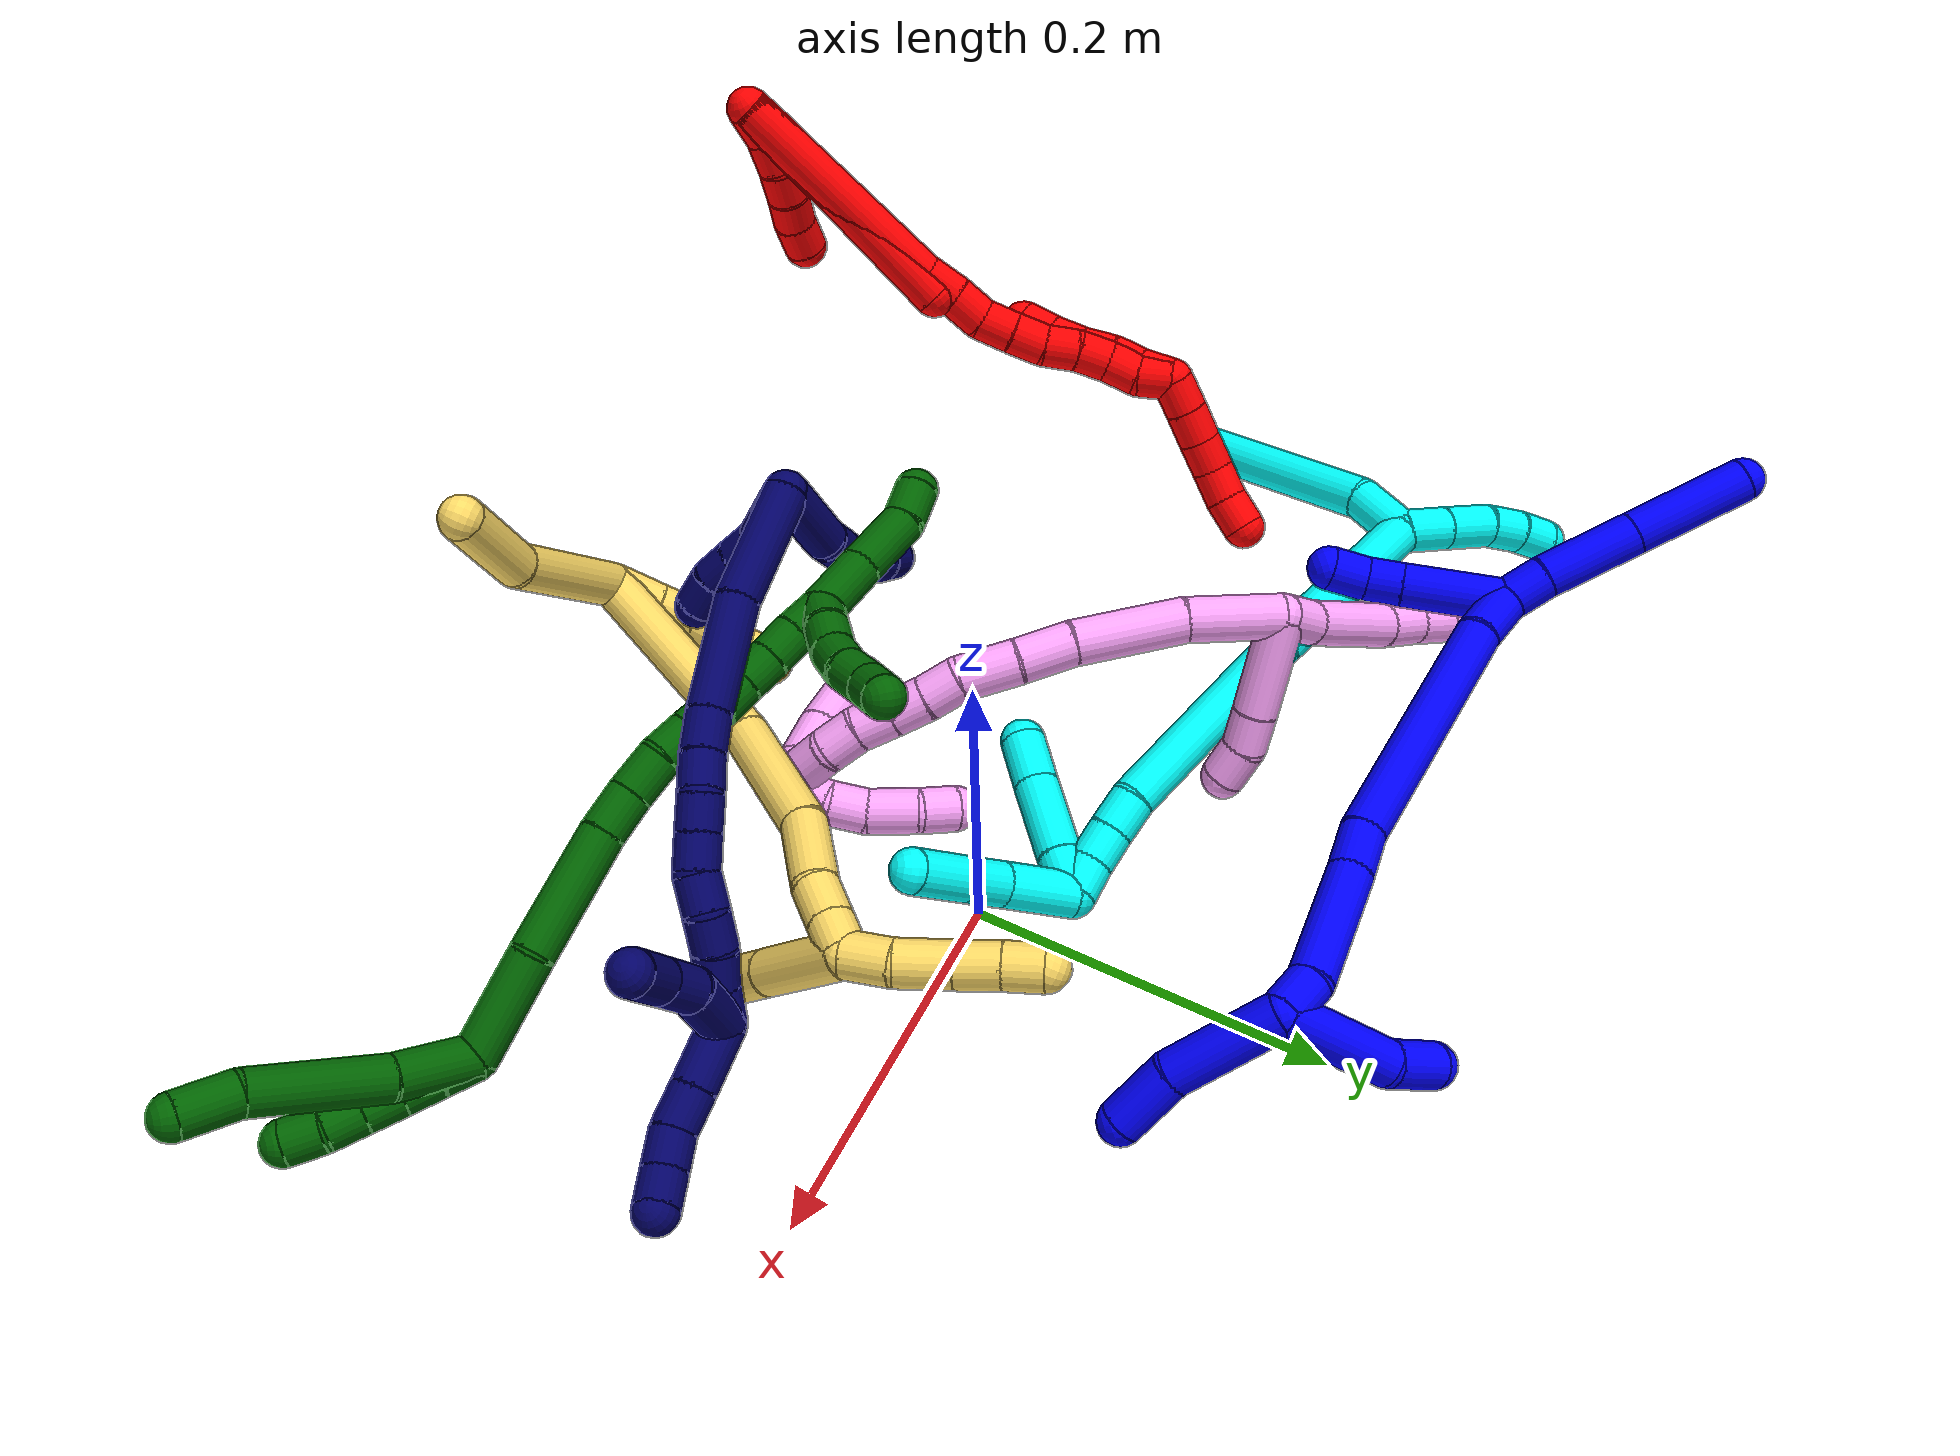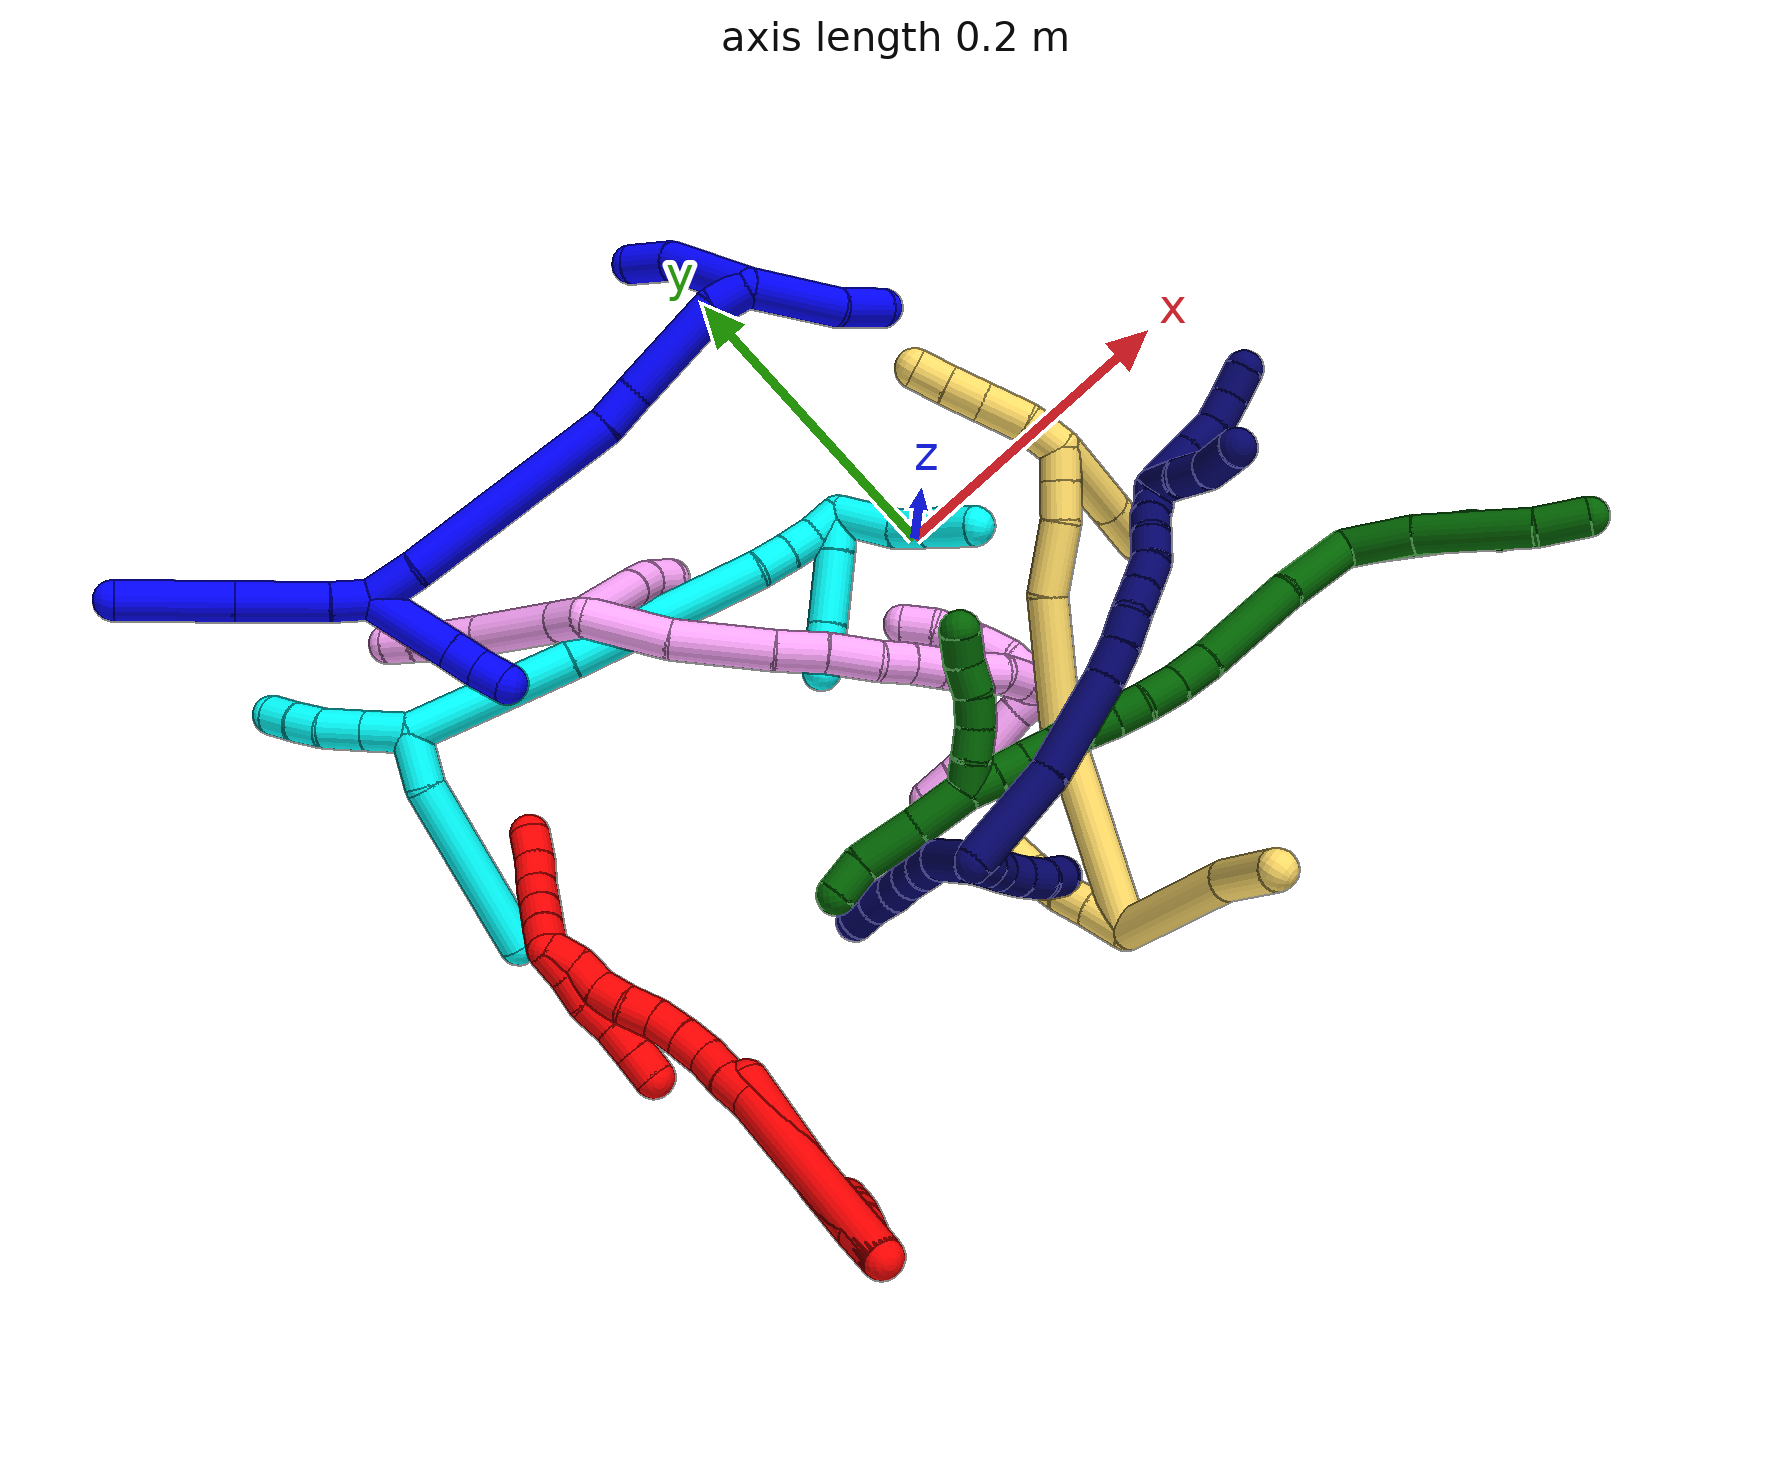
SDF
<sdf version="1.7">
 <world name="default">
  <plugin name="TubeGeneratorPlugin" filename="libtube_generator_plugin.so"/>
  <model name="photoneo_s_sensor">
   <static>1</static>
   <pose>0 0 2 1.57079 1.57079 3.14159</pose>
   <link name="link">
    <inertial><mass>0.1</mass></inertial>
    <sensor name="sensor" type="depth">
     <update_rate>30</update_rate>
     <camera>
      <horizontal_fov>1.22</horizontal_fov>
      <image><width>1920</width><height>1200</height><format>B8G8R8</format></image>
      <clip><near>0.1</near><far>4</far></clip>
      <depth_camera><output>points</output></depth_camera>
     </camera>
     <plugin name="camera_plugin" filename="libgazebo_ros_depth_camera.so">
      <baseline>0.2</baseline>
      <alwaysOn>1</alwaysOn>
      <updateRate>0.0</updateRate>
      <cameraName>camera_ir</cameraName>
      <imageTopicName>/camera/color/image_raw</imageTopicName>
      <cameraInfoTopicName>/camera/color/camera_info</cameraInfoTopicName>
      <depthImageTopicName>/camera/depth/image_raw</depthImageTopicName>
      <depthImageCameraInfoTopicName>/camera/depth/camera_info</depthImageCameraInfoTopicName>
      <pointCloudTopicName>/camera/depth/points</pointCloudTopicName>
      <frameName>fr_optical</frameName>
      <pointCloudCutoff>0.1</pointCloudCutoff>
      <pointCloudCutoffMax>2.0</pointCloudCutoffMax>
      <distortionK1>0</distortionK1>
      <distortionK2>0</distortionK2>
      <distortionK3>0</distortionK3>
      <distortionT1>0</distortionT1>
      <distortionT2>0</distortionT2>
      <CxPrime>0</CxPrime>
      <Cx>0</Cx>
      <Cy>0</Cy>
      <focalLength>0</focalLength>
      <hackBaseline>0</hackBaseline>
     </plugin>
    </sensor>
   </link>
  </model>
  <gravity>0 0 -9.8</gravity>
  <magnetic_field>6e-06 2.3e-05 -4.2e-05</magnetic_field>
  <atmosphere type="adiabatic"/>
  <physics name="default_physics" default="0" type="ode">
   <max_step_size>0.003</max_step_size>
   <real_time_factor>1</real_time_factor>
   <real_time_update_rate>1000</real_time_update_rate>
   <max_contacts>10000</max_contacts>
   <ode>
    <solver>
     <type>quick</type>
     <iters>100</iters>
     <sor>1.3</sor>
     <use_dynamic_moi_rescaling>0</use_dynamic_moi_rescaling>
    </solver>
    <constraints>
     <contact_max_correcting_vel>0</contact_max_correcting_vel>
     <contact_surface_layer>0.001</contact_surface_layer>
     <cfm>0</cfm>
     <erp>0.2</erp>
    </constraints>
   </ode>
  </physics>
  <scene><ambient>0.4 0.4 0.4 1</ambient><background>0.7 0.7 0.7 1</background><shadows>0</shadows></scene>
  <audio><device>default</device></audio>
  <spherical_coordinates>
   <surface_model>EARTH_WGS84</surface_model>
   <latitude_deg>0</latitude_deg>
   <longitude_deg>0</longitude_deg>
   <elevation>0</elevation>
   <heading_deg>0</heading_deg>
  </spherical_coordinates>
  <model name="bin">
   <static>1</static>
   <link name="bottom">
    <collision name="collision-bottom">
     <pose>0 0 -0.01 0 -0 0</pose>
     <geometry><box><size>0.8 0.6 0.02</size></box></geometry>
     <surface>
      <friction><ode><mu>100</mu><mu2>100</mu2></ode></friction>
      <contact><collide_bitmask>65535</collide_bitmask></contact>
     </surface>
    </collision>
   </link>
   <link name="west_wall">
    <collision name="collision-west_wall">
     <pose>-0.41 0 0.1 0 -0 0</pose>
     <geometry><box><size>0.02 0.6 0.2</size></box></geometry>
     <surface>
      <friction><ode><mu>100</mu><mu2>100</mu2></ode></friction>
      <contact><collide_bitmask>65535</collide_bitmask></contact>
     </surface>
    </collision>
   </link>
   <link name="east_wall">
    <collision name="collision-east_wall">
     <pose>0.41 0 0.1 0 -0 0</pose>
     <geometry><box><size>0.02 0.6 0.2</size></box></geometry>
     <surface>
      <friction><ode><mu>100</mu><mu2>100</mu2></ode></friction>
      <contact><collide_bitmask>65535</collide_bitmask></contact>
     </surface>
    </collision>
   </link>
   <link name="south_wall">
    <collision name="collision-south_wall">
     <pose>0 -0.31 0.1 0 -0 0</pose>
     <geometry><box><size>0.8 0.02 0.2</size></box></geometry>
     <surface>
      <friction><ode><mu>100</mu><mu2>100</mu2></ode></friction>
      <contact><collide_bitmask>65535</collide_bitmask></contact>
     </surface>
    </collision>
   </link>
   <link name="north_wall">
    <collision name="collision-north_wall">
     <pose>0 0.31 0.1 0 -0 0</pose>
     <geometry><box><size>0.8 0.02 0.2</size></box></geometry>
     <surface>
      <friction><ode><mu>100</mu><mu2>100</mu2></ode></friction>
      <contact><collide_bitmask>65535</collide_bitmask></contact>
     </surface>
    </collision>
   </link>
  </model>
  <model name="1">
   <static>0</static>
   <link name="1">
    <collision name="collision-cylinder-e_1_2_8">
     <pose>-0.003101 -0.00076 0.012139 0.06253 -0.249607 -0.007847</pose>
     <geometry><cylinder><radius>0.0125</radius><length>0.025104</length></cylinder></geometry>
     <surface>
      <friction><ode><mu>1.16</mu><mu2>1.16</mu2><slip1>0</slip1><slip2>0</slip2></ode></friction>
      <contact><ode><kp>1e+06</kp><kd>1</kd><max_vel>0</max_vel><min_depth>0.001</min_depth></ode></contact>
     </surface>
    </collision>
    <visual name="visual-cylinder-e_1_2_8">
     <pose>-0.003101 -0.00076 0.012139 0.06253 -0.249607 -0.007847</pose>
     <geometry><cylinder><radius>0.0125</radius><length>0.025104</length></cylinder></geometry>
     <material><ambient>0 0 1 1</ambient></material>
    </visual>
    <collision name="collision-cylinder-e_2_8_9">
     <pose>-0.011463 -0.001042 0.051624 -0.017496 -0.190067 0.001668</pose>
     <geometry><cylinder><radius>0.0125</radius><length>0.055702</length></cylinder></geometry>
     <surface>
      <friction><ode><mu>1.16</mu><mu2>1.16</mu2><slip1>0</slip1><slip2>0</slip2></ode></friction>
      <contact><ode><kp>1e+06</kp><kd>1</kd><max_vel>0</max_vel><min_depth>0.001</min_depth></ode></contact>
     </surface>
    </collision>
    <visual name="visual-cylinder-e_2_8_9">
     <pose>-0.011463 -0.001042 0.051624 -0.017496 -0.190067 0.001668</pose>
     <geometry><cylinder><radius>0.0125</radius><length>0.055702</length></cylinder></geometry>
     <material><ambient>0 0 1 1</ambient></material>
    </visual>
    <collision name="collision-cylinder-e_3_9_6">
     <pose>-0.023148 -0.000128 0.112962 -0.012815 -0.186739 0.0012</pose>
     <geometry><cylinder><radius>0.0125</radius><length>0.069194</length></cylinder></geometry>
     <surface>
      <friction><ode><mu>1.16</mu><mu2>1.16</mu2><slip1>0</slip1><slip2>0</slip2></ode></friction>
      <contact><ode><kp>1e+06</kp><kd>1</kd><max_vel>0</max_vel><min_depth>0.001</min_depth></ode></contact>
     </surface>
    </collision>
    <visual name="visual-cylinder-e_3_9_6">
     <pose>-0.023148 -0.000128 0.112962 -0.012815 -0.186739 0.0012</pose>
     <geometry><cylinder><radius>0.0125</radius><length>0.069194</length></cylinder></geometry>
     <material><ambient>0 0 1 1</ambient></material>
    </visual>
    <collision name="collision-cylinder-e_1_2_10">
     <pose>-0.009799 -0.009383 -0.025579 2.78999 -0.345245 -1.55218</pose>
     <geometry><cylinder><radius>0.0125</radius><length>0.057908</length></cylinder></geometry>
     <surface>
      <friction><ode><mu>1.16</mu><mu2>1.16</mu2><slip1>0</slip1><slip2>0</slip2></ode></friction>
      <contact><ode><kp>1e+06</kp><kd>1</kd><max_vel>0</max_vel><min_depth>0.001</min_depth></ode></contact>
     </surface>
    </collision>
    <visual name="visual-cylinder-e_1_2_10">
     <pose>-0.009799 -0.009383 -0.025579 2.78999 -0.345245 -1.55218</pose>
     <geometry><cylinder><radius>0.0125</radius><length>0.057908</length></cylinder></geometry>
     <material><ambient>0 0 1 1</ambient></material>
    </visual>
    <collision name="collision-cylinder-e_2_10_11">
     <pose>-0.023233 -0.02214 -0.060171 2.78349 -0.361186 -1.57957</pose>
     <geometry><cylinder><radius>0.0125</radius><length>0.020577</length></cylinder></geometry>
     <surface>
      <friction><ode><mu>1.16</mu><mu2>1.16</mu2><slip1>0</slip1><slip2>0</slip2></ode></friction>
      <contact><ode><kp>1e+06</kp><kd>1</kd><max_vel>0</max_vel><min_depth>0.001</min_depth></ode></contact>
     </surface>
    </collision>
    <visual name="visual-cylinder-e_2_10_11">
     <pose>-0.023233 -0.02214 -0.060171 2.78349 -0.361186 -1.57957</pose>
     <geometry><cylinder><radius>0.0125</radius><length>0.020577</length></cylinder></geometry>
     <material><ambient>0 0 1 1</ambient></material>
    </visual>
    <collision name="collision-cylinder-e_3_11_5">
     <pose>-0.029346 -0.031558 -0.077732 2.52601 -0.232313 -0.703559</pose>
     <geometry><cylinder><radius>0.0125</radius><length>0.021515</length></cylinder></geometry>
     <surface>
      <friction><ode><mu>1.16</mu><mu2>1.16</mu2><slip1>0</slip1><slip2>0</slip2></ode></friction>
      <contact><ode><kp>1e+06</kp><kd>1</kd><max_vel>0</max_vel><min_depth>0.001</min_depth></ode></contact>
     </surface>
    </collision>
    <visual name="visual-cylinder-e_3_11_5">
     <pose>-0.029346 -0.031558 -0.077732 2.52601 -0.232313 -0.703559</pose>
     <geometry><cylinder><radius>0.0125</radius><length>0.021515</length></cylinder></geometry>
     <material><ambient>0 0 1 1</ambient></material>
    </visual>
    <collision name="collision-cylinder-e_1_2_12">
     <pose>0.011809 -0.003394 -0.011176 2.84679 0.790903 2.45813</pose>
     <geometry><cylinder><radius>0.0125</radius><length>0.033219</length></cylinder></geometry>
     <surface>
      <friction><ode><mu>1.16</mu><mu2>1.16</mu2><slip1>0</slip1><slip2>0</slip2></ode></friction>
      <contact><ode><kp>1e+06</kp><kd>1</kd><max_vel>0</max_vel><min_depth>0.001</min_depth></ode></contact>
     </surface>
    </collision>
    <visual name="visual-cylinder-e_1_2_12">
     <pose>0.011809 -0.003394 -0.011176 2.84679 0.790903 2.45813</pose>
     <geometry><cylinder><radius>0.0125</radius><length>0.033219</length></cylinder></geometry>
     <material><ambient>0 0 1 1</ambient></material>
    </visual>
    <collision name="collision-cylinder-e_2_12_13">
     <pose>0.078215 -0.009401 -0.069756 3.08652 0.855044 3.02083</pose>
     <geometry><cylinder><radius>0.0125</radius><length>0.144705</length></cylinder></geometry>
     <surface>
      <friction><ode><mu>1.16</mu><mu2>1.16</mu2><slip1>0</slip1><slip2>0</slip2></ode></friction>
      <contact><ode><kp>1e+06</kp><kd>1</kd><max_vel>0</max_vel><min_depth>0.001</min_depth></ode></contact>
     </surface>
    </collision>
    <visual name="visual-cylinder-e_2_12_13">
     <pose>0.078215 -0.009401 -0.069756 3.08652 0.855044 3.02083</pose>
     <geometry><cylinder><radius>0.0125</radius><length>0.144705</length></cylinder></geometry>
     <material><ambient>0 0 1 1</ambient></material>
    </visual>
    <collision name="collision-cylinder-e_3_13_14">
     <pose>0.144475 -0.012041 -0.123844 3.13762 1.05043 3.13474</pose>
     <geometry><cylinder><radius>0.0125</radius><length>0.026883</length></cylinder></geometry>
     <surface>
      <friction><ode><mu>1.16</mu><mu2>1.16</mu2><slip1>0</slip1><slip2>0</slip2></ode></friction>
      <contact><ode><kp>1e+06</kp><kd>1</kd><max_vel>0</max_vel><min_depth>0.001</min_depth></ode></contact>
     </surface>
    </collision>
    <visual name="visual-cylinder-e_3_13_14">
     <pose>0.144475 -0.012041 -0.123844 3.13762 1.05043 3.13474</pose>
     <geometry><cylinder><radius>0.0125</radius><length>0.026883</length></cylinder></geometry>
     <material><ambient>0 0 1 1</ambient></material>
    </visual>
    <collision name="collision-cylinder-e_4_14_15">
     <pose>0.186707 -0.015673 -0.148285 2.94124 1.03572 2.79233</pose>
     <geometry><cylinder><radius>0.0125</radius><length>0.071072</length></cylinder></geometry>
     <surface>
      <friction><ode><mu>1.16</mu><mu2>1.16</mu2><slip1>0</slip1><slip2>0</slip2></ode></friction>
      <contact><ode><kp>1e+06</kp><kd>1</kd><max_vel>0</max_vel><min_depth>0.001</min_depth></ode></contact>
     </surface>
    </collision>
    <visual name="visual-cylinder-e_4_14_15">
     <pose>0.186707 -0.015673 -0.148285 2.94124 1.03572 2.79233</pose>
     <geometry><cylinder><radius>0.0125</radius><length>0.071072</length></cylinder></geometry>
     <material><ambient>0 0 1 1</ambient></material>
    </visual>
    <collision name="collision-cylinder-e_5_15_1">
     <pose>0.225257 -0.021465 -0.174817 2.89748 0.723133 2.51431</pose>
     <geometry><cylinder><radius>0.0125</radius><length>0.024121</length></cylinder></geometry>
     <surface>
      <friction><ode><mu>1.16</mu><mu2>1.16</mu2><slip1>0</slip1><slip2>0</slip2></ode></friction>
      <contact><ode><kp>1e+06</kp><kd>1</kd><max_vel>0</max_vel><min_depth>0.001</min_depth></ode></contact>
     </surface>
    </collision>
    <visual name="visual-cylinder-e_5_15_1">
     <pose>0.225257 -0.021465 -0.174817 2.89748 0.723133 2.51431</pose>
     <geometry><cylinder><radius>0.0125</radius><length>0.024121</length></cylinder></geometry>
     <material><ambient>0 0 1 1</ambient></material>
    </visual>
    <collision name="collision-cylinder-e_1_1_16">
     <pose>0.234258 -0.015686 -0.214457 -2.88907 0.032001 -0.250803</pose>
     <geometry><cylinder><radius>0.0125</radius><length>0.063787</length></cylinder></geometry>
     <surface>
      <friction><ode><mu>1.16</mu><mu2>1.16</mu2><slip1>0</slip1><slip2>0</slip2></ode></friction>
      <contact><ode><kp>1e+06</kp><kd>1</kd><max_vel>0</max_vel><min_depth>0.001</min_depth></ode></contact>
     </surface>
    </collision>
    <visual name="visual-cylinder-e_1_1_16">
     <pose>0.234258 -0.015686 -0.214457 -2.88907 0.032001 -0.250803</pose>
     <geometry><cylinder><radius>0.0125</radius><length>0.063787</length></cylinder></geometry>
     <material><ambient>0 0 1 1</ambient></material>
    </visual>
    <collision name="collision-cylinder-e_2_16_4">
     <pose>0.238936 -8.6e-05 -0.261328 -2.69645 0.203381 -0.84716</pose>
     <geometry><cylinder><radius>0.0125</radius><length>0.036213</length></cylinder></geometry>
     <surface>
      <friction><ode><mu>1.16</mu><mu2>1.16</mu2><slip1>0</slip1><slip2>0</slip2></ode></friction>
      <contact><ode><kp>1e+06</kp><kd>1</kd><max_vel>0</max_vel><min_depth>0.001</min_depth></ode></contact>
     </surface>
    </collision>
    <visual name="visual-cylinder-e_2_16_4">
     <pose>0.238936 -8.6e-05 -0.261328 -2.69645 0.203381 -0.84716</pose>
     <geometry><cylinder><radius>0.0125</radius><length>0.036213</length></cylinder></geometry>
     <material><ambient>0 0 1 1</ambient></material>
    </visual>
    <collision name="collision-cylinder-e_1_1_17">
     <pose>0.238022 0.003437 -0.163505 -0.932752 0.140938 -0.071038</pose>
     <geometry><cylinder><radius>0.0125</radius><length>0.068119</length></cylinder></geometry>
     <surface>
      <friction><ode><mu>1.16</mu><mu2>1.16</mu2><slip1>0</slip1><slip2>0</slip2></ode></friction>
      <contact><ode><kp>1e+06</kp><kd>1</kd><max_vel>0</max_vel><min_depth>0.001</min_depth></ode></contact>
     </surface>
    </collision>
    <visual name="visual-cylinder-e_1_1_17">
     <pose>0.238022 0.003437 -0.163505 -0.932752 0.140938 -0.071038</pose>
     <geometry><cylinder><radius>0.0125</radius><length>0.068119</length></cylinder></geometry>
     <material><ambient>0 0 1 1</ambient></material>
    </visual>
    <collision name="collision-cylinder-e_2_17_3">
     <pose>0.239753 0.042132 -0.132929 -0.835881 -0.192721 0.085801</pose>
     <geometry><cylinder><radius>0.0125</radius><length>0.031881</length></cylinder></geometry>
     <surface>
      <friction><ode><mu>1.16</mu><mu2>1.16</mu2><slip1>0</slip1><slip2>0</slip2></ode></friction>
      <contact><ode><kp>1e+06</kp><kd>1</kd><max_vel>0</max_vel><min_depth>0.001</min_depth></ode></contact>
     </surface>
    </collision>
    <visual name="visual-cylinder-e_2_17_3">
     <pose>0.239753 0.042132 -0.132929 -0.835881 -0.192721 0.085801</pose>
     <geometry><cylinder><radius>0.0125</radius><length>0.031881</length></cylinder></geometry>
     <material><ambient>0 0 1 1</ambient></material>
    </visual>
    <collision name="collision-sphere-3">
     <pose>0.2367 0.053739 -0.122438 0 -0 0</pose>
     <geometry><sphere><radius>0.0125</radius></sphere></geometry>
     <surface>
      <friction><ode><mu>1.16</mu><mu2>1.16</mu2><slip1>0</slip1><slip2>0</slip2></ode></friction>
      <contact><ode><kp>1e+06</kp><kd>1</kd><max_vel>0</max_vel><min_depth>0.001</min_depth></ode></contact>
     </surface>
    </collision>
    <visual name="visual-sphere-3">
     <pose>0.2367 0.053739 -0.122438 0 -0 0</pose>
     <geometry><sphere><radius>0.0125</radius></sphere></geometry>
     <material><ambient>0 0 1 1</ambient></material>
    </visual>
    <collision name="collision-sphere-17">
     <pose>0.242806 0.030524 -0.143419 0 -0 0</pose>
     <geometry><sphere><radius>0.0125</radius></sphere></geometry>
     <surface>
      <friction><ode><mu>1.16</mu><mu2>1.16</mu2><slip1>0</slip1><slip2>0</slip2></ode></friction>
      <contact><ode><kp>1e+06</kp><kd>1</kd><max_vel>0</max_vel><min_depth>0.001</min_depth></ode></contact>
     </surface>
    </collision>
    <visual name="visual-sphere-17">
     <pose>0.242806 0.030524 -0.143419 0 -0 0</pose>
     <geometry><sphere><radius>0.0125</radius></sphere></geometry>
     <material><ambient>0 0 1 1</ambient></material>
    </visual>
    <collision name="collision-sphere-4">
     <pose>0.242593 0.00755 -0.277333 0 -0 0</pose>
     <geometry><sphere><radius>0.0125</radius></sphere></geometry>
     <surface>
      <friction><ode><mu>1.16</mu><mu2>1.16</mu2><slip1>0</slip1><slip2>0</slip2></ode></friction>
      <contact><ode><kp>1e+06</kp><kd>1</kd><max_vel>0</max_vel><min_depth>0.001</min_depth></ode></contact>
     </surface>
    </collision>
    <visual name="visual-sphere-4">
     <pose>0.242593 0.00755 -0.277333 0 -0 0</pose>
     <geometry><sphere><radius>0.0125</radius></sphere></geometry>
     <material><ambient>0 0 1 1</ambient></material>
    </visual>
    <collision name="collision-sphere-16">
     <pose>0.235278 -0.007722 -0.245323 0 -0 0</pose>
     <geometry><sphere><radius>0.0125</radius></sphere></geometry>
     <surface>
      <friction><ode><mu>1.16</mu><mu2>1.16</mu2><slip1>0</slip1><slip2>0</slip2></ode></friction>
      <contact><ode><kp>1e+06</kp><kd>1</kd><max_vel>0</max_vel><min_depth>0.001</min_depth></ode></contact>
     </surface>
    </collision>
    <visual name="visual-sphere-16">
     <pose>0.235278 -0.007722 -0.245323 0 -0 0</pose>
     <geometry><sphere><radius>0.0125</radius></sphere></geometry>
     <material><ambient>0 0 1 1</ambient></material>
    </visual>
    <collision name="collision-sphere-1">
     <pose>0.233237 -0.023651 -0.183591 0 -0 0</pose>
     <geometry><sphere><radius>0.0125</radius></sphere></geometry>
     <surface>
      <friction><ode><mu>1.16</mu><mu2>1.16</mu2><slip1>0</slip1><slip2>0</slip2></ode></friction>
      <contact><ode><kp>1e+06</kp><kd>1</kd><max_vel>0</max_vel><min_depth>0.001</min_depth></ode></contact>
     </surface>
    </collision>
    <visual name="visual-sphere-1">
     <pose>0.233237 -0.023651 -0.183591 0 -0 0</pose>
     <geometry><sphere><radius>0.0125</radius></sphere></geometry>
     <material><ambient>0 0 1 1</ambient></material>
    </visual>
    <collision name="collision-sphere-15">
     <pose>0.217276 -0.01928 -0.166043 0 -0 0</pose>
     <geometry><sphere><radius>0.0125</radius></sphere></geometry>
     <surface>
      <friction><ode><mu>1.16</mu><mu2>1.16</mu2><slip1>0</slip1><slip2>0</slip2></ode></friction>
      <contact><ode><kp>1e+06</kp><kd>1</kd><max_vel>0</max_vel><min_depth>0.001</min_depth></ode></contact>
     </surface>
    </collision>
    <visual name="visual-sphere-15">
     <pose>0.217276 -0.01928 -0.166043 0 -0 0</pose>
     <geometry><sphere><radius>0.0125</radius></sphere></geometry>
     <material><ambient>0 0 1 1</ambient></material>
    </visual>
    <collision name="collision-sphere-14">
     <pose>0.156137 -0.012067 -0.130527 0 -0 0</pose>
     <geometry><sphere><radius>0.0125</radius></sphere></geometry>
     <surface>
      <friction><ode><mu>1.16</mu><mu2>1.16</mu2><slip1>0</slip1><slip2>0</slip2></ode></friction>
      <contact><ode><kp>1e+06</kp><kd>1</kd><max_vel>0</max_vel><min_depth>0.001</min_depth></ode></contact>
     </surface>
    </collision>
    <visual name="visual-sphere-14">
     <pose>0.156137 -0.012067 -0.130527 0 -0 0</pose>
     <geometry><sphere><radius>0.0125</radius></sphere></geometry>
     <material><ambient>0 0 1 1</ambient></material>
    </visual>
    <collision name="collision-sphere-13">
     <pose>0.132812 -0.012014 -0.117161 0 -0 0</pose>
     <geometry><sphere><radius>0.0125</radius></sphere></geometry>
     <surface>
      <friction><ode><mu>1.16</mu><mu2>1.16</mu2><slip1>0</slip1><slip2>0</slip2></ode></friction>
      <contact><ode><kp>1e+06</kp><kd>1</kd><max_vel>0</max_vel><min_depth>0.001</min_depth></ode></contact>
     </surface>
    </collision>
    <visual name="visual-sphere-13">
     <pose>0.132812 -0.012014 -0.117161 0 -0 0</pose>
     <geometry><sphere><radius>0.0125</radius></sphere></geometry>
     <material><ambient>0 0 1 1</ambient></material>
    </visual>
    <collision name="collision-sphere-12">
     <pose>0.023618 -0.006787 -0.022352 0 -0 0</pose>
     <geometry><sphere><radius>0.0125</radius></sphere></geometry>
     <surface>
      <friction><ode><mu>1.16</mu><mu2>1.16</mu2><slip1>0</slip1><slip2>0</slip2></ode></friction>
      <contact><ode><kp>1e+06</kp><kd>1</kd><max_vel>0</max_vel><min_depth>0.001</min_depth></ode></contact>
     </surface>
    </collision>
    <visual name="visual-sphere-12">
     <pose>0.023618 -0.006787 -0.022352 0 -0 0</pose>
     <geometry><sphere><radius>0.0125</radius></sphere></geometry>
     <material><ambient>0 0 1 1</ambient></material>
    </visual>
    <collision name="collision-sphere-5">
     <pose>-0.031823 -0.037603 -0.086279 0 -0 0</pose>
     <geometry><sphere><radius>0.0125</radius></sphere></geometry>
     <surface>
      <friction><ode><mu>1.16</mu><mu2>1.16</mu2><slip1>0</slip1><slip2>0</slip2></ode></friction>
      <contact><ode><kp>1e+06</kp><kd>1</kd><max_vel>0</max_vel><min_depth>0.001</min_depth></ode></contact>
     </surface>
    </collision>
    <visual name="visual-sphere-5">
     <pose>-0.031823 -0.037603 -0.086279 0 -0 0</pose>
     <geometry><sphere><radius>0.0125</radius></sphere></geometry>
     <material><ambient>0 0 1 1</ambient></material>
    </visual>
    <collision name="collision-sphere-8">
     <pose>-0.006201 -0.00152 0.024279 0 -0 0</pose>
     <geometry><sphere><radius>0.0125</radius></sphere></geometry>
     <surface>
      <friction><ode><mu>1.16</mu><mu2>1.16</mu2><slip1>0</slip1><slip2>0</slip2></ode></friction>
      <contact><ode><kp>1e+06</kp><kd>1</kd><max_vel>0</max_vel><min_depth>0.001</min_depth></ode></contact>
     </surface>
    </collision>
    <visual name="visual-sphere-8">
     <pose>-0.006201 -0.00152 0.024279 0 -0 0</pose>
     <geometry><sphere><radius>0.0125</radius></sphere></geometry>
     <material><ambient>0 0 1 1</ambient></material>
    </visual>
    <collision name="collision-sphere-2">
     <geometry><sphere><radius>0.0125</radius></sphere></geometry>
     <surface>
      <friction><ode><mu>1.16</mu><mu2>1.16</mu2><slip1>0</slip1><slip2>0</slip2></ode></friction>
      <contact><ode><kp>1e+06</kp><kd>1</kd><max_vel>0</max_vel><min_depth>0.001</min_depth></ode></contact>
     </surface>
    </collision>
    <visual name="visual-sphere-2">
     <geometry><sphere><radius>0.0125</radius></sphere></geometry>
     <material><ambient>0 0 1 1</ambient></material>
    </visual>
    <collision name="collision-sphere-9">
     <pose>-0.016725 -0.000563 0.078969 0 -0 0</pose>
     <geometry><sphere><radius>0.0125</radius></sphere></geometry>
     <surface>
      <friction><ode><mu>1.16</mu><mu2>1.16</mu2><slip1>0</slip1><slip2>0</slip2></ode></friction>
      <contact><ode><kp>1e+06</kp><kd>1</kd><max_vel>0</max_vel><min_depth>0.001</min_depth></ode></contact>
     </surface>
    </collision>
    <visual name="visual-sphere-9">
     <pose>-0.016725 -0.000563 0.078969 0 -0 0</pose>
     <geometry><sphere><radius>0.0125</radius></sphere></geometry>
     <material><ambient>0 0 1 1</ambient></material>
    </visual>
    <collision name="collision-sphere-6">
     <pose>-0.029571 0.000308 0.146954 0 -0 0</pose>
     <geometry><sphere><radius>0.0125</radius></sphere></geometry>
     <surface>
      <friction><ode><mu>1.16</mu><mu2>1.16</mu2><slip1>0</slip1><slip2>0</slip2></ode></friction>
      <contact><ode><kp>1e+06</kp><kd>1</kd><max_vel>0</max_vel><min_depth>0.001</min_depth></ode></contact>
     </surface>
    </collision>
    <visual name="visual-sphere-6">
     <pose>-0.029571 0.000308 0.146954 0 -0 0</pose>
     <geometry><sphere><radius>0.0125</radius></sphere></geometry>
     <material><ambient>0 0 1 1</ambient></material>
    </visual>
    <collision name="collision-sphere-10">
     <pose>-0.019598 -0.018767 -0.051157 0 -0 0</pose>
     <geometry><sphere><radius>0.0125</radius></sphere></geometry>
     <surface>
      <friction><ode><mu>1.16</mu><mu2>1.16</mu2><slip1>0</slip1><slip2>0</slip2></ode></friction>
      <contact><ode><kp>1e+06</kp><kd>1</kd><max_vel>0</max_vel><min_depth>0.001</min_depth></ode></contact>
     </surface>
    </collision>
    <visual name="visual-sphere-10">
     <pose>-0.019598 -0.018767 -0.051157 0 -0 0</pose>
     <geometry><sphere><radius>0.0125</radius></sphere></geometry>
     <material><ambient>0 0 1 1</ambient></material>
    </visual>
    <collision name="collision-sphere-11">
     <pose>-0.026869 -0.025513 -0.069185 0 -0 0</pose>
     <geometry><sphere><radius>0.0125</radius></sphere></geometry>
     <surface>
      <friction><ode><mu>1.16</mu><mu2>1.16</mu2><slip1>0</slip1><slip2>0</slip2></ode></friction>
      <contact><ode><kp>1e+06</kp><kd>1</kd><max_vel>0</max_vel><min_depth>0.001</min_depth></ode></contact>
     </surface>
    </collision>
    <visual name="visual-sphere-11">
     <pose>-0.026869 -0.025513 -0.069185 0 -0 0</pose>
     <geometry><sphere><radius>0.0125</radius></sphere></geometry>
     <material><ambient>0 0 1 1</ambient></material>
    </visual>
    <inertial>
     <pose>0.103673 -0.006158 -0.080619 0 -0 0</pose>
     <mass>0.75</mass>
     <inertia>
      <ixx>-6.8e-05</ixx>
      <ixy>0</ixy>
      <ixz>0</ixz>
      <iyy>0.000344</iyy>
      <iyz>0</iyz>
      <izz>-0.000244</izz>
     </inertia>
    </inertial>
   </link>
   <pose>-0.277218 0.187214 0.063351 -1.28737 -0.141916 0.627883</pose>
  </model>
  <model name="2">
   <static>0</static>
   <link name="2">
    <collision name="collision-cylinder-e_1_2_8">
     <pose>-0.003775 0.004017 -0.010577 -2.77862 -0.322037 1.44906</pose>
     <geometry><cylinder><radius>0.0125</radius><length>0.023854</length></cylinder></geometry>
     <surface>
      <friction><ode><mu>1.16</mu><mu2>1.16</mu2><slip1>0</slip1><slip2>0</slip2></ode></friction>
      <contact><ode><kp>1e+06</kp><kd>1</kd><max_vel>0</max_vel><min_depth>0.001</min_depth></ode></contact>
     </surface>
    </collision>
    <visual name="visual-cylinder-e_1_2_8">
     <pose>-0.003775 0.004017 -0.010577 -2.77862 -0.322037 1.44906</pose>
     <geometry><cylinder><radius>0.0125</radius><length>0.023854</length></cylinder></geometry>
     <material><ambient>1 0 0 1</ambient></material>
    </visual>
    <collision name="collision-cylinder-e_2_8_9">
     <pose>-0.013259 0.015264 -0.039621 -2.76843 -0.280307 1.28357</pose>
     <geometry><cylinder><radius>0.0125</radius><length>0.041275</length></cylinder></geometry>
     <surface>
      <friction><ode><mu>1.16</mu><mu2>1.16</mu2><slip1>0</slip1><slip2>0</slip2></ode></friction>
      <contact><ode><kp>1e+06</kp><kd>1</kd><max_vel>0</max_vel><min_depth>0.001</min_depth></ode></contact>
     </surface>
    </collision>
    <visual name="visual-cylinder-e_2_8_9">
     <pose>-0.013259 0.015264 -0.039621 -2.76843 -0.280307 1.28357</pose>
     <geometry><cylinder><radius>0.0125</radius><length>0.041275</length></cylinder></geometry>
     <material><ambient>1 0 0 1</ambient></material>
    </visual>
    <collision name="collision-cylinder-e_3_9_6">
     <pose>-0.030662 0.040716 -0.094584 -2.67852 -0.279166 1.07484</pose>
     <geometry><cylinder><radius>0.0125</radius><length>0.084871</length></cylinder></geometry>
     <surface>
      <friction><ode><mu>1.16</mu><mu2>1.16</mu2><slip1>0</slip1><slip2>0</slip2></ode></friction>
      <contact><ode><kp>1e+06</kp><kd>1</kd><max_vel>0</max_vel><min_depth>0.001</min_depth></ode></contact>
     </surface>
    </collision>
    <visual name="visual-cylinder-e_3_9_6">
     <pose>-0.030662 0.040716 -0.094584 -2.67852 -0.279166 1.07484</pose>
     <geometry><cylinder><radius>0.0125</radius><length>0.084871</length></cylinder></geometry>
     <material><ambient>1 0 0 1</ambient></material>
    </visual>
    <collision name="collision-cylinder-e_1_2_10">
     <pose>-0.000248 0.001408 -0.009897 -3.0003 -0.024827 0.347336</pose>
     <geometry><cylinder><radius>0.0125</radius><length>0.02</length></cylinder></geometry>
     <surface>
      <friction><ode><mu>1.16</mu><mu2>1.16</mu2><slip1>0</slip1><slip2>0</slip2></ode></friction>
      <contact><ode><kp>1e+06</kp><kd>1</kd><max_vel>0</max_vel><min_depth>0.001</min_depth></ode></contact>
     </surface>
    </collision>
    <visual name="visual-cylinder-e_1_2_10">
     <pose>-0.000248 0.001408 -0.009897 -3.0003 -0.024827 0.347336</pose>
     <geometry><cylinder><radius>0.0125</radius><length>0.02</length></cylinder></geometry>
     <material><ambient>1 0 0 1</ambient></material>
    </visual>
    <collision name="collision-cylinder-e_2_10_11">
     <pose>0.001083 0.004483 -0.029527 -2.97192 0.1586 -1.50306</pose>
     <geometry><cylinder><radius>0.0125</radius><length>0.02</length></cylinder></geometry>
     <surface>
      <friction><ode><mu>1.16</mu><mu2>1.16</mu2><slip1>0</slip1><slip2>0</slip2></ode></friction>
      <contact><ode><kp>1e+06</kp><kd>1</kd><max_vel>0</max_vel><min_depth>0.001</min_depth></ode></contact>
     </surface>
    </collision>
    <visual name="visual-cylinder-e_2_10_11">
     <pose>0.001083 0.004483 -0.029527 -2.97192 0.1586 -1.50306</pose>
     <geometry><cylinder><radius>0.0125</radius><length>0.02</length></cylinder></geometry>
     <material><ambient>1 0 0 1</ambient></material>
    </visual>
    <collision name="collision-cylinder-e_3_11_12">
     <pose>0.005127 0.005901 -0.048948 3.11591 0.249042 2.9371</pose>
     <geometry><cylinder><radius>0.0125</radius><length>0.02</length></cylinder></geometry>
     <surface>
      <friction><ode><mu>1.16</mu><mu2>1.16</mu2><slip1>0</slip1><slip2>0</slip2></ode></friction>
      <contact><ode><kp>1e+06</kp><kd>1</kd><max_vel>0</max_vel><min_depth>0.001</min_depth></ode></contact>
     </surface>
    </collision>
    <visual name="visual-cylinder-e_3_11_12">
     <pose>0.005127 0.005901 -0.048948 3.11591 0.249042 2.9371</pose>
     <geometry><cylinder><radius>0.0125</radius><length>0.02</length></cylinder></geometry>
     <material><ambient>1 0 0 1</ambient></material>
    </visual>
    <collision name="collision-cylinder-e_4_12_13">
     <pose>0.0105 0.004248 -0.068101 2.9943 0.295082 2.22004</pose>
     <geometry><cylinder><radius>0.0125</radius><length>0.02</length></cylinder></geometry>
     <surface>
      <friction><ode><mu>1.16</mu><mu2>1.16</mu2><slip1>0</slip1><slip2>0</slip2></ode></friction>
      <contact><ode><kp>1e+06</kp><kd>1</kd><max_vel>0</max_vel><min_depth>0.001</min_depth></ode></contact>
     </surface>
    </collision>
    <visual name="visual-cylinder-e_4_12_13">
     <pose>0.0105 0.004248 -0.068101 2.9943 0.295082 2.22004</pose>
     <geometry><cylinder><radius>0.0125</radius><length>0.02</length></cylinder></geometry>
     <material><ambient>1 0 0 1</ambient></material>
    </visual>
    <collision name="collision-cylinder-e_5_13_5">
     <pose>0.014992 0.002451 -0.087431 3.10176 0.159088 2.65189</pose>
     <geometry><cylinder><radius>0.0125</radius><length>0.02</length></cylinder></geometry>
     <surface>
      <friction><ode><mu>1.16</mu><mu2>1.16</mu2><slip1>0</slip1><slip2>0</slip2></ode></friction>
      <contact><ode><kp>1e+06</kp><kd>1</kd><max_vel>0</max_vel><min_depth>0.001</min_depth></ode></contact>
     </surface>
    </collision>
    <visual name="visual-cylinder-e_5_13_5">
     <pose>0.014992 0.002451 -0.087431 3.10176 0.159088 2.65189</pose>
     <geometry><cylinder><radius>0.0125</radius><length>0.02</length></cylinder></geometry>
     <material><ambient>1 0 0 1</ambient></material>
    </visual>
    <collision name="collision-cylinder-e_1_2_14">
     <pose>-0.021163 0.025268 -0.05984 -2.74205 -0.314953 1.33014</pose>
     <geometry><cylinder><radius>0.0125</radius><length>0.136634</length></cylinder></geometry>
     <surface>
      <friction><ode><mu>1.16</mu><mu2>1.16</mu2><slip1>0</slip1><slip2>0</slip2></ode></friction>
      <contact><ode><kp>1e+06</kp><kd>1</kd><max_vel>0</max_vel><min_depth>0.001</min_depth></ode></contact>
     </surface>
    </collision>
    <visual name="visual-cylinder-e_1_2_14">
     <pose>-0.021163 0.025268 -0.05984 -2.74205 -0.314953 1.33014</pose>
     <geometry><cylinder><radius>0.0125</radius><length>0.136634</length></cylinder></geometry>
     <material><ambient>1 0 0 1</ambient></material>
    </visual>
    <collision name="collision-cylinder-e_2_14_15">
     <pose>-0.047097 0.053813 -0.129092 -2.80657 -0.446541 1.86135</pose>
     <geometry><cylinder><radius>0.0125</radius><length>0.022096</length></cylinder></geometry>
     <surface>
      <friction><ode><mu>1.16</mu><mu2>1.16</mu2><slip1>0</slip1><slip2>0</slip2></ode></friction>
      <contact><ode><kp>1e+06</kp><kd>1</kd><max_vel>0</max_vel><min_depth>0.001</min_depth></ode></contact>
     </surface>
    </collision>
    <visual name="visual-cylinder-e_2_14_15">
     <pose>-0.047097 0.053813 -0.129092 -2.80657 -0.446541 1.86135</pose>
     <geometry><cylinder><radius>0.0125</radius><length>0.022096</length></cylinder></geometry>
     <material><ambient>1 0 0 1</ambient></material>
    </visual>
    <collision name="collision-cylinder-e_3_15_16">
     <pose>-0.055597 0.060862 -0.147655 -2.75053 -0.360288 1.48698</pose>
     <geometry><cylinder><radius>0.0125</radius><length>0.021159</length></cylinder></geometry>
     <surface>
      <friction><ode><mu>1.16</mu><mu2>1.16</mu2><slip1>0</slip1><slip2>0</slip2></ode></friction>
      <contact><ode><kp>1e+06</kp><kd>1</kd><max_vel>0</max_vel><min_depth>0.001</min_depth></ode></contact>
     </surface>
    </collision>
    <visual name="visual-cylinder-e_3_15_16">
     <pose>-0.055597 0.060862 -0.147655 -2.75053 -0.360288 1.48698</pose>
     <geometry><cylinder><radius>0.0125</radius><length>0.021159</length></cylinder></geometry>
     <material><ambient>1 0 0 1</ambient></material>
    </visual>
    <collision name="collision-cylinder-e_4_16_17">
     <pose>-0.065603 0.068457 -0.163611 -2.62979 -0.677412 1.86397</pose>
     <geometry><cylinder><radius>0.0125</radius><length>0.020027</length></cylinder></geometry>
     <surface>
      <friction><ode><mu>1.16</mu><mu2>1.16</mu2><slip1>0</slip1><slip2>0</slip2></ode></friction>
      <contact><ode><kp>1e+06</kp><kd>1</kd><max_vel>0</max_vel><min_depth>0.001</min_depth></ode></contact>
     </surface>
    </collision>
    <visual name="visual-cylinder-e_4_16_17">
     <pose>-0.065603 0.068457 -0.163611 -2.62979 -0.677412 1.86397</pose>
     <geometry><cylinder><radius>0.0125</radius><length>0.020027</length></cylinder></geometry>
     <material><ambient>1 0 0 1</ambient></material>
    </visual>
    <collision name="collision-cylinder-e_5_17_18">
     <pose>-0.078308 0.075418 -0.17741 -2.71979 -0.697596 2.07748</pose>
     <geometry><cylinder><radius>0.0125</radius><length>0.020013</length></cylinder></geometry>
     <surface>
      <friction><ode><mu>1.16</mu><mu2>1.16</mu2><slip1>0</slip1><slip2>0</slip2></ode></friction>
      <contact><ode><kp>1e+06</kp><kd>1</kd><max_vel>0</max_vel><min_depth>0.001</min_depth></ode></contact>
     </surface>
    </collision>
    <visual name="visual-cylinder-e_5_17_18">
     <pose>-0.078308 0.075418 -0.17741 -2.71979 -0.697596 2.07748</pose>
     <geometry><cylinder><radius>0.0125</radius><length>0.020013</length></cylinder></geometry>
     <material><ambient>1 0 0 1</ambient></material>
    </visual>
    <collision name="collision-cylinder-e_6_18_19">
     <pose>-0.09271 0.08067 -0.190106 -2.78667 -0.919508 2.44656</pose>
     <geometry><cylinder><radius>0.0125</radius><length>0.020053</length></cylinder></geometry>
     <surface>
      <friction><ode><mu>1.16</mu><mu2>1.16</mu2><slip1>0</slip1><slip2>0</slip2></ode></friction>
      <contact><ode><kp>1e+06</kp><kd>1</kd><max_vel>0</max_vel><min_depth>0.001</min_depth></ode></contact>
     </surface>
    </collision>
    <visual name="visual-cylinder-e_6_18_19">
     <pose>-0.09271 0.08067 -0.190106 -2.78667 -0.919508 2.44656</pose>
     <geometry><cylinder><radius>0.0125</radius><length>0.020053</length></cylinder></geometry>
     <material><ambient>1 0 0 1</ambient></material>
    </visual>
    <collision name="collision-cylinder-e_7_19_20">
     <pose>-0.107373 0.085252 -0.20282 -2.8031 -0.732536 2.30338</pose>
     <geometry><cylinder><radius>0.0125</radius><length>0.020006</length></cylinder></geometry>
     <surface>
      <friction><ode><mu>1.16</mu><mu2>1.16</mu2><slip1>0</slip1><slip2>0</slip2></ode></friction>
      <contact><ode><kp>1e+06</kp><kd>1</kd><max_vel>0</max_vel><min_depth>0.001</min_depth></ode></contact>
     </surface>
    </collision>
    <visual name="visual-cylinder-e_7_19_20">
     <pose>-0.107373 0.085252 -0.20282 -2.8031 -0.732536 2.30338</pose>
     <geometry><cylinder><radius>0.0125</radius><length>0.020006</length></cylinder></geometry>
     <material><ambient>1 0 0 1</ambient></material>
    </visual>
    <collision name="collision-cylinder-e_8_20_21">
     <pose>-0.120219 0.09292 -0.21576 -2.42142 -0.663055 1.48131</pose>
     <geometry><cylinder><radius>0.0125</radius><length>0.020002</length></cylinder></geometry>
     <surface>
      <friction><ode><mu>1.16</mu><mu2>1.16</mu2><slip1>0</slip1><slip2>0</slip2></ode></friction>
      <contact><ode><kp>1e+06</kp><kd>1</kd><max_vel>0</max_vel><min_depth>0.001</min_depth></ode></contact>
     </surface>
    </collision>
    <visual name="visual-cylinder-e_8_20_21">
     <pose>-0.120219 0.09292 -0.21576 -2.42142 -0.663055 1.48131</pose>
     <geometry><cylinder><radius>0.0125</radius><length>0.020002</length></cylinder></geometry>
     <material><ambient>1 0 0 1</ambient></material>
    </visual>
    <collision name="collision-cylinder-e_9_21_1">
     <pose>-0.134832 0.101445 -0.225868 -2.46974 -1.00724 2.01198</pose>
     <geometry><cylinder><radius>0.0125</radius><length>0.02001</length></cylinder></geometry>
     <surface>
      <friction><ode><mu>1.16</mu><mu2>1.16</mu2><slip1>0</slip1><slip2>0</slip2></ode></friction>
      <contact><ode><kp>1e+06</kp><kd>1</kd><max_vel>0</max_vel><min_depth>0.001</min_depth></ode></contact>
     </surface>
    </collision>
    <visual name="visual-cylinder-e_9_21_1">
     <pose>-0.134832 0.101445 -0.225868 -2.46974 -1.00724 2.01198</pose>
     <geometry><cylinder><radius>0.0125</radius><length>0.02001</length></cylinder></geometry>
     <material><ambient>1 0 0 1</ambient></material>
    </visual>
    <collision name="collision-cylinder-e_1_1_22">
     <pose>-0.142972 0.109417 -0.238901 -2.65819 0.031877 -0.129141</pose>
     <geometry><cylinder><radius>0.0125</radius><length>0.02</length></cylinder></geometry>
     <surface>
      <friction><ode><mu>1.16</mu><mu2>1.16</mu2><slip1>0</slip1><slip2>0</slip2></ode></friction>
      <contact><ode><kp>1e+06</kp><kd>1</kd><max_vel>0</max_vel><min_depth>0.001</min_depth></ode></contact>
     </surface>
    </collision>
    <visual name="visual-cylinder-e_1_1_22">
     <pose>-0.142972 0.109417 -0.238901 -2.65819 0.031877 -0.129141</pose>
     <geometry><cylinder><radius>0.0125</radius><length>0.02</length></cylinder></geometry>
     <material><ambient>1 0 0 1</ambient></material>
    </visual>
    <collision name="collision-cylinder-e_2_22_23">
     <pose>-0.142124 0.118638 -0.256627 -2.6657 0.052866 -0.21716</pose>
     <geometry><cylinder><radius>0.0125</radius><length>0.02</length></cylinder></geometry>
     <surface>
      <friction><ode><mu>1.16</mu><mu2>1.16</mu2><slip1>0</slip1><slip2>0</slip2></ode></friction>
      <contact><ode><kp>1e+06</kp><kd>1</kd><max_vel>0</max_vel><min_depth>0.001</min_depth></ode></contact>
     </surface>
    </collision>
    <visual name="visual-cylinder-e_2_22_23">
     <pose>-0.142124 0.118638 -0.256627 -2.6657 0.052866 -0.21716</pose>
     <geometry><cylinder><radius>0.0125</radius><length>0.02</length></cylinder></geometry>
     <material><ambient>1 0 0 1</ambient></material>
    </visual>
    <collision name="collision-cylinder-e_3_23_24">
     <pose>-0.141214 0.127955 -0.274299 -2.64713 0.038233 -0.151209</pose>
     <geometry><cylinder><radius>0.0125</radius><length>0.02</length></cylinder></geometry>
     <surface>
      <friction><ode><mu>1.16</mu><mu2>1.16</mu2><slip1>0</slip1><slip2>0</slip2></ode></friction>
      <contact><ode><kp>1e+06</kp><kd>1</kd><max_vel>0</max_vel><min_depth>0.001</min_depth></ode></contact>
     </surface>
    </collision>
    <visual name="visual-cylinder-e_3_23_24">
     <pose>-0.141214 0.127955 -0.274299 -2.64713 0.038233 -0.151209</pose>
     <geometry><cylinder><radius>0.0125</radius><length>0.02</length></cylinder></geometry>
     <material><ambient>1 0 0 1</ambient></material>
    </visual>
    <collision name="collision-cylinder-e_4_24_25">
     <pose>-0.140489 0.139241 -0.290648 -2.42764 0.034247 -0.09177</pose>
     <geometry><cylinder><radius>0.0125</radius><length>0.02</length></cylinder></geometry>
     <surface>
      <friction><ode><mu>1.16</mu><mu2>1.16</mu2><slip1>0</slip1><slip2>0</slip2></ode></friction>
      <contact><ode><kp>1e+06</kp><kd>1</kd><max_vel>0</max_vel><min_depth>0.001</min_depth></ode></contact>
     </surface>
    </collision>
    <visual name="visual-cylinder-e_4_24_25">
     <pose>-0.140489 0.139241 -0.290648 -2.42764 0.034247 -0.09177</pose>
     <geometry><cylinder><radius>0.0125</radius><length>0.02</length></cylinder></geometry>
     <material><ambient>1 0 0 1</ambient></material>
    </visual>
    <collision name="collision-cylinder-e_5_25_4">
     <pose>-0.141222 0.152988 -0.305055 -2.33134 -0.107716 0.250106</pose>
     <geometry><cylinder><radius>0.0125</radius><length>0.02</length></cylinder></geometry>
     <surface>
      <friction><ode><mu>1.16</mu><mu2>1.16</mu2><slip1>0</slip1><slip2>0</slip2></ode></friction>
      <contact><ode><kp>1e+06</kp><kd>1</kd><max_vel>0</max_vel><min_depth>0.001</min_depth></ode></contact>
     </surface>
    </collision>
    <visual name="visual-cylinder-e_5_25_4">
     <pose>-0.141222 0.152988 -0.305055 -2.33134 -0.107716 0.250106</pose>
     <geometry><cylinder><radius>0.0125</radius><length>0.02</length></cylinder></geometry>
     <material><ambient>1 0 0 1</ambient></material>
    </visual>
    <collision name="collision-cylinder-e_1_1_26">
     <pose>-0.136347 0.09837 -0.226764 1.09643 0.767509 0.483484</pose>
     <geometry><cylinder><radius>0.0125</radius><length>0.02</length></cylinder></geometry>
     <surface>
      <friction><ode><mu>1.16</mu><mu2>1.16</mu2><slip1>0</slip1><slip2>0</slip2></ode></friction>
      <contact><ode><kp>1e+06</kp><kd>1</kd><max_vel>0</max_vel><min_depth>0.001</min_depth></ode></contact>
     </surface>
    </collision>
    <visual name="visual-cylinder-e_1_1_26">
     <pose>-0.136347 0.09837 -0.226764 1.09643 0.767509 0.483484</pose>
     <geometry><cylinder><radius>0.0125</radius><length>0.02</length></cylinder></geometry>
     <material><ambient>1 0 0 1</ambient></material>
    </visual>
    <collision name="collision-cylinder-e_2_26_27">
     <pose>-0.12344 0.08481 -0.219844 1.1012 0.638933 0.400726</pose>
     <geometry><cylinder><radius>0.0125</radius><length>0.02</length></cylinder></geometry>
     <surface>
      <friction><ode><mu>1.16</mu><mu2>1.16</mu2><slip1>0</slip1><slip2>0</slip2></ode></friction>
      <contact><ode><kp>1e+06</kp><kd>1</kd><max_vel>0</max_vel><min_depth>0.001</min_depth></ode></contact>
     </surface>
    </collision>
    <visual name="visual-cylinder-e_2_26_27">
     <pose>-0.12344 0.08481 -0.219844 1.1012 0.638933 0.400726</pose>
     <geometry><cylinder><radius>0.0125</radius><length>0.02</length></cylinder></geometry>
     <material><ambient>1 0 0 1</ambient></material>
    </visual>
    <collision name="collision-cylinder-e_3_27_28">
     <pose>-0.109971 0.07241 -0.212188 0.916012 0.848899 0.438405</pose>
     <geometry><cylinder><radius>0.0125</radius><length>0.02</length></cylinder></geometry>
     <surface>
      <friction><ode><mu>1.16</mu><mu2>1.16</mu2><slip1>0</slip1><slip2>0</slip2></ode></friction>
      <contact><ode><kp>1e+06</kp><kd>1</kd><max_vel>0</max_vel><min_depth>0.001</min_depth></ode></contact>
     </surface>
    </collision>
    <visual name="visual-cylinder-e_3_27_28">
     <pose>-0.109971 0.07241 -0.212188 0.916012 0.848899 0.438405</pose>
     <geometry><cylinder><radius>0.0125</radius><length>0.02</length></cylinder></geometry>
     <material><ambient>1 0 0 1</ambient></material>
    </visual>
    <collision name="collision-cylinder-e_4_28_29">
     <pose>-0.095915 0.06071 -0.204241 1.02498 0.71419 0.413815</pose>
     <geometry><cylinder><radius>0.0125</radius><length>0.02</length></cylinder></geometry>
     <surface>
      <friction><ode><mu>1.16</mu><mu2>1.16</mu2><slip1>0</slip1><slip2>0</slip2></ode></friction>
      <contact><ode><kp>1e+06</kp><kd>1</kd><max_vel>0</max_vel><min_depth>0.001</min_depth></ode></contact>
     </surface>
    </collision>
    <visual name="visual-cylinder-e_4_28_29">
     <pose>-0.095915 0.06071 -0.204241 1.02498 0.71419 0.413815</pose>
     <geometry><cylinder><radius>0.0125</radius><length>0.02</length></cylinder></geometry>
     <material><ambient>1 0 0 1</ambient></material>
    </visual>
    <collision name="collision-cylinder-e_5_29_3">
     <pose>-0.083356 0.047914 -0.195447 0.915485 0.644641 0.326129</pose>
     <geometry><cylinder><radius>0.0125</radius><length>0.02</length></cylinder></geometry>
     <surface>
      <friction><ode><mu>1.16</mu><mu2>1.16</mu2><slip1>0</slip1><slip2>0</slip2></ode></friction>
      <contact><ode><kp>1e+06</kp><kd>1</kd><max_vel>0</max_vel><min_depth>0.001</min_depth></ode></contact>
     </surface>
    </collision>
    <visual name="visual-cylinder-e_5_29_3">
     <pose>-0.083356 0.047914 -0.195447 0.915485 0.644641 0.326129</pose>
     <geometry><cylinder><radius>0.0125</radius><length>0.02</length></cylinder></geometry>
     <material><ambient>1 0 0 1</ambient></material>
    </visual>
    <collision name="collision-sphere-3">
     <pose>-0.077347 0.041577 -0.190576 0 -0 0</pose>
     <geometry><sphere><radius>0.0125</radius></sphere></geometry>
     <surface>
      <friction><ode><mu>1.16</mu><mu2>1.16</mu2><slip1>0</slip1><slip2>0</slip2></ode></friction>
      <contact><ode><kp>1e+06</kp><kd>1</kd><max_vel>0</max_vel><min_depth>0.001</min_depth></ode></contact>
     </surface>
    </collision>
    <visual name="visual-sphere-3">
     <pose>-0.077347 0.041577 -0.190576 0 -0 0</pose>
     <geometry><sphere><radius>0.0125</radius></sphere></geometry>
     <material><ambient>1 0 0 1</ambient></material>
    </visual>
    <collision name="collision-sphere-29">
     <pose>-0.089365 0.054252 -0.200318 0 -0 0</pose>
     <geometry><sphere><radius>0.0125</radius></sphere></geometry>
     <surface>
      <friction><ode><mu>1.16</mu><mu2>1.16</mu2><slip1>0</slip1><slip2>0</slip2></ode></friction>
      <contact><ode><kp>1e+06</kp><kd>1</kd><max_vel>0</max_vel><min_depth>0.001</min_depth></ode></contact>
     </surface>
    </collision>
    <visual name="visual-sphere-29">
     <pose>-0.089365 0.054252 -0.200318 0 -0 0</pose>
     <geometry><sphere><radius>0.0125</radius></sphere></geometry>
     <material><ambient>1 0 0 1</ambient></material>
    </visual>
    <collision name="collision-sphere-28">
     <pose>-0.102466 0.067168 -0.208163 0 -0 0</pose>
     <geometry><sphere><radius>0.0125</radius></sphere></geometry>
     <surface>
      <friction><ode><mu>1.16</mu><mu2>1.16</mu2><slip1>0</slip1><slip2>0</slip2></ode></friction>
      <contact><ode><kp>1e+06</kp><kd>1</kd><max_vel>0</max_vel><min_depth>0.001</min_depth></ode></contact>
     </surface>
    </collision>
    <visual name="visual-sphere-28">
     <pose>-0.102466 0.067168 -0.208163 0 -0 0</pose>
     <geometry><sphere><radius>0.0125</radius></sphere></geometry>
     <material><ambient>1 0 0 1</ambient></material>
    </visual>
    <collision name="collision-sphere-27">
     <pose>-0.117477 0.077651 -0.216212 0 -0 0</pose>
     <geometry><sphere><radius>0.0125</radius></sphere></geometry>
     <surface>
      <friction><ode><mu>1.16</mu><mu2>1.16</mu2><slip1>0</slip1><slip2>0</slip2></ode></friction>
      <contact><ode><kp>1e+06</kp><kd>1</kd><max_vel>0</max_vel><min_depth>0.001</min_depth></ode></contact>
     </surface>
    </collision>
    <visual name="visual-sphere-27">
     <pose>-0.117477 0.077651 -0.216212 0 -0 0</pose>
     <geometry><sphere><radius>0.0125</radius></sphere></geometry>
     <material><ambient>1 0 0 1</ambient></material>
    </visual>
    <collision name="collision-sphere-26">
     <pose>-0.129403 0.091968 -0.223477 0 -0 0</pose>
     <geometry><sphere><radius>0.0125</radius></sphere></geometry>
     <surface>
      <friction><ode><mu>1.16</mu><mu2>1.16</mu2><slip1>0</slip1><slip2>0</slip2></ode></friction>
      <contact><ode><kp>1e+06</kp><kd>1</kd><max_vel>0</max_vel><min_depth>0.001</min_depth></ode></contact>
     </surface>
    </collision>
    <visual name="visual-sphere-26">
     <pose>-0.129403 0.091968 -0.223477 0 -0 0</pose>
     <geometry><sphere><radius>0.0125</radius></sphere></geometry>
     <material><ambient>1 0 0 1</ambient></material>
    </visual>
    <collision name="collision-sphere-4">
     <pose>-0.142297 0.160191 -0.311908 0 -0 0</pose>
     <geometry><sphere><radius>0.0125</radius></sphere></geometry>
     <surface>
      <friction><ode><mu>1.16</mu><mu2>1.16</mu2><slip1>0</slip1><slip2>0</slip2></ode></friction>
      <contact><ode><kp>1e+06</kp><kd>1</kd><max_vel>0</max_vel><min_depth>0.001</min_depth></ode></contact>
     </surface>
    </collision>
    <visual name="visual-sphere-4">
     <pose>-0.142297 0.160191 -0.311908 0 -0 0</pose>
     <geometry><sphere><radius>0.0125</radius></sphere></geometry>
     <material><ambient>1 0 0 1</ambient></material>
    </visual>
    <collision name="collision-sphere-25">
     <pose>-0.140147 0.145786 -0.298202 0 -0 0</pose>
     <geometry><sphere><radius>0.0125</radius></sphere></geometry>
     <surface>
      <friction><ode><mu>1.16</mu><mu2>1.16</mu2><slip1>0</slip1><slip2>0</slip2></ode></friction>
      <contact><ode><kp>1e+06</kp><kd>1</kd><max_vel>0</max_vel><min_depth>0.001</min_depth></ode></contact>
     </surface>
    </collision>
    <visual name="visual-sphere-25">
     <pose>-0.140147 0.145786 -0.298202 0 -0 0</pose>
     <geometry><sphere><radius>0.0125</radius></sphere></geometry>
     <material><ambient>1 0 0 1</ambient></material>
    </visual>
    <collision name="collision-sphere-24">
     <pose>-0.140832 0.132697 -0.283095 0 -0 0</pose>
     <geometry><sphere><radius>0.0125</radius></sphere></geometry>
     <surface>
      <friction><ode><mu>1.16</mu><mu2>1.16</mu2><slip1>0</slip1><slip2>0</slip2></ode></friction>
      <contact><ode><kp>1e+06</kp><kd>1</kd><max_vel>0</max_vel><min_depth>0.001</min_depth></ode></contact>
     </surface>
    </collision>
    <visual name="visual-sphere-24">
     <pose>-0.140832 0.132697 -0.283095 0 -0 0</pose>
     <geometry><sphere><radius>0.0125</radius></sphere></geometry>
     <material><ambient>1 0 0 1</ambient></material>
    </visual>
    <collision name="collision-sphere-23">
     <pose>-0.141596 0.123213 -0.265503 0 -0 0</pose>
     <geometry><sphere><radius>0.0125</radius></sphere></geometry>
     <surface>
      <friction><ode><mu>1.16</mu><mu2>1.16</mu2><slip1>0</slip1><slip2>0</slip2></ode></friction>
      <contact><ode><kp>1e+06</kp><kd>1</kd><max_vel>0</max_vel><min_depth>0.001</min_depth></ode></contact>
     </surface>
    </collision>
    <visual name="visual-sphere-23">
     <pose>-0.141596 0.123213 -0.265503 0 -0 0</pose>
     <geometry><sphere><radius>0.0125</radius></sphere></geometry>
     <material><ambient>1 0 0 1</ambient></material>
    </visual>
    <collision name="collision-sphere-22">
     <pose>-0.142653 0.114063 -0.247751 0 -0 0</pose>
     <geometry><sphere><radius>0.0125</radius></sphere></geometry>
     <surface>
      <friction><ode><mu>1.16</mu><mu2>1.16</mu2><slip1>0</slip1><slip2>0</slip2></ode></friction>
      <contact><ode><kp>1e+06</kp><kd>1</kd><max_vel>0</max_vel><min_depth>0.001</min_depth></ode></contact>
     </surface>
    </collision>
    <visual name="visual-sphere-22">
     <pose>-0.142653 0.114063 -0.247751 0 -0 0</pose>
     <geometry><sphere><radius>0.0125</radius></sphere></geometry>
     <material><ambient>1 0 0 1</ambient></material>
    </visual>
    <collision name="collision-sphere-1">
     <pose>-0.14329 0.104772 -0.230051 0 -0 0</pose>
     <geometry><sphere><radius>0.0125</radius></sphere></geometry>
     <surface>
      <friction><ode><mu>1.16</mu><mu2>1.16</mu2><slip1>0</slip1><slip2>0</slip2></ode></friction>
      <contact><ode><kp>1e+06</kp><kd>1</kd><max_vel>0</max_vel><min_depth>0.001</min_depth></ode></contact>
     </surface>
    </collision>
    <visual name="visual-sphere-1">
     <pose>-0.14329 0.104772 -0.230051 0 -0 0</pose>
     <geometry><sphere><radius>0.0125</radius></sphere></geometry>
     <material><ambient>1 0 0 1</ambient></material>
    </visual>
    <collision name="collision-sphere-21">
     <pose>-0.126374 0.098118 -0.221685 0 -0 0</pose>
     <geometry><sphere><radius>0.0125</radius></sphere></geometry>
     <surface>
      <friction><ode><mu>1.16</mu><mu2>1.16</mu2><slip1>0</slip1><slip2>0</slip2></ode></friction>
      <contact><ode><kp>1e+06</kp><kd>1</kd><max_vel>0</max_vel><min_depth>0.001</min_depth></ode></contact>
     </surface>
    </collision>
    <visual name="visual-sphere-21">
     <pose>-0.126374 0.098118 -0.221685 0 -0 0</pose>
     <geometry><sphere><radius>0.0125</radius></sphere></geometry>
     <material><ambient>1 0 0 1</ambient></material>
    </visual>
    <collision name="collision-sphere-11">
     <pose>0.002662 0.00615 -0.03926 0 -0 0</pose>
     <geometry><sphere><radius>0.0125</radius></sphere></geometry>
     <surface>
      <friction><ode><mu>1.16</mu><mu2>1.16</mu2><slip1>0</slip1><slip2>0</slip2></ode></friction>
      <contact><ode><kp>1e+06</kp><kd>1</kd><max_vel>0</max_vel><min_depth>0.001</min_depth></ode></contact>
     </surface>
    </collision>
    <visual name="visual-sphere-11">
     <pose>0.002662 0.00615 -0.03926 0 -0 0</pose>
     <geometry><sphere><radius>0.0125</radius></sphere></geometry>
     <material><ambient>1 0 0 1</ambient></material>
    </visual>
    <collision name="collision-sphere-10">
     <pose>-0.000496 0.002816 -0.019795 0 -0 0</pose>
     <geometry><sphere><radius>0.0125</radius></sphere></geometry>
     <surface>
      <friction><ode><mu>1.16</mu><mu2>1.16</mu2><slip1>0</slip1><slip2>0</slip2></ode></friction>
      <contact><ode><kp>1e+06</kp><kd>1</kd><max_vel>0</max_vel><min_depth>0.001</min_depth></ode></contact>
     </surface>
    </collision>
    <visual name="visual-sphere-10">
     <pose>-0.000496 0.002816 -0.019795 0 -0 0</pose>
     <geometry><sphere><radius>0.0125</radius></sphere></geometry>
     <material><ambient>1 0 0 1</ambient></material>
    </visual>
    <collision name="collision-sphere-6">
     <pose>-0.042355 0.058938 -0.131081 0 -0 0</pose>
     <geometry><sphere><radius>0.0125</radius></sphere></geometry>
     <surface>
      <friction><ode><mu>1.16</mu><mu2>1.16</mu2><slip1>0</slip1><slip2>0</slip2></ode></friction>
      <contact><ode><kp>1e+06</kp><kd>1</kd><max_vel>0</max_vel><min_depth>0.001</min_depth></ode></contact>
     </surface>
    </collision>
    <visual name="visual-sphere-6">
     <pose>-0.042355 0.058938 -0.131081 0 -0 0</pose>
     <geometry><sphere><radius>0.0125</radius></sphere></geometry>
     <material><ambient>1 0 0 1</ambient></material>
    </visual>
    <collision name="collision-sphere-9">
     <pose>-0.018968 0.022494 -0.058088 0 -0 0</pose>
     <geometry><sphere><radius>0.0125</radius></sphere></geometry>
     <surface>
      <friction><ode><mu>1.16</mu><mu2>1.16</mu2><slip1>0</slip1><slip2>0</slip2></ode></friction>
      <contact><ode><kp>1e+06</kp><kd>1</kd><max_vel>0</max_vel><min_depth>0.001</min_depth></ode></contact>
     </surface>
    </collision>
    <visual name="visual-sphere-9">
     <pose>-0.018968 0.022494 -0.058088 0 -0 0</pose>
     <geometry><sphere><radius>0.0125</radius></sphere></geometry>
     <material><ambient>1 0 0 1</ambient></material>
    </visual>
    <collision name="collision-sphere-2">
     <geometry><sphere><radius>0.0125</radius></sphere></geometry>
     <surface>
      <friction><ode><mu>1.16</mu><mu2>1.16</mu2><slip1>0</slip1><slip2>0</slip2></ode></friction>
      <contact><ode><kp>1e+06</kp><kd>1</kd><max_vel>0</max_vel><min_depth>0.001</min_depth></ode></contact>
     </surface>
    </collision>
    <visual name="visual-sphere-2">
     <geometry><sphere><radius>0.0125</radius></sphere></geometry>
     <material><ambient>1 0 0 1</ambient></material>
    </visual>
    <collision name="collision-sphere-19">
     <pose>-0.100683 0.082783 -0.195805 0 -0 0</pose>
     <geometry><sphere><radius>0.0125</radius></sphere></geometry>
     <surface>
      <friction><ode><mu>1.16</mu><mu2>1.16</mu2><slip1>0</slip1><slip2>0</slip2></ode></friction>
      <contact><ode><kp>1e+06</kp><kd>1</kd><max_vel>0</max_vel><min_depth>0.001</min_depth></ode></contact>
     </surface>
    </collision>
    <visual name="visual-sphere-19">
     <pose>-0.100683 0.082783 -0.195805 0 -0 0</pose>
     <geometry><sphere><radius>0.0125</radius></sphere></geometry>
     <material><ambient>1 0 0 1</ambient></material>
    </visual>
    <collision name="collision-sphere-8">
     <pose>-0.00755 0.008034 -0.021154 0 -0 0</pose>
     <geometry><sphere><radius>0.0125</radius></sphere></geometry>
     <surface>
      <friction><ode><mu>1.16</mu><mu2>1.16</mu2><slip1>0</slip1><slip2>0</slip2></ode></friction>
      <contact><ode><kp>1e+06</kp><kd>1</kd><max_vel>0</max_vel><min_depth>0.001</min_depth></ode></contact>
     </surface>
    </collision>
    <visual name="visual-sphere-8">
     <pose>-0.00755 0.008034 -0.021154 0 -0 0</pose>
     <geometry><sphere><radius>0.0125</radius></sphere></geometry>
     <material><ambient>1 0 0 1</ambient></material>
    </visual>
    <collision name="collision-sphere-12">
     <pose>0.007592 0.005653 -0.058637 0 -0 0</pose>
     <geometry><sphere><radius>0.0125</radius></sphere></geometry>
     <surface>
      <friction><ode><mu>1.16</mu><mu2>1.16</mu2><slip1>0</slip1><slip2>0</slip2></ode></friction>
      <contact><ode><kp>1e+06</kp><kd>1</kd><max_vel>0</max_vel><min_depth>0.001</min_depth></ode></contact>
     </surface>
    </collision>
    <visual name="visual-sphere-12">
     <pose>0.007592 0.005653 -0.058637 0 -0 0</pose>
     <geometry><sphere><radius>0.0125</radius></sphere></geometry>
     <material><ambient>1 0 0 1</ambient></material>
    </visual>
    <collision name="collision-sphere-13">
     <pose>0.013408 0.002844 -0.077565 0 -0 0</pose>
     <geometry><sphere><radius>0.0125</radius></sphere></geometry>
     <surface>
      <friction><ode><mu>1.16</mu><mu2>1.16</mu2><slip1>0</slip1><slip2>0</slip2></ode></friction>
      <contact><ode><kp>1e+06</kp><kd>1</kd><max_vel>0</max_vel><min_depth>0.001</min_depth></ode></contact>
     </surface>
    </collision>
    <visual name="visual-sphere-13">
     <pose>0.013408 0.002844 -0.077565 0 -0 0</pose>
     <geometry><sphere><radius>0.0125</radius></sphere></geometry>
     <material><ambient>1 0 0 1</ambient></material>
    </visual>
    <collision name="collision-sphere-5">
     <pose>0.016576 0.002058 -0.097297 0 -0 0</pose>
     <geometry><sphere><radius>0.0125</radius></sphere></geometry>
     <surface>
      <friction><ode><mu>1.16</mu><mu2>1.16</mu2><slip1>0</slip1><slip2>0</slip2></ode></friction>
      <contact><ode><kp>1e+06</kp><kd>1</kd><max_vel>0</max_vel><min_depth>0.001</min_depth></ode></contact>
     </surface>
    </collision>
    <visual name="visual-sphere-5">
     <pose>0.016576 0.002058 -0.097297 0 -0 0</pose>
     <geometry><sphere><radius>0.0125</radius></sphere></geometry>
     <material><ambient>1 0 0 1</ambient></material>
    </visual>
    <collision name="collision-sphere-14">
     <pose>-0.042325 0.050536 -0.119681 0 -0 0</pose>
     <geometry><sphere><radius>0.0125</radius></sphere></geometry>
     <surface>
      <friction><ode><mu>1.16</mu><mu2>1.16</mu2><slip1>0</slip1><slip2>0</slip2></ode></friction>
      <contact><ode><kp>1e+06</kp><kd>1</kd><max_vel>0</max_vel><min_depth>0.001</min_depth></ode></contact>
     </surface>
    </collision>
    <visual name="visual-sphere-14">
     <pose>-0.042325 0.050536 -0.119681 0 -0 0</pose>
     <geometry><sphere><radius>0.0125</radius></sphere></geometry>
     <material><ambient>1 0 0 1</ambient></material>
    </visual>
    <collision name="collision-sphere-15">
     <pose>-0.051868 0.057089 -0.138502 0 -0 0</pose>
     <geometry><sphere><radius>0.0125</radius></sphere></geometry>
     <surface>
      <friction><ode><mu>1.16</mu><mu2>1.16</mu2><slip1>0</slip1><slip2>0</slip2></ode></friction>
      <contact><ode><kp>1e+06</kp><kd>1</kd><max_vel>0</max_vel><min_depth>0.001</min_depth></ode></contact>
     </surface>
    </collision>
    <visual name="visual-sphere-15">
     <pose>-0.051868 0.057089 -0.138502 0 -0 0</pose>
     <geometry><sphere><radius>0.0125</radius></sphere></geometry>
     <material><ambient>1 0 0 1</ambient></material>
    </visual>
    <collision name="collision-sphere-16">
     <pose>-0.059327 0.064636 -0.156808 0 -0 0</pose>
     <geometry><sphere><radius>0.0125</radius></sphere></geometry>
     <surface>
      <friction><ode><mu>1.16</mu><mu2>1.16</mu2><slip1>0</slip1><slip2>0</slip2></ode></friction>
      <contact><ode><kp>1e+06</kp><kd>1</kd><max_vel>0</max_vel><min_depth>0.001</min_depth></ode></contact>
     </surface>
    </collision>
    <visual name="visual-sphere-16">
     <pose>-0.059327 0.064636 -0.156808 0 -0 0</pose>
     <geometry><sphere><radius>0.0125</radius></sphere></geometry>
     <material><ambient>1 0 0 1</ambient></material>
    </visual>
    <collision name="collision-sphere-17">
     <pose>-0.07188 0.072279 -0.170413 0 -0 0</pose>
     <geometry><sphere><radius>0.0125</radius></sphere></geometry>
     <surface>
      <friction><ode><mu>1.16</mu><mu2>1.16</mu2><slip1>0</slip1><slip2>0</slip2></ode></friction>
      <contact><ode><kp>1e+06</kp><kd>1</kd><max_vel>0</max_vel><min_depth>0.001</min_depth></ode></contact>
     </surface>
    </collision>
    <visual name="visual-sphere-17">
     <pose>-0.07188 0.072279 -0.170413 0 -0 0</pose>
     <geometry><sphere><radius>0.0125</radius></sphere></geometry>
     <material><ambient>1 0 0 1</ambient></material>
    </visual>
    <collision name="collision-sphere-18">
     <pose>-0.084736 0.078558 -0.184407 0 -0 0</pose>
     <geometry><sphere><radius>0.0125</radius></sphere></geometry>
     <surface>
      <friction><ode><mu>1.16</mu><mu2>1.16</mu2><slip1>0</slip1><slip2>0</slip2></ode></friction>
      <contact><ode><kp>1e+06</kp><kd>1</kd><max_vel>0</max_vel><min_depth>0.001</min_depth></ode></contact>
     </surface>
    </collision>
    <visual name="visual-sphere-18">
     <pose>-0.084736 0.078558 -0.184407 0 -0 0</pose>
     <geometry><sphere><radius>0.0125</radius></sphere></geometry>
     <material><ambient>1 0 0 1</ambient></material>
    </visual>
    <collision name="collision-sphere-20">
     <pose>-0.114063 0.087722 -0.209835 0 -0 0</pose>
     <geometry><sphere><radius>0.0125</radius></sphere></geometry>
     <surface>
      <friction><ode><mu>1.16</mu><mu2>1.16</mu2><slip1>0</slip1><slip2>0</slip2></ode></friction>
      <contact><ode><kp>1e+06</kp><kd>1</kd><max_vel>0</max_vel><min_depth>0.001</min_depth></ode></contact>
     </surface>
    </collision>
    <visual name="visual-sphere-20">
     <pose>-0.114063 0.087722 -0.209835 0 -0 0</pose>
     <geometry><sphere><radius>0.0125</radius></sphere></geometry>
     <material><ambient>1 0 0 1</ambient></material>
    </visual>
    <inertial>
     <pose>-0.059801 0.054429 -0.134611 0 -0 0</pose>
     <mass>0.75</mass>
     <inertia>
      <ixx>0.000343</ixx>
      <ixy>0</ixy>
      <ixz>0</ixz>
      <iyy>0.000247</iyy>
      <iyz>0</iyz>
      <izz>-6.3e-05</izz>
     </inertia>
    </inertial>
   </link>
   <pose>-0.296341 -0.296273 0.216822 0.15658 0.400097 -0.838209</pose>
  </model>
  <model name="3">
   <static>0</static>
   <link name="3">
    <collision name="collision-cylinder-e_1_2_8">
     <pose>-0.014028 0.00648 -0.007565 -2.4333 -0.953312 1.89878</pose>
     <geometry><cylinder><radius>0.0125</radius><length>0.03441</length></cylinder></geometry>
     <surface>
      <friction><ode><mu>1.16</mu><mu2>1.16</mu2><slip1>0</slip1><slip2>0</slip2></ode></friction>
      <contact><ode><kp>1e+06</kp><kd>1</kd><max_vel>0</max_vel><min_depth>0.001</min_depth></ode></contact>
     </surface>
    </collision>
    <visual name="visual-cylinder-e_1_2_8">
     <pose>-0.014028 0.00648 -0.007565 -2.4333 -0.953312 1.89878</pose>
     <geometry><cylinder><radius>0.0125</radius><length>0.03441</length></cylinder></geometry>
     <material><ambient>0.003922 1 0.996078 1</ambient></material>
    </visual>
    <collision name="collision-cylinder-e_2_8_6">
     <pose>-0.063289 0.046647 -0.046181 -2.3155 -0.655586 1.3198</pose>
     <geometry><cylinder><radius>0.0125</radius><length>0.11559</length></cylinder></geometry>
     <surface>
      <friction><ode><mu>1.16</mu><mu2>1.16</mu2><slip1>0</slip1><slip2>0</slip2></ode></friction>
      <contact><ode><kp>1e+06</kp><kd>1</kd><max_vel>0</max_vel><min_depth>0.001</min_depth></ode></contact>
     </surface>
    </collision>
    <visual name="visual-cylinder-e_2_8_6">
     <pose>-0.063289 0.046647 -0.046181 -2.3155 -0.655586 1.3198</pose>
     <geometry><cylinder><radius>0.0125</radius><length>0.11559</length></cylinder></geometry>
     <material><ambient>0.003922 1 0.996078 1</ambient></material>
    </visual>
    <collision name="collision-cylinder-e_1_2_9">
     <pose>-0.002821 -0.000808 0.014085 0.057273 -0.197321 -0.00567</pose>
     <geometry><cylinder><radius>0.0125</radius><length>0.028775</length></cylinder></geometry>
     <surface>
      <friction><ode><mu>1.16</mu><mu2>1.16</mu2><slip1>0</slip1><slip2>0</slip2></ode></friction>
      <contact><ode><kp>1e+06</kp><kd>1</kd><max_vel>0</max_vel><min_depth>0.001</min_depth></ode></contact>
     </surface>
    </collision>
    <visual name="visual-cylinder-e_1_2_9">
     <pose>-0.002821 -0.000808 0.014085 0.057273 -0.197321 -0.00567</pose>
     <geometry><cylinder><radius>0.0125</radius><length>0.028775</length></cylinder></geometry>
     <material><ambient>0.003922 1 0.996078 1</ambient></material>
    </visual>
    <collision name="collision-cylinder-e_2_9_10">
     <pose>-0.0084 -0.002417 0.042498 0.055902 -0.189949 -0.005327</pose>
     <geometry><cylinder><radius>0.0125</radius><length>0.029226</length></cylinder></geometry>
     <surface>
      <friction><ode><mu>1.16</mu><mu2>1.16</mu2><slip1>0</slip1><slip2>0</slip2></ode></friction>
      <contact><ode><kp>1e+06</kp><kd>1</kd><max_vel>0</max_vel><min_depth>0.001</min_depth></ode></contact>
     </surface>
    </collision>
    <visual name="visual-cylinder-e_2_9_10">
     <pose>-0.0084 -0.002417 0.042498 0.055902 -0.189949 -0.005327</pose>
     <geometry><cylinder><radius>0.0125</radius><length>0.029226</length></cylinder></geometry>
     <material><ambient>0.003922 1 0.996078 1</ambient></material>
    </visual>
    <collision name="collision-cylinder-e_3_10_11">
     <pose>-0.01132 -0.002485 0.067595 -0.068004 -0.01494 0.000508</pose>
     <geometry><cylinder><radius>0.0125</radius><length>0.021591</length></cylinder></geometry>
     <surface>
      <friction><ode><mu>1.16</mu><mu2>1.16</mu2><slip1>0</slip1><slip2>0</slip2></ode></friction>
      <contact><ode><kp>1e+06</kp><kd>1</kd><max_vel>0</max_vel><min_depth>0.001</min_depth></ode></contact>
     </surface>
    </collision>
    <visual name="visual-cylinder-e_3_10_11">
     <pose>-0.01132 -0.002485 0.067595 -0.068004 -0.01494 0.000508</pose>
     <geometry><cylinder><radius>0.0125</radius><length>0.021591</length></cylinder></geometry>
     <material><ambient>0.003922 1 0.996078 1</ambient></material>
    </visual>
    <collision name="collision-cylinder-e_4_11_5">
     <pose>-0.010933 1.5e-05 0.088399 -0.174241 0.053759 -0.004697</pose>
     <geometry><cylinder><radius>0.0125</radius><length>0.020408</length></cylinder></geometry>
     <surface>
      <friction><ode><mu>1.16</mu><mu2>1.16</mu2><slip1>0</slip1><slip2>0</slip2></ode></friction>
      <contact><ode><kp>1e+06</kp><kd>1</kd><max_vel>0</max_vel><min_depth>0.001</min_depth></ode></contact>
     </surface>
    </collision>
    <visual name="visual-cylinder-e_4_11_5">
     <pose>-0.010933 1.5e-05 0.088399 -0.174241 0.053759 -0.004697</pose>
     <geometry><cylinder><radius>0.0125</radius><length>0.020408</length></cylinder></geometry>
     <material><ambient>0.003922 1 0.996078 1</ambient></material>
    </visual>
    <collision name="collision-cylinder-e_1_2_12">
     <pose>0.03673 0.011597 -0.037958 -2.84509 0.746684 -2.41308</pose>
     <geometry><cylinder><radius>0.0125</radius><length>0.108156</length></cylinder></geometry>
     <surface>
      <friction><ode><mu>1.16</mu><mu2>1.16</mu2><slip1>0</slip1><slip2>0</slip2></ode></friction>
      <contact><ode><kp>1e+06</kp><kd>1</kd><max_vel>0</max_vel><min_depth>0.001</min_depth></ode></contact>
     </surface>
    </collision>
    <visual name="visual-cylinder-e_1_2_12">
     <pose>0.03673 0.011597 -0.037958 -2.84509 0.746684 -2.41308</pose>
     <geometry><cylinder><radius>0.0125</radius><length>0.108156</length></cylinder></geometry>
     <material><ambient>0.003922 1 0.996078 1</ambient></material>
    </visual>
    <collision name="collision-cylinder-e_2_12_13">
     <pose>0.118708 0.038374 -0.118949 -2.80245 0.78117 -2.35343</pose>
     <geometry><cylinder><radius>0.0125</radius><length>0.128523</length></cylinder></geometry>
     <surface>
      <friction><ode><mu>1.16</mu><mu2>1.16</mu2><slip1>0</slip1><slip2>0</slip2></ode></friction>
      <contact><ode><kp>1e+06</kp><kd>1</kd><max_vel>0</max_vel><min_depth>0.001</min_depth></ode></contact>
     </surface>
    </collision>
    <visual name="visual-cylinder-e_2_12_13">
     <pose>0.118708 0.038374 -0.118949 -2.80245 0.78117 -2.35343</pose>
     <geometry><cylinder><radius>0.0125</radius><length>0.128523</length></cylinder></geometry>
     <material><ambient>0.003922 1 0.996078 1</ambient></material>
    </visual>
    <collision name="collision-cylinder-e_3_13_14">
     <pose>0.1725 0.057436 -0.167747 -2.54909 0.887955 -2.00053</pose>
     <geometry><cylinder><radius>0.0125</radius><length>0.02203</length></cylinder></geometry>
     <surface>
      <friction><ode><mu>1.16</mu><mu2>1.16</mu2><slip1>0</slip1><slip2>0</slip2></ode></friction>
      <contact><ode><kp>1e+06</kp><kd>1</kd><max_vel>0</max_vel><min_depth>0.001</min_depth></ode></contact>
     </surface>
    </collision>
    <visual name="visual-cylinder-e_3_13_14">
     <pose>0.1725 0.057436 -0.167747 -2.54909 0.887955 -2.00053</pose>
     <geometry><cylinder><radius>0.0125</radius><length>0.02203</length></cylinder></geometry>
     <material><ambient>0.003922 1 0.996078 1</ambient></material>
    </visual>
    <collision name="collision-cylinder-e_4_14_15">
     <pose>0.189387 0.064765 -0.178717 -2.55656 0.928344 -2.05852</pose>
     <geometry><cylinder><radius>0.0125</radius><length>0.020839</length></cylinder></geometry>
     <surface>
      <friction><ode><mu>1.16</mu><mu2>1.16</mu2><slip1>0</slip1><slip2>0</slip2></ode></friction>
      <contact><ode><kp>1e+06</kp><kd>1</kd><max_vel>0</max_vel><min_depth>0.001</min_depth></ode></contact>
     </surface>
    </collision>
    <visual name="visual-cylinder-e_4_14_15">
     <pose>0.189387 0.064765 -0.178717 -2.55656 0.928344 -2.05852</pose>
     <geometry><cylinder><radius>0.0125</radius><length>0.020839</length></cylinder></geometry>
     <material><ambient>0.003922 1 0.996078 1</ambient></material>
    </visual>
    <collision name="collision-cylinder-e_5_15_1">
     <pose>0.206561 0.069831 -0.188816 -2.82218 1.0425 -2.59462</pose>
     <geometry><cylinder><radius>0.0125</radius><length>0.020453</length></cylinder></geometry>
     <surface>
      <friction><ode><mu>1.16</mu><mu2>1.16</mu2><slip1>0</slip1><slip2>0</slip2></ode></friction>
      <contact><ode><kp>1e+06</kp><kd>1</kd><max_vel>0</max_vel><min_depth>0.001</min_depth></ode></contact>
     </surface>
    </collision>
    <visual name="visual-cylinder-e_5_15_1">
     <pose>0.206561 0.069831 -0.188816 -2.82218 1.0425 -2.59462</pose>
     <geometry><cylinder><radius>0.0125</radius><length>0.020453</length></cylinder></geometry>
     <material><ambient>0.003922 1 0.996078 1</ambient></material>
    </visual>
    <collision name="collision-cylinder-e_1_1_16">
     <pose>0.214462 0.070744 -0.214088 3.10698 -0.045633 -1.84388</pose>
     <geometry><cylinder><radius>0.0125</radius><length>0.040823</length></cylinder></geometry>
     <surface>
      <friction><ode><mu>1.16</mu><mu2>1.16</mu2><slip1>0</slip1><slip2>0</slip2></ode></friction>
      <contact><ode><kp>1e+06</kp><kd>1</kd><max_vel>0</max_vel><min_depth>0.001</min_depth></ode></contact>
     </surface>
    </collision>
    <visual name="visual-cylinder-e_1_1_16">
     <pose>0.214462 0.070744 -0.214088 3.10698 -0.045633 -1.84388</pose>
     <geometry><cylinder><radius>0.0125</radius><length>0.040823</length></cylinder></geometry>
     <material><ambient>0.003922 1 0.996078 1</ambient></material>
    </visual>
    <collision name="collision-cylinder-e_2_16_17">
     <pose>0.214737 0.066325 -0.24611 2.83284 0.098352 0.612629</pose>
     <geometry><cylinder><radius>0.0125</radius><length>0.024562</length></cylinder></geometry>
     <surface>
      <friction><ode><mu>1.16</mu><mu2>1.16</mu2><slip1>0</slip1><slip2>0</slip2></ode></friction>
      <contact><ode><kp>1e+06</kp><kd>1</kd><max_vel>0</max_vel><min_depth>0.001</min_depth></ode></contact>
     </surface>
    </collision>
    <visual name="visual-cylinder-e_2_16_17">
     <pose>0.214737 0.066325 -0.24611 2.83284 0.098352 0.612629</pose>
     <geometry><cylinder><radius>0.0125</radius><length>0.024562</length></cylinder></geometry>
     <material><ambient>0.003922 1 0.996078 1</ambient></material>
    </visual>
    <collision name="collision-cylinder-e_3_17_4">
     <pose>0.217573 0.057059 -0.274065 2.81353 0.094312 0.555486</pose>
     <geometry><cylinder><radius>0.0125</radius><length>0.034615</length></cylinder></geometry>
     <surface>
      <friction><ode><mu>1.16</mu><mu2>1.16</mu2><slip1>0</slip1><slip2>0</slip2></ode></friction>
      <contact><ode><kp>1e+06</kp><kd>1</kd><max_vel>0</max_vel><min_depth>0.001</min_depth></ode></contact>
     </surface>
    </collision>
    <visual name="visual-cylinder-e_3_17_4">
     <pose>0.217573 0.057059 -0.274065 2.81353 0.094312 0.555486</pose>
     <geometry><cylinder><radius>0.0125</radius><length>0.034615</length></cylinder></geometry>
     <material><ambient>0.003922 1 0.996078 1</ambient></material>
    </visual>
    <collision name="collision-cylinder-e_1_1_18">
     <pose>0.203628 0.073239 -0.196009 -2.48021 -1.328 2.31476</pose>
     <geometry><cylinder><radius>0.0125</radius><length>0.024241</length></cylinder></geometry>
     <surface>
      <friction><ode><mu>1.16</mu><mu2>1.16</mu2><slip1>0</slip1><slip2>0</slip2></ode></friction>
      <contact><ode><kp>1e+06</kp><kd>1</kd><max_vel>0</max_vel><min_depth>0.001</min_depth></ode></contact>
     </surface>
    </collision>
    <visual name="visual-cylinder-e_1_1_18">
     <pose>0.203628 0.073239 -0.196009 -2.48021 -1.328 2.31476</pose>
     <geometry><cylinder><radius>0.0125</radius><length>0.024241</length></cylinder></geometry>
     <material><ambient>0.003922 1 0.996078 1</ambient></material>
    </visual>
    <collision name="collision-cylinder-e_2_18_19">
     <pose>0.169322 0.078926 -0.201942 -2.32124 -1.33871 2.13652</pose>
     <geometry><cylinder><radius>0.0125</radius><length>0.046324</length></cylinder></geometry>
     <surface>
      <friction><ode><mu>1.16</mu><mu2>1.16</mu2><slip1>0</slip1><slip2>0</slip2></ode></friction>
      <contact><ode><kp>1e+06</kp><kd>1</kd><max_vel>0</max_vel><min_depth>0.001</min_depth></ode></contact>
     </surface>
    </collision>
    <visual name="visual-cylinder-e_2_18_19">
     <pose>0.169322 0.078926 -0.201942 -2.32124 -1.33871 2.13652</pose>
     <geometry><cylinder><radius>0.0125</radius><length>0.046324</length></cylinder></geometry>
     <material><ambient>0.003922 1 0.996078 1</ambient></material>
    </visual>
    <collision name="collision-cylinder-e_3_19_3">
     <pose>0.132385 0.084977 -0.207744 -2.35958 -1.36154 2.2</pose>
     <geometry><cylinder><radius>0.0125</radius><length>0.029434</length></cylinder></geometry>
     <surface>
      <friction><ode><mu>1.16</mu><mu2>1.16</mu2><slip1>0</slip1><slip2>0</slip2></ode></friction>
      <contact><ode><kp>1e+06</kp><kd>1</kd><max_vel>0</max_vel><min_depth>0.001</min_depth></ode></contact>
     </surface>
    </collision>
    <visual name="visual-cylinder-e_3_19_3">
     <pose>0.132385 0.084977 -0.207744 -2.35958 -1.36154 2.2</pose>
     <geometry><cylinder><radius>0.0125</radius><length>0.029434</length></cylinder></geometry>
     <material><ambient>0.003922 1 0.996078 1</ambient></material>
    </visual>
    <collision name="collision-sphere-3">
     <pose>0.117989 0.087131 -0.209914 0 -0 0</pose>
     <geometry><sphere><radius>0.0125</radius></sphere></geometry>
     <surface>
      <friction><ode><mu>1.16</mu><mu2>1.16</mu2><slip1>0</slip1><slip2>0</slip2></ode></friction>
      <contact><ode><kp>1e+06</kp><kd>1</kd><max_vel>0</max_vel><min_depth>0.001</min_depth></ode></contact>
     </surface>
    </collision>
    <visual name="visual-sphere-3">
     <pose>0.117989 0.087131 -0.209914 0 -0 0</pose>
     <geometry><sphere><radius>0.0125</radius></sphere></geometry>
     <material><ambient>0.003922 1 0.996078 1</ambient></material>
    </visual>
    <collision name="collision-sphere-19">
     <pose>0.146781 0.082822 -0.205575 0 -0 0</pose>
     <geometry><sphere><radius>0.0125</radius></sphere></geometry>
     <surface>
      <friction><ode><mu>1.16</mu><mu2>1.16</mu2><slip1>0</slip1><slip2>0</slip2></ode></friction>
      <contact><ode><kp>1e+06</kp><kd>1</kd><max_vel>0</max_vel><min_depth>0.001</min_depth></ode></contact>
     </surface>
    </collision>
    <visual name="visual-sphere-19">
     <pose>0.146781 0.082822 -0.205575 0 -0 0</pose>
     <geometry><sphere><radius>0.0125</radius></sphere></geometry>
     <material><ambient>0.003922 1 0.996078 1</ambient></material>
    </visual>
    <collision name="collision-sphere-11">
     <pose>-0.011482 -0.001752 0.078364 0 -0 0</pose>
     <geometry><sphere><radius>0.0125</radius></sphere></geometry>
     <surface>
      <friction><ode><mu>1.16</mu><mu2>1.16</mu2><slip1>0</slip1><slip2>0</slip2></ode></friction>
      <contact><ode><kp>1e+06</kp><kd>1</kd><max_vel>0</max_vel><min_depth>0.001</min_depth></ode></contact>
     </surface>
    </collision>
    <visual name="visual-sphere-11">
     <pose>-0.011482 -0.001752 0.078364 0 -0 0</pose>
     <geometry><sphere><radius>0.0125</radius></sphere></geometry>
     <material><ambient>0.003922 1 0.996078 1</ambient></material>
    </visual>
    <collision name="collision-sphere-10">
     <pose>-0.011159 -0.003219 0.056825 0 -0 0</pose>
     <geometry><sphere><radius>0.0125</radius></sphere></geometry>
     <surface>
      <friction><ode><mu>1.16</mu><mu2>1.16</mu2><slip1>0</slip1><slip2>0</slip2></ode></friction>
      <contact><ode><kp>1e+06</kp><kd>1</kd><max_vel>0</max_vel><min_depth>0.001</min_depth></ode></contact>
     </surface>
    </collision>
    <visual name="visual-sphere-10">
     <pose>-0.011159 -0.003219 0.056825 0 -0 0</pose>
     <geometry><sphere><radius>0.0125</radius></sphere></geometry>
     <material><ambient>0.003922 1 0.996078 1</ambient></material>
    </visual>
    <collision name="collision-sphere-6">
     <pose>-0.098522 0.080333 -0.077232 0 -0 0</pose>
     <geometry><sphere><radius>0.0125</radius></sphere></geometry>
     <surface>
      <friction><ode><mu>1.16</mu><mu2>1.16</mu2><slip1>0</slip1><slip2>0</slip2></ode></friction>
      <contact><ode><kp>1e+06</kp><kd>1</kd><max_vel>0</max_vel><min_depth>0.001</min_depth></ode></contact>
     </surface>
    </collision>
    <visual name="visual-sphere-6">
     <pose>-0.098522 0.080333 -0.077232 0 -0 0</pose>
     <geometry><sphere><radius>0.0125</radius></sphere></geometry>
     <material><ambient>0.003922 1 0.996078 1</ambient></material>
    </visual>
    <collision name="collision-sphere-9">
     <pose>-0.005641 -0.001615 0.02817 0 -0 0</pose>
     <geometry><sphere><radius>0.0125</radius></sphere></geometry>
     <surface>
      <friction><ode><mu>1.16</mu><mu2>1.16</mu2><slip1>0</slip1><slip2>0</slip2></ode></friction>
      <contact><ode><kp>1e+06</kp><kd>1</kd><max_vel>0</max_vel><min_depth>0.001</min_depth></ode></contact>
     </surface>
    </collision>
    <visual name="visual-sphere-9">
     <pose>-0.005641 -0.001615 0.02817 0 -0 0</pose>
     <geometry><sphere><radius>0.0125</radius></sphere></geometry>
     <material><ambient>0.003922 1 0.996078 1</ambient></material>
    </visual>
    <collision name="collision-sphere-2">
     <geometry><sphere><radius>0.0125</radius></sphere></geometry>
     <surface>
      <friction><ode><mu>1.16</mu><mu2>1.16</mu2><slip1>0</slip1><slip2>0</slip2></ode></friction>
      <contact><ode><kp>1e+06</kp><kd>1</kd><max_vel>0</max_vel><min_depth>0.001</min_depth></ode></contact>
     </surface>
    </collision>
    <visual name="visual-sphere-2">
     <geometry><sphere><radius>0.0125</radius></sphere></geometry>
     <material><ambient>0.003922 1 0.996078 1</ambient></material>
    </visual>
    <collision name="collision-sphere-8">
     <pose>-0.028055 0.01296 -0.015131 0 -0 0</pose>
     <geometry><sphere><radius>0.0125</radius></sphere></geometry>
     <surface>
      <friction><ode><mu>1.16</mu><mu2>1.16</mu2><slip1>0</slip1><slip2>0</slip2></ode></friction>
      <contact><ode><kp>1e+06</kp><kd>1</kd><max_vel>0</max_vel><min_depth>0.001</min_depth></ode></contact>
     </surface>
    </collision>
    <visual name="visual-sphere-8">
     <pose>-0.028055 0.01296 -0.015131 0 -0 0</pose>
     <geometry><sphere><radius>0.0125</radius></sphere></geometry>
     <material><ambient>0.003922 1 0.996078 1</ambient></material>
    </visual>
    <collision name="collision-sphere-5">
     <pose>-0.010385 0.001781 0.098435 0 -0 0</pose>
     <geometry><sphere><radius>0.0125</radius></sphere></geometry>
     <surface>
      <friction><ode><mu>1.16</mu><mu2>1.16</mu2><slip1>0</slip1><slip2>0</slip2></ode></friction>
      <contact><ode><kp>1e+06</kp><kd>1</kd><max_vel>0</max_vel><min_depth>0.001</min_depth></ode></contact>
     </surface>
    </collision>
    <visual name="visual-sphere-5">
     <pose>-0.010385 0.001781 0.098435 0 -0 0</pose>
     <geometry><sphere><radius>0.0125</radius></sphere></geometry>
     <material><ambient>0.003922 1 0.996078 1</ambient></material>
    </visual>
    <collision name="collision-sphere-12">
     <pose>0.07346 0.023193 -0.075917 0 -0 0</pose>
     <geometry><sphere><radius>0.0125</radius></sphere></geometry>
     <surface>
      <friction><ode><mu>1.16</mu><mu2>1.16</mu2><slip1>0</slip1><slip2>0</slip2></ode></friction>
      <contact><ode><kp>1e+06</kp><kd>1</kd><max_vel>0</max_vel><min_depth>0.001</min_depth></ode></contact>
     </surface>
    </collision>
    <visual name="visual-sphere-12">
     <pose>0.07346 0.023193 -0.075917 0 -0 0</pose>
     <geometry><sphere><radius>0.0125</radius></sphere></geometry>
     <material><ambient>0.003922 1 0.996078 1</ambient></material>
    </visual>
    <collision name="collision-sphere-13">
     <pose>0.163955 0.053555 -0.161981 0 -0 0</pose>
     <geometry><sphere><radius>0.0125</radius></sphere></geometry>
     <surface>
      <friction><ode><mu>1.16</mu><mu2>1.16</mu2><slip1>0</slip1><slip2>0</slip2></ode></friction>
      <contact><ode><kp>1e+06</kp><kd>1</kd><max_vel>0</max_vel><min_depth>0.001</min_depth></ode></contact>
     </surface>
    </collision>
    <visual name="visual-sphere-13">
     <pose>0.163955 0.053555 -0.161981 0 -0 0</pose>
     <geometry><sphere><radius>0.0125</radius></sphere></geometry>
     <material><ambient>0.003922 1 0.996078 1</ambient></material>
    </visual>
    <collision name="collision-sphere-14">
     <pose>0.181045 0.061317 -0.173512 0 -0 0</pose>
     <geometry><sphere><radius>0.0125</radius></sphere></geometry>
     <surface>
      <friction><ode><mu>1.16</mu><mu2>1.16</mu2><slip1>0</slip1><slip2>0</slip2></ode></friction>
      <contact><ode><kp>1e+06</kp><kd>1</kd><max_vel>0</max_vel><min_depth>0.001</min_depth></ode></contact>
     </surface>
    </collision>
    <visual name="visual-sphere-14">
     <pose>0.181045 0.061317 -0.173512 0 -0 0</pose>
     <geometry><sphere><radius>0.0125</radius></sphere></geometry>
     <material><ambient>0.003922 1 0.996078 1</ambient></material>
    </visual>
    <collision name="collision-sphere-15">
     <pose>0.197729 0.068212 -0.183922 0 -0 0</pose>
     <geometry><sphere><radius>0.0125</radius></sphere></geometry>
     <surface>
      <friction><ode><mu>1.16</mu><mu2>1.16</mu2><slip1>0</slip1><slip2>0</slip2></ode></friction>
      <contact><ode><kp>1e+06</kp><kd>1</kd><max_vel>0</max_vel><min_depth>0.001</min_depth></ode></contact>
     </surface>
    </collision>
    <visual name="visual-sphere-15">
     <pose>0.197729 0.068212 -0.183922 0 -0 0</pose>
     <geometry><sphere><radius>0.0125</radius></sphere></geometry>
     <material><ambient>0.003922 1 0.996078 1</ambient></material>
    </visual>
    <collision name="collision-sphere-1">
     <pose>0.215394 0.07145 -0.19371 0 -0 0</pose>
     <geometry><sphere><radius>0.0125</radius></sphere></geometry>
     <surface>
      <friction><ode><mu>1.16</mu><mu2>1.16</mu2><slip1>0</slip1><slip2>0</slip2></ode></friction>
      <contact><ode><kp>1e+06</kp><kd>1</kd><max_vel>0</max_vel><min_depth>0.001</min_depth></ode></contact>
     </surface>
    </collision>
    <visual name="visual-sphere-1">
     <pose>0.215394 0.07145 -0.19371 0 -0 0</pose>
     <geometry><sphere><radius>0.0125</radius></sphere></geometry>
     <material><ambient>0.003922 1 0.996078 1</ambient></material>
    </visual>
    <collision name="collision-sphere-18">
     <pose>0.191863 0.075029 -0.198309 0 -0 0</pose>
     <geometry><sphere><radius>0.0125</radius></sphere></geometry>
     <surface>
      <friction><ode><mu>1.16</mu><mu2>1.16</mu2><slip1>0</slip1><slip2>0</slip2></ode></friction>
      <contact><ode><kp>1e+06</kp><kd>1</kd><max_vel>0</max_vel><min_depth>0.001</min_depth></ode></contact>
     </surface>
    </collision>
    <visual name="visual-sphere-18">
     <pose>0.191863 0.075029 -0.198309 0 -0 0</pose>
     <geometry><sphere><radius>0.0125</radius></sphere></geometry>
     <material><ambient>0.003922 1 0.996078 1</ambient></material>
    </visual>
    <collision name="collision-sphere-16">
     <pose>0.213531 0.070038 -0.234466 0 -0 0</pose>
     <geometry><sphere><radius>0.0125</radius></sphere></geometry>
     <surface>
      <friction><ode><mu>1.16</mu><mu2>1.16</mu2><slip1>0</slip1><slip2>0</slip2></ode></friction>
      <contact><ode><kp>1e+06</kp><kd>1</kd><max_vel>0</max_vel><min_depth>0.001</min_depth></ode></contact>
     </surface>
    </collision>
    <visual name="visual-sphere-16">
     <pose>0.213531 0.070038 -0.234466 0 -0 0</pose>
     <geometry><sphere><radius>0.0125</radius></sphere></geometry>
     <material><ambient>0.003922 1 0.996078 1</ambient></material>
    </visual>
    <collision name="collision-sphere-17">
     <pose>0.215943 0.062611 -0.257754 0 -0 0</pose>
     <geometry><sphere><radius>0.0125</radius></sphere></geometry>
     <surface>
      <friction><ode><mu>1.16</mu><mu2>1.16</mu2><slip1>0</slip1><slip2>0</slip2></ode></friction>
      <contact><ode><kp>1e+06</kp><kd>1</kd><max_vel>0</max_vel><min_depth>0.001</min_depth></ode></contact>
     </surface>
    </collision>
    <visual name="visual-sphere-17">
     <pose>0.215943 0.062611 -0.257754 0 -0 0</pose>
     <geometry><sphere><radius>0.0125</radius></sphere></geometry>
     <material><ambient>0.003922 1 0.996078 1</ambient></material>
    </visual>
    <collision name="collision-sphere-4">
     <pose>0.219203 0.051507 -0.290377 0 -0 0</pose>
     <geometry><sphere><radius>0.0125</radius></sphere></geometry>
     <surface>
      <friction><ode><mu>1.16</mu><mu2>1.16</mu2><slip1>0</slip1><slip2>0</slip2></ode></friction>
      <contact><ode><kp>1e+06</kp><kd>1</kd><max_vel>0</max_vel><min_depth>0.001</min_depth></ode></contact>
     </surface>
    </collision>
    <visual name="visual-sphere-4">
     <pose>0.219203 0.051507 -0.290377 0 -0 0</pose>
     <geometry><sphere><radius>0.0125</radius></sphere></geometry>
     <material><ambient>0.003922 1 0.996078 1</ambient></material>
    </visual>
    <inertial>
     <pose>0.081127 0.040163 -0.10114 0 -0 0</pose>
     <mass>0.75</mass>
     <inertia>
      <ixx>-0.000158</ixx>
      <ixy>0</ixy>
      <ixz>0</ixz>
      <iyy>0.000277</iyy>
      <iyz>0</iyz>
      <izz>-0.000275</izz>
     </inertia>
    </inertial>
   </link>
   <pose>-0.314544 0.11341 0.045005 -1.92097 0.151745 0.529235</pose>
  </model>
  <model name="4">
   <static>0</static>
   <link name="4">
    <collision name="collision-cylinder-e_1_2_8">
     <pose>-0.011387 -0.00391 0.000358 1.47959 -1.23875 -1.15378</pose>
     <geometry><cylinder><radius>0.0125</radius><length>0.024089</length></cylinder></geometry>
     <surface>
      <friction><ode><mu>1.16</mu><mu2>1.16</mu2><slip1>0</slip1><slip2>0</slip2></ode></friction>
      <contact><ode><kp>1e+06</kp><kd>1</kd><max_vel>0</max_vel><min_depth>0.001</min_depth></ode></contact>
     </surface>
    </collision>
    <visual name="visual-cylinder-e_1_2_8">
     <pose>-0.011387 -0.00391 0.000358 1.47959 -1.23875 -1.15378</pose>
     <geometry><cylinder><radius>0.0125</radius><length>0.024089</length></cylinder></geometry>
     <material><ambient>1 0.65098 0.996078 1</ambient></material>
    </visual>
    <collision name="collision-cylinder-e_2_8_9">
     <pose>-0.051229 -0.015092 0.005506 0.988265 -1.27381 -0.758435</pose>
     <geometry><cylinder><radius>0.0125</radius><length>0.059518</length></cylinder></geometry>
     <surface>
      <friction><ode><mu>1.16</mu><mu2>1.16</mu2><slip1>0</slip1><slip2>0</slip2></ode></friction>
      <contact><ode><kp>1e+06</kp><kd>1</kd><max_vel>0</max_vel><min_depth>0.001</min_depth></ode></contact>
     </surface>
    </collision>
    <visual name="visual-cylinder-e_2_8_9">
     <pose>-0.051229 -0.015092 0.005506 0.988265 -1.27381 -0.758435</pose>
     <geometry><cylinder><radius>0.0125</radius><length>0.059518</length></cylinder></geometry>
     <material><ambient>1 0.65098 0.996078 1</ambient></material>
    </visual>
    <collision name="collision-cylinder-e_3_9_10">
     <pose>-0.091456 -0.024342 0.013521 0.550335 -1.25988 -0.405981</pose>
     <geometry><cylinder><radius>0.0125</radius><length>0.024726</length></cylinder></geometry>
     <surface>
      <friction><ode><mu>1.16</mu><mu2>1.16</mu2><slip1>0</slip1><slip2>0</slip2></ode></friction>
      <contact><ode><kp>1e+06</kp><kd>1</kd><max_vel>0</max_vel><min_depth>0.001</min_depth></ode></contact>
     </surface>
    </collision>
    <visual name="visual-cylinder-e_3_9_10">
     <pose>-0.091456 -0.024342 0.013521 0.550335 -1.25988 -0.405981</pose>
     <geometry><cylinder><radius>0.0125</radius><length>0.024726</length></cylinder></geometry>
     <material><ambient>1 0.65098 0.996078 1</ambient></material>
    </visual>
    <collision name="collision-cylinder-e_4_10_11">
     <pose>-0.11362 -0.026866 0.019303 0.210205 -1.32426 -0.164097</pose>
     <geometry><cylinder><radius>0.0125</radius><length>0.021435</length></cylinder></geometry>
     <surface>
      <friction><ode><mu>1.16</mu><mu2>1.16</mu2><slip1>0</slip1><slip2>0</slip2></ode></friction>
      <contact><ode><kp>1e+06</kp><kd>1</kd><max_vel>0</max_vel><min_depth>0.001</min_depth></ode></contact>
     </surface>
    </collision>
    <visual name="visual-cylinder-e_4_10_11">
     <pose>-0.11362 -0.026866 0.019303 0.210205 -1.32426 -0.164097</pose>
     <geometry><cylinder><radius>0.0125</radius><length>0.021435</length></cylinder></geometry>
     <material><ambient>1 0.65098 0.996078 1</ambient></material>
    </visual>
    <collision name="collision-cylinder-e_5_11_6">
     <pose>-0.133771 -0.028254 0.024392 0.321124 -1.30391 -0.245993</pose>
     <geometry><cylinder><radius>0.0125</radius><length>0.020232</length></cylinder></geometry>
     <surface>
      <friction><ode><mu>1.16</mu><mu2>1.16</mu2><slip1>0</slip1><slip2>0</slip2></ode></friction>
      <contact><ode><kp>1e+06</kp><kd>1</kd><max_vel>0</max_vel><min_depth>0.001</min_depth></ode></contact>
     </surface>
    </collision>
    <visual name="visual-cylinder-e_5_11_6">
     <pose>-0.133771 -0.028254 0.024392 0.321124 -1.30391 -0.245993</pose>
     <geometry><cylinder><radius>0.0125</radius><length>0.020232</length></cylinder></geometry>
     <material><ambient>1 0.65098 0.996078 1</ambient></material>
    </visual>
    <collision name="collision-cylinder-e_1_2_12">
     <pose>-0.003466 -0.01087 -0.025882 2.74397 -0.122837 -0.592501</pose>
     <geometry><cylinder><radius>0.0125</radius><length>0.056571</length></cylinder></geometry>
     <surface>
      <friction><ode><mu>1.16</mu><mu2>1.16</mu2><slip1>0</slip1><slip2>0</slip2></ode></friction>
      <contact><ode><kp>1e+06</kp><kd>1</kd><max_vel>0</max_vel><min_depth>0.001</min_depth></ode></contact>
     </surface>
    </collision>
    <visual name="visual-cylinder-e_1_2_12">
     <pose>-0.003466 -0.01087 -0.025882 2.74397 -0.122837 -0.592501</pose>
     <geometry><cylinder><radius>0.0125</radius><length>0.056571</length></cylinder></geometry>
     <material><ambient>1 0.65098 0.996078 1</ambient></material>
    </visual>
    <collision name="collision-cylinder-e_2_12_13">
     <pose>-0.008344 -0.026353 -0.061656 2.70529 -0.128672 -0.565657</pose>
     <geometry><cylinder><radius>0.0125</radius><length>0.022008</length></cylinder></geometry>
     <surface>
      <friction><ode><mu>1.16</mu><mu2>1.16</mu2><slip1>0</slip1><slip2>0</slip2></ode></friction>
      <contact><ode><kp>1e+06</kp><kd>1</kd><max_vel>0</max_vel><min_depth>0.001</min_depth></ode></contact>
     </surface>
    </collision>
    <visual name="visual-cylinder-e_2_12_13">
     <pose>-0.008344 -0.026353 -0.061656 2.70529 -0.128672 -0.565657</pose>
     <geometry><cylinder><radius>0.0125</radius><length>0.022008</length></cylinder></geometry>
     <material><ambient>1 0.65098 0.996078 1</ambient></material>
    </visual>
    <collision name="collision-cylinder-e_3_13_5">
     <pose>-0.008563 -0.037046 -0.080282 2.53344 0.111573 0.352229</pose>
     <geometry><cylinder><radius>0.0125</radius><length>0.02142</length></cylinder></geometry>
     <surface>
      <friction><ode><mu>1.16</mu><mu2>1.16</mu2><slip1>0</slip1><slip2>0</slip2></ode></friction>
      <contact><ode><kp>1e+06</kp><kd>1</kd><max_vel>0</max_vel><min_depth>0.001</min_depth></ode></contact>
     </surface>
    </collision>
    <visual name="visual-cylinder-e_3_13_5">
     <pose>-0.008563 -0.037046 -0.080282 2.53344 0.111573 0.352229</pose>
     <geometry><cylinder><radius>0.0125</radius><length>0.02142</length></cylinder></geometry>
     <material><ambient>1 0.65098 0.996078 1</ambient></material>
    </visual>
    <collision name="collision-cylinder-e_1_2_14">
     <pose>0.024576 -0.008556 -0.006011 2.18325 1.16852 1.80968</pose>
     <geometry><cylinder><radius>0.0125</radius><length>0.053416</length></cylinder></geometry>
     <surface>
      <friction><ode><mu>1.16</mu><mu2>1.16</mu2><slip1>0</slip1><slip2>0</slip2></ode></friction>
      <contact><ode><kp>1e+06</kp><kd>1</kd><max_vel>0</max_vel><min_depth>0.001</min_depth></ode></contact>
     </surface>
    </collision>
    <visual name="visual-cylinder-e_1_2_14">
     <pose>0.024576 -0.008556 -0.006011 2.18325 1.16852 1.80968</pose>
     <geometry><cylinder><radius>0.0125</radius><length>0.053416</length></cylinder></geometry>
     <material><ambient>1 0.65098 0.996078 1</ambient></material>
    </visual>
    <collision name="collision-cylinder-e_2_14_15">
     <pose>0.076656 -0.025614 -0.023938 2.52187 1.08172 2.16205</pose>
     <geometry><cylinder><radius>0.0125</radius><length>0.062314</length></cylinder></geometry>
     <surface>
      <friction><ode><mu>1.16</mu><mu2>1.16</mu2><slip1>0</slip1><slip2>0</slip2></ode></friction>
      <contact><ode><kp>1e+06</kp><kd>1</kd><max_vel>0</max_vel><min_depth>0.001</min_depth></ode></contact>
     </surface>
    </collision>
    <visual name="visual-cylinder-e_2_14_15">
     <pose>0.076656 -0.025614 -0.023938 2.52187 1.08172 2.16205</pose>
     <geometry><cylinder><radius>0.0125</radius><length>0.062314</length></cylinder></geometry>
     <material><ambient>1 0.65098 0.996078 1</ambient></material>
    </visual>
    <collision name="collision-cylinder-e_3_15_16">
     <pose>0.116722 -0.038643 -0.043258 2.59275 0.966184 2.15644</pose>
     <geometry><cylinder><radius>0.0125</radius><length>0.030536</length></cylinder></geometry>
     <surface>
      <friction><ode><mu>1.16</mu><mu2>1.16</mu2><slip1>0</slip1><slip2>0</slip2></ode></friction>
      <contact><ode><kp>1e+06</kp><kd>1</kd><max_vel>0</max_vel><min_depth>0.001</min_depth></ode></contact>
     </surface>
    </collision>
    <visual name="visual-cylinder-e_3_15_16">
     <pose>0.116722 -0.038643 -0.043258 2.59275 0.966184 2.15644</pose>
     <geometry><cylinder><radius>0.0125</radius><length>0.030536</length></cylinder></geometry>
     <material><ambient>1 0.65098 0.996078 1</ambient></material>
    </visual>
    <collision name="collision-cylinder-e_4_16_17">
     <pose>0.141936 -0.049789 -0.057945 2.40401 0.909829 1.80421</pose>
     <geometry><cylinder><radius>0.0125</radius><length>0.032059</length></cylinder></geometry>
     <surface>
      <friction><ode><mu>1.16</mu><mu2>1.16</mu2><slip1>0</slip1><slip2>0</slip2></ode></friction>
      <contact><ode><kp>1e+06</kp><kd>1</kd><max_vel>0</max_vel><min_depth>0.001</min_depth></ode></contact>
     </surface>
    </collision>
    <visual name="visual-cylinder-e_4_16_17">
     <pose>0.141936 -0.049789 -0.057945 2.40401 0.909829 1.80421</pose>
     <geometry><cylinder><radius>0.0125</radius><length>0.032059</length></cylinder></geometry>
     <material><ambient>1 0.65098 0.996078 1</ambient></material>
    </visual>
    <collision name="collision-cylinder-e_5_17_18">
     <pose>0.160688 -0.061426 -0.071743 2.48519 0.637949 1.54019</pose>
     <geometry><cylinder><radius>0.0125</radius><length>0.020478</length></cylinder></geometry>
     <surface>
      <friction><ode><mu>1.16</mu><mu2>1.16</mu2><slip1>0</slip1><slip2>0</slip2></ode></friction>
      <contact><ode><kp>1e+06</kp><kd>1</kd><max_vel>0</max_vel><min_depth>0.001</min_depth></ode></contact>
     </surface>
    </collision>
    <visual name="visual-cylinder-e_5_17_18">
     <pose>0.160688 -0.061426 -0.071743 2.48519 0.637949 1.54019</pose>
     <geometry><cylinder><radius>0.0125</radius><length>0.020478</length></cylinder></geometry>
     <material><ambient>1 0.65098 0.996078 1</ambient></material>
    </visual>
    <collision name="collision-cylinder-e_6_18_19">
     <pose>0.17317 -0.071762 -0.083893 2.38515 0.689352 1.46948</pose>
     <geometry><cylinder><radius>0.0125</radius><length>0.020077</length></cylinder></geometry>
     <surface>
      <friction><ode><mu>1.16</mu><mu2>1.16</mu2><slip1>0</slip1><slip2>0</slip2></ode></friction>
      <contact><ode><kp>1e+06</kp><kd>1</kd><max_vel>0</max_vel><min_depth>0.001</min_depth></ode></contact>
     </surface>
    </collision>
    <visual name="visual-cylinder-e_6_18_19">
     <pose>0.17317 -0.071762 -0.083893 2.38515 0.689352 1.46948</pose>
     <geometry><cylinder><radius>0.0125</radius><length>0.020077</length></cylinder></geometry>
     <material><ambient>1 0.65098 0.996078 1</ambient></material>
    </visual>
    <collision name="collision-cylinder-e_7_19_20">
     <pose>0.186439 -0.082306 -0.095138 2.39153 0.731523 1.54333</pose>
     <geometry><cylinder><radius>0.0125</radius><length>0.020611</length></cylinder></geometry>
     <surface>
      <friction><ode><mu>1.16</mu><mu2>1.16</mu2><slip1>0</slip1><slip2>0</slip2></ode></friction>
      <contact><ode><kp>1e+06</kp><kd>1</kd><max_vel>0</max_vel><min_depth>0.001</min_depth></ode></contact>
     </surface>
    </collision>
    <visual name="visual-cylinder-e_7_19_20">
     <pose>0.186439 -0.082306 -0.095138 2.39153 0.731523 1.54333</pose>
     <geometry><cylinder><radius>0.0125</radius><length>0.020611</length></cylinder></geometry>
     <material><ambient>1 0.65098 0.996078 1</ambient></material>
    </visual>
    <collision name="collision-cylinder-e_8_20_21">
     <pose>0.198589 -0.092791 -0.107749 2.49756 0.541511 1.38788</pose>
     <geometry><cylinder><radius>0.0125</radius><length>0.020432</length></cylinder></geometry>
     <surface>
      <friction><ode><mu>1.16</mu><mu2>1.16</mu2><slip1>0</slip1><slip2>0</slip2></ode></friction>
      <contact><ode><kp>1e+06</kp><kd>1</kd><max_vel>0</max_vel><min_depth>0.001</min_depth></ode></contact>
     </surface>
    </collision>
    <visual name="visual-cylinder-e_8_20_21">
     <pose>0.198589 -0.092791 -0.107749 2.49756 0.541511 1.38788</pose>
     <geometry><cylinder><radius>0.0125</radius><length>0.020432</length></cylinder></geometry>
     <material><ambient>1 0.65098 0.996078 1</ambient></material>
    </visual>
    <collision name="collision-cylinder-e_9_21_22">
     <pose>0.206754 -0.105381 -0.120931 2.27113 0.293523 0.615634</pose>
     <geometry><cylinder><radius>0.0125</radius><length>0.020039</length></cylinder></geometry>
     <surface>
      <friction><ode><mu>1.16</mu><mu2>1.16</mu2><slip1>0</slip1><slip2>0</slip2></ode></friction>
      <contact><ode><kp>1e+06</kp><kd>1</kd><max_vel>0</max_vel><min_depth>0.001</min_depth></ode></contact>
     </surface>
    </collision>
    <visual name="visual-cylinder-e_9_21_22">
     <pose>0.206754 -0.105381 -0.120931 2.27113 0.293523 0.615634</pose>
     <geometry><cylinder><radius>0.0125</radius><length>0.020039</length></cylinder></geometry>
     <material><ambient>1 0.65098 0.996078 1</ambient></material>
    </visual>
    <collision name="collision-cylinder-e_10_22_1">
     <pose>0.213261 -0.12045 -0.132359 2.16678 0.368444 0.676082</pose>
     <geometry><cylinder><radius>0.0125</radius><length>0.020039</length></cylinder></geometry>
     <surface>
      <friction><ode><mu>1.16</mu><mu2>1.16</mu2><slip1>0</slip1><slip2>0</slip2></ode></friction>
      <contact><ode><kp>1e+06</kp><kd>1</kd><max_vel>0</max_vel><min_depth>0.001</min_depth></ode></contact>
     </surface>
    </collision>
    <visual name="visual-cylinder-e_10_22_1">
     <pose>0.213261 -0.12045 -0.132359 2.16678 0.368444 0.676082</pose>
     <geometry><cylinder><radius>0.0125</radius><length>0.020039</length></cylinder></geometry>
     <material><ambient>1 0.65098 0.996078 1</ambient></material>
    </visual>
    <collision name="collision-cylinder-e_1_1_23">
     <pose>0.209632 -0.13312 -0.131136 0.651621 -0.727006 -0.25564</pose>
     <geometry><cylinder><radius>0.0125</radius><length>0.021779</length></cylinder></geometry>
     <surface>
      <friction><ode><mu>1.16</mu><mu2>1.16</mu2><slip1>0</slip1><slip2>0</slip2></ode></friction>
      <contact><ode><kp>1e+06</kp><kd>1</kd><max_vel>0</max_vel><min_depth>0.001</min_depth></ode></contact>
     </surface>
    </collision>
    <visual name="visual-cylinder-e_1_1_23">
     <pose>0.209632 -0.13312 -0.131136 0.651621 -0.727006 -0.25564</pose>
     <geometry><cylinder><radius>0.0125</radius><length>0.021779</length></cylinder></geometry>
     <material><ambient>1 0.65098 0.996078 1</ambient></material>
    </visual>
    <collision name="collision-cylinder-e_2_23_24">
     <pose>0.195297 -0.1456 -0.113616 0.599105 -0.487677 -0.153374</pose>
     <geometry><cylinder><radius>0.0125</radius><length>0.030296</length></cylinder></geometry>
     <surface>
      <friction><ode><mu>1.16</mu><mu2>1.16</mu2><slip1>0</slip1><slip2>0</slip2></ode></friction>
      <contact><ode><kp>1e+06</kp><kd>1</kd><max_vel>0</max_vel><min_depth>0.001</min_depth></ode></contact>
     </surface>
    </collision>
    <visual name="visual-cylinder-e_2_23_24">
     <pose>0.195297 -0.1456 -0.113616 0.599105 -0.487677 -0.153374</pose>
     <geometry><cylinder><radius>0.0125</radius><length>0.030296</length></cylinder></geometry>
     <material><ambient>1 0.65098 0.996078 1</ambient></material>
    </visual>
    <collision name="collision-cylinder-e_3_24_25">
     <pose>0.181285 -0.158465 -0.093174 0.515281 -0.569752 -0.15402</pose>
     <geometry><cylinder><radius>0.0125</radius><length>0.025634</length></cylinder></geometry>
     <surface>
      <friction><ode><mu>1.16</mu><mu2>1.16</mu2><slip1>0</slip1><slip2>0</slip2></ode></friction>
      <contact><ode><kp>1e+06</kp><kd>1</kd><max_vel>0</max_vel><min_depth>0.001</min_depth></ode></contact>
     </surface>
    </collision>
    <visual name="visual-cylinder-e_3_24_25">
     <pose>0.181285 -0.158465 -0.093174 0.515281 -0.569752 -0.15402</pose>
     <geometry><cylinder><radius>0.0125</radius><length>0.025634</length></cylinder></geometry>
     <material><ambient>1 0.65098 0.996078 1</ambient></material>
    </visual>
    <collision name="collision-cylinder-e_4_25_4">
     <pose>0.167452 -0.168997 -0.076771 0.639365 -0.669748 -0.229377</pose>
     <geometry><cylinder><radius>0.0125</radius><length>0.022291</length></cylinder></geometry>
     <surface>
      <friction><ode><mu>1.16</mu><mu2>1.16</mu2><slip1>0</slip1><slip2>0</slip2></ode></friction>
      <contact><ode><kp>1e+06</kp><kd>1</kd><max_vel>0</max_vel><min_depth>0.001</min_depth></ode></contact>
     </surface>
    </collision>
    <visual name="visual-cylinder-e_4_25_4">
     <pose>0.167452 -0.168997 -0.076771 0.639365 -0.669748 -0.229377</pose>
     <geometry><cylinder><radius>0.0125</radius><length>0.022291</length></cylinder></geometry>
     <material><ambient>1 0.65098 0.996078 1</ambient></material>
    </visual>
    <collision name="collision-cylinder-e_1_1_26">
     <pose>0.204559 -0.11977 -0.140003 -1.84834 -0.952911 1.1994</pose>
     <geometry><cylinder><radius>0.0125</radius><length>0.030208</length></cylinder></geometry>
     <surface>
      <friction><ode><mu>1.16</mu><mu2>1.16</mu2><slip1>0</slip1><slip2>0</slip2></ode></friction>
      <contact><ode><kp>1e+06</kp><kd>1</kd><max_vel>0</max_vel><min_depth>0.001</min_depth></ode></contact>
     </surface>
    </collision>
    <visual name="visual-cylinder-e_1_1_26">
     <pose>0.204559 -0.11977 -0.140003 -1.84834 -0.952911 1.1994</pose>
     <geometry><cylinder><radius>0.0125</radius><length>0.030208</length></cylinder></geometry>
     <material><ambient>1 0.65098 0.996078 1</ambient></material>
    </visual>
    <collision name="collision-cylinder-e_2_26_27">
     <pose>0.182331 -0.107836 -0.142815 -1.68798 -1.22765 1.34024</pose>
     <geometry><cylinder><radius>0.0125</radius><length>0.02106</length></cylinder></geometry>
     <surface>
      <friction><ode><mu>1.16</mu><mu2>1.16</mu2><slip1>0</slip1><slip2>0</slip2></ode></friction>
      <contact><ode><kp>1e+06</kp><kd>1</kd><max_vel>0</max_vel><min_depth>0.001</min_depth></ode></contact>
     </surface>
    </collision>
    <visual name="visual-cylinder-e_2_26_27">
     <pose>0.182331 -0.107836 -0.142815 -1.68798 -1.22765 1.34024</pose>
     <geometry><cylinder><radius>0.0125</radius><length>0.02106</length></cylinder></geometry>
     <material><ambient>1 0.65098 0.996078 1</ambient></material>
    </visual>
    <collision name="collision-cylinder-e_3_27_28">
     <pose>0.159959 -0.098401 -0.140538 -1.14394 -1.08983 0.744057</pose>
     <geometry><cylinder><radius>0.0125</radius><length>0.0281</length></cylinder></geometry>
     <surface>
      <friction><ode><mu>1.16</mu><mu2>1.16</mu2><slip1>0</slip1><slip2>0</slip2></ode></friction>
      <contact><ode><kp>1e+06</kp><kd>1</kd><max_vel>0</max_vel><min_depth>0.001</min_depth></ode></contact>
     </surface>
    </collision>
    <visual name="visual-cylinder-e_3_27_28">
     <pose>0.159959 -0.098401 -0.140538 -1.14394 -1.08983 0.744057</pose>
     <geometry><cylinder><radius>0.0125</radius><length>0.0281</length></cylinder></geometry>
     <material><ambient>1 0.65098 0.996078 1</ambient></material>
    </visual>
    <collision name="collision-cylinder-e_4_28_3">
     <pose>0.137572 -0.091006 -0.135477 -0.557689 -1.29666 0.427175</pose>
     <geometry><cylinder><radius>0.0125</radius><length>0.020632</length></cylinder></geometry>
     <surface>
      <friction><ode><mu>1.16</mu><mu2>1.16</mu2><slip1>0</slip1><slip2>0</slip2></ode></friction>
      <contact><ode><kp>1e+06</kp><kd>1</kd><max_vel>0</max_vel><min_depth>0.001</min_depth></ode></contact>
     </surface>
    </collision>
    <visual name="visual-cylinder-e_4_28_3">
     <pose>0.137572 -0.091006 -0.135477 -0.557689 -1.29666 0.427175</pose>
     <geometry><cylinder><radius>0.0125</radius><length>0.020632</length></cylinder></geometry>
     <material><ambient>1 0.65098 0.996078 1</ambient></material>
    </visual>
    <collision name="collision-sphere-3">
     <pose>0.127641 -0.089528 -0.133108 0 -0 0</pose>
     <geometry><sphere><radius>0.0125</radius></sphere></geometry>
     <surface>
      <friction><ode><mu>1.16</mu><mu2>1.16</mu2><slip1>0</slip1><slip2>0</slip2></ode></friction>
      <contact><ode><kp>1e+06</kp><kd>1</kd><max_vel>0</max_vel><min_depth>0.001</min_depth></ode></contact>
     </surface>
    </collision>
    <visual name="visual-sphere-3">
     <pose>0.127641 -0.089528 -0.133108 0 -0 0</pose>
     <geometry><sphere><radius>0.0125</radius></sphere></geometry>
     <material><ambient>1 0.65098 0.996078 1</ambient></material>
    </visual>
    <collision name="collision-sphere-28">
     <pose>0.147503 -0.092484 -0.137847 0 -0 0</pose>
     <geometry><sphere><radius>0.0125</radius></sphere></geometry>
     <surface>
      <friction><ode><mu>1.16</mu><mu2>1.16</mu2><slip1>0</slip1><slip2>0</slip2></ode></friction>
      <contact><ode><kp>1e+06</kp><kd>1</kd><max_vel>0</max_vel><min_depth>0.001</min_depth></ode></contact>
     </surface>
    </collision>
    <visual name="visual-sphere-28">
     <pose>0.147503 -0.092484 -0.137847 0 -0 0</pose>
     <geometry><sphere><radius>0.0125</radius></sphere></geometry>
     <material><ambient>1 0.65098 0.996078 1</ambient></material>
    </visual>
    <collision name="collision-sphere-27">
     <pose>0.172415 -0.104318 -0.143229 0 -0 0</pose>
     <geometry><sphere><radius>0.0125</radius></sphere></geometry>
     <surface>
      <friction><ode><mu>1.16</mu><mu2>1.16</mu2><slip1>0</slip1><slip2>0</slip2></ode></friction>
      <contact><ode><kp>1e+06</kp><kd>1</kd><max_vel>0</max_vel><min_depth>0.001</min_depth></ode></contact>
     </surface>
    </collision>
    <visual name="visual-sphere-27">
     <pose>0.172415 -0.104318 -0.143229 0 -0 0</pose>
     <geometry><sphere><radius>0.0125</radius></sphere></geometry>
     <material><ambient>1 0.65098 0.996078 1</ambient></material>
    </visual>
    <collision name="collision-sphere-26">
     <pose>0.192247 -0.111355 -0.142401 0 -0 0</pose>
     <geometry><sphere><radius>0.0125</radius></sphere></geometry>
     <surface>
      <friction><ode><mu>1.16</mu><mu2>1.16</mu2><slip1>0</slip1><slip2>0</slip2></ode></friction>
      <contact><ode><kp>1e+06</kp><kd>1</kd><max_vel>0</max_vel><min_depth>0.001</min_depth></ode></contact>
     </surface>
    </collision>
    <visual name="visual-sphere-26">
     <pose>0.192247 -0.111355 -0.142401 0 -0 0</pose>
     <geometry><sphere><radius>0.0125</radius></sphere></geometry>
     <material><ambient>1 0.65098 0.996078 1</ambient></material>
    </visual>
    <collision name="collision-sphere-4">
     <pose>0.160533 -0.17421 -0.069759 0 -0 0</pose>
     <geometry><sphere><radius>0.0125</radius></sphere></geometry>
     <surface>
      <friction><ode><mu>1.16</mu><mu2>1.16</mu2><slip1>0</slip1><slip2>0</slip2></ode></friction>
      <contact><ode><kp>1e+06</kp><kd>1</kd><max_vel>0</max_vel><min_depth>0.001</min_depth></ode></contact>
     </surface>
    </collision>
    <visual name="visual-sphere-4">
     <pose>0.160533 -0.17421 -0.069759 0 -0 0</pose>
     <geometry><sphere><radius>0.0125</radius></sphere></geometry>
     <material><ambient>1 0.65098 0.996078 1</ambient></material>
    </visual>
    <collision name="collision-sphere-25">
     <pose>0.174371 -0.163783 -0.083782 0 -0 0</pose>
     <geometry><sphere><radius>0.0125</radius></sphere></geometry>
     <surface>
      <friction><ode><mu>1.16</mu><mu2>1.16</mu2><slip1>0</slip1><slip2>0</slip2></ode></friction>
      <contact><ode><kp>1e+06</kp><kd>1</kd><max_vel>0</max_vel><min_depth>0.001</min_depth></ode></contact>
     </surface>
    </collision>
    <visual name="visual-sphere-25">
     <pose>0.174371 -0.163783 -0.083782 0 -0 0</pose>
     <geometry><sphere><radius>0.0125</radius></sphere></geometry>
     <material><ambient>1 0.65098 0.996078 1</ambient></material>
    </visual>
    <collision name="collision-sphere-24">
     <pose>0.188199 -0.153146 -0.102565 0 -0 0</pose>
     <geometry><sphere><radius>0.0125</radius></sphere></geometry>
     <surface>
      <friction><ode><mu>1.16</mu><mu2>1.16</mu2><slip1>0</slip1><slip2>0</slip2></ode></friction>
      <contact><ode><kp>1e+06</kp><kd>1</kd><max_vel>0</max_vel><min_depth>0.001</min_depth></ode></contact>
     </surface>
    </collision>
    <visual name="visual-sphere-24">
     <pose>0.188199 -0.153146 -0.102565 0 -0 0</pose>
     <geometry><sphere><radius>0.0125</radius></sphere></geometry>
     <material><ambient>1 0.65098 0.996078 1</ambient></material>
    </visual>
    <collision name="collision-sphere-23">
     <pose>0.202395 -0.138054 -0.124667 0 -0 0</pose>
     <geometry><sphere><radius>0.0125</radius></sphere></geometry>
     <surface>
      <friction><ode><mu>1.16</mu><mu2>1.16</mu2><slip1>0</slip1><slip2>0</slip2></ode></friction>
      <contact><ode><kp>1e+06</kp><kd>1</kd><max_vel>0</max_vel><min_depth>0.001</min_depth></ode></contact>
     </surface>
    </collision>
    <visual name="visual-sphere-23">
     <pose>0.202395 -0.138054 -0.124667 0 -0 0</pose>
     <geometry><sphere><radius>0.0125</radius></sphere></geometry>
     <material><ambient>1 0.65098 0.996078 1</ambient></material>
    </visual>
    <collision name="collision-sphere-1">
     <pose>0.21687 -0.128185 -0.137606 0 -0 0</pose>
     <geometry><sphere><radius>0.0125</radius></sphere></geometry>
     <surface>
      <friction><ode><mu>1.16</mu><mu2>1.16</mu2><slip1>0</slip1><slip2>0</slip2></ode></friction>
      <contact><ode><kp>1e+06</kp><kd>1</kd><max_vel>0</max_vel><min_depth>0.001</min_depth></ode></contact>
     </surface>
    </collision>
    <visual name="visual-sphere-1">
     <pose>0.21687 -0.128185 -0.137606 0 -0 0</pose>
     <geometry><sphere><radius>0.0125</radius></sphere></geometry>
     <material><ambient>1 0.65098 0.996078 1</ambient></material>
    </visual>
    <collision name="collision-sphere-22">
     <pose>0.209653 -0.112714 -0.127112 0 -0 0</pose>
     <geometry><sphere><radius>0.0125</radius></sphere></geometry>
     <surface>
      <friction><ode><mu>1.16</mu><mu2>1.16</mu2><slip1>0</slip1><slip2>0</slip2></ode></friction>
      <contact><ode><kp>1e+06</kp><kd>1</kd><max_vel>0</max_vel><min_depth>0.001</min_depth></ode></contact>
     </surface>
    </collision>
    <visual name="visual-sphere-22">
     <pose>0.209653 -0.112714 -0.127112 0 -0 0</pose>
     <geometry><sphere><radius>0.0125</radius></sphere></geometry>
     <material><ambient>1 0.65098 0.996078 1</ambient></material>
    </visual>
    <collision name="collision-sphere-21">
     <pose>0.203855 -0.098047 -0.11475 0 -0 0</pose>
     <geometry><sphere><radius>0.0125</radius></sphere></geometry>
     <surface>
      <friction><ode><mu>1.16</mu><mu2>1.16</mu2><slip1>0</slip1><slip2>0</slip2></ode></friction>
      <contact><ode><kp>1e+06</kp><kd>1</kd><max_vel>0</max_vel><min_depth>0.001</min_depth></ode></contact>
     </surface>
    </collision>
    <visual name="visual-sphere-21">
     <pose>0.203855 -0.098047 -0.11475 0 -0 0</pose>
     <geometry><sphere><radius>0.0125</radius></sphere></geometry>
     <material><ambient>1 0.65098 0.996078 1</ambient></material>
    </visual>
    <collision name="collision-sphere-6">
     <pose>-0.143529 -0.029096 0.026924 0 -0 0</pose>
     <geometry><sphere><radius>0.0125</radius></sphere></geometry>
     <surface>
      <friction><ode><mu>1.16</mu><mu2>1.16</mu2><slip1>0</slip1><slip2>0</slip2></ode></friction>
      <contact><ode><kp>1e+06</kp><kd>1</kd><max_vel>0</max_vel><min_depth>0.001</min_depth></ode></contact>
     </surface>
    </collision>
    <visual name="visual-sphere-6">
     <pose>-0.143529 -0.029096 0.026924 0 -0 0</pose>
     <geometry><sphere><radius>0.0125</radius></sphere></geometry>
     <material><ambient>1 0.65098 0.996078 1</ambient></material>
    </visual>
    <collision name="collision-sphere-11">
     <pose>-0.124013 -0.027412 0.021861 0 -0 0</pose>
     <geometry><sphere><radius>0.0125</radius></sphere></geometry>
     <surface>
      <friction><ode><mu>1.16</mu><mu2>1.16</mu2><slip1>0</slip1><slip2>0</slip2></ode></friction>
      <contact><ode><kp>1e+06</kp><kd>1</kd><max_vel>0</max_vel><min_depth>0.001</min_depth></ode></contact>
     </surface>
    </collision>
    <visual name="visual-sphere-11">
     <pose>-0.124013 -0.027412 0.021861 0 -0 0</pose>
     <geometry><sphere><radius>0.0125</radius></sphere></geometry>
     <material><ambient>1 0.65098 0.996078 1</ambient></material>
    </visual>
    <collision name="collision-sphere-10">
     <pose>-0.103226 -0.02632 0.016745 0 -0 0</pose>
     <geometry><sphere><radius>0.0125</radius></sphere></geometry>
     <surface>
      <friction><ode><mu>1.16</mu><mu2>1.16</mu2><slip1>0</slip1><slip2>0</slip2></ode></friction>
      <contact><ode><kp>1e+06</kp><kd>1</kd><max_vel>0</max_vel><min_depth>0.001</min_depth></ode></contact>
     </surface>
    </collision>
    <visual name="visual-sphere-10">
     <pose>-0.103226 -0.02632 0.016745 0 -0 0</pose>
     <geometry><sphere><radius>0.0125</radius></sphere></geometry>
     <material><ambient>1 0.65098 0.996078 1</ambient></material>
    </visual>
    <collision name="collision-sphere-9">
     <pose>-0.079685 -0.022364 0.010297 0 -0 0</pose>
     <geometry><sphere><radius>0.0125</radius></sphere></geometry>
     <surface>
      <friction><ode><mu>1.16</mu><mu2>1.16</mu2><slip1>0</slip1><slip2>0</slip2></ode></friction>
      <contact><ode><kp>1e+06</kp><kd>1</kd><max_vel>0</max_vel><min_depth>0.001</min_depth></ode></contact>
     </surface>
    </collision>
    <visual name="visual-sphere-9">
     <pose>-0.079685 -0.022364 0.010297 0 -0 0</pose>
     <geometry><sphere><radius>0.0125</radius></sphere></geometry>
     <material><ambient>1 0.65098 0.996078 1</ambient></material>
    </visual>
    <collision name="collision-sphere-2">
     <geometry><sphere><radius>0.0125</radius></sphere></geometry>
     <surface>
      <friction><ode><mu>1.16</mu><mu2>1.16</mu2><slip1>0</slip1><slip2>0</slip2></ode></friction>
      <contact><ode><kp>1e+06</kp><kd>1</kd><max_vel>0</max_vel><min_depth>0.001</min_depth></ode></contact>
     </surface>
    </collision>
    <visual name="visual-sphere-2">
     <geometry><sphere><radius>0.0125</radius></sphere></geometry>
     <material><ambient>1 0.65098 0.996078 1</ambient></material>
    </visual>
    <collision name="collision-sphere-19">
     <pose>0.179555 -0.077078 -0.089527 0 -0 0</pose>
     <geometry><sphere><radius>0.0125</radius></sphere></geometry>
     <surface>
      <friction><ode><mu>1.16</mu><mu2>1.16</mu2><slip1>0</slip1><slip2>0</slip2></ode></friction>
      <contact><ode><kp>1e+06</kp><kd>1</kd><max_vel>0</max_vel><min_depth>0.001</min_depth></ode></contact>
     </surface>
    </collision>
    <visual name="visual-sphere-19">
     <pose>0.179555 -0.077078 -0.089527 0 -0 0</pose>
     <geometry><sphere><radius>0.0125</radius></sphere></geometry>
     <material><ambient>1 0.65098 0.996078 1</ambient></material>
    </visual>
    <collision name="collision-sphere-8">
     <pose>-0.022773 -0.00782 0.000715 0 -0 0</pose>
     <geometry><sphere><radius>0.0125</radius></sphere></geometry>
     <surface>
      <friction><ode><mu>1.16</mu><mu2>1.16</mu2><slip1>0</slip1><slip2>0</slip2></ode></friction>
      <contact><ode><kp>1e+06</kp><kd>1</kd><max_vel>0</max_vel><min_depth>0.001</min_depth></ode></contact>
     </surface>
    </collision>
    <visual name="visual-sphere-8">
     <pose>-0.022773 -0.00782 0.000715 0 -0 0</pose>
     <geometry><sphere><radius>0.0125</radius></sphere></geometry>
     <material><ambient>1 0.65098 0.996078 1</ambient></material>
    </visual>
    <collision name="collision-sphere-12">
     <pose>-0.006932 -0.021741 -0.051765 0 -0 0</pose>
     <geometry><sphere><radius>0.0125</radius></sphere></geometry>
     <surface>
      <friction><ode><mu>1.16</mu><mu2>1.16</mu2><slip1>0</slip1><slip2>0</slip2></ode></friction>
      <contact><ode><kp>1e+06</kp><kd>1</kd><max_vel>0</max_vel><min_depth>0.001</min_depth></ode></contact>
     </surface>
    </collision>
    <visual name="visual-sphere-12">
     <pose>-0.006932 -0.021741 -0.051765 0 -0 0</pose>
     <geometry><sphere><radius>0.0125</radius></sphere></geometry>
     <material><ambient>1 0.65098 0.996078 1</ambient></material>
    </visual>
    <collision name="collision-sphere-13">
     <pose>-0.009756 -0.030964 -0.071546 0 -0 0</pose>
     <geometry><sphere><radius>0.0125</radius></sphere></geometry>
     <surface>
      <friction><ode><mu>1.16</mu><mu2>1.16</mu2><slip1>0</slip1><slip2>0</slip2></ode></friction>
      <contact><ode><kp>1e+06</kp><kd>1</kd><max_vel>0</max_vel><min_depth>0.001</min_depth></ode></contact>
     </surface>
    </collision>
    <visual name="visual-sphere-13">
     <pose>-0.009756 -0.030964 -0.071546 0 -0 0</pose>
     <geometry><sphere><radius>0.0125</radius></sphere></geometry>
     <material><ambient>1 0.65098 0.996078 1</ambient></material>
    </visual>
    <collision name="collision-sphere-5">
     <pose>-0.007371 -0.043127 -0.089017 0 -0 0</pose>
     <geometry><sphere><radius>0.0125</radius></sphere></geometry>
     <surface>
      <friction><ode><mu>1.16</mu><mu2>1.16</mu2><slip1>0</slip1><slip2>0</slip2></ode></friction>
      <contact><ode><kp>1e+06</kp><kd>1</kd><max_vel>0</max_vel><min_depth>0.001</min_depth></ode></contact>
     </surface>
    </collision>
    <visual name="visual-sphere-5">
     <pose>-0.007371 -0.043127 -0.089017 0 -0 0</pose>
     <geometry><sphere><radius>0.0125</radius></sphere></geometry>
     <material><ambient>1 0.65098 0.996078 1</ambient></material>
    </visual>
    <collision name="collision-sphere-14">
     <pose>0.049152 -0.017112 -0.012022 0 -0 0</pose>
     <geometry><sphere><radius>0.0125</radius></sphere></geometry>
     <surface>
      <friction><ode><mu>1.16</mu><mu2>1.16</mu2><slip1>0</slip1><slip2>0</slip2></ode></friction>
      <contact><ode><kp>1e+06</kp><kd>1</kd><max_vel>0</max_vel><min_depth>0.001</min_depth></ode></contact>
     </surface>
    </collision>
    <visual name="visual-sphere-14">
     <pose>0.049152 -0.017112 -0.012022 0 -0 0</pose>
     <geometry><sphere><radius>0.0125</radius></sphere></geometry>
     <material><ambient>1 0.65098 0.996078 1</ambient></material>
    </visual>
    <collision name="collision-sphere-15">
     <pose>0.10416 -0.034116 -0.035854 0 -0 0</pose>
     <geometry><sphere><radius>0.0125</radius></sphere></geometry>
     <surface>
      <friction><ode><mu>1.16</mu><mu2>1.16</mu2><slip1>0</slip1><slip2>0</slip2></ode></friction>
      <contact><ode><kp>1e+06</kp><kd>1</kd><max_vel>0</max_vel><min_depth>0.001</min_depth></ode></contact>
     </surface>
    </collision>
    <visual name="visual-sphere-15">
     <pose>0.10416 -0.034116 -0.035854 0 -0 0</pose>
     <geometry><sphere><radius>0.0125</radius></sphere></geometry>
     <material><ambient>1 0.65098 0.996078 1</ambient></material>
    </visual>
    <collision name="collision-sphere-16">
     <pose>0.129283 -0.043171 -0.050662 0 -0 0</pose>
     <geometry><sphere><radius>0.0125</radius></sphere></geometry>
     <surface>
      <friction><ode><mu>1.16</mu><mu2>1.16</mu2><slip1>0</slip1><slip2>0</slip2></ode></friction>
      <contact><ode><kp>1e+06</kp><kd>1</kd><max_vel>0</max_vel><min_depth>0.001</min_depth></ode></contact>
     </surface>
    </collision>
    <visual name="visual-sphere-16">
     <pose>0.129283 -0.043171 -0.050662 0 -0 0</pose>
     <geometry><sphere><radius>0.0125</radius></sphere></geometry>
     <material><ambient>1 0.65098 0.996078 1</ambient></material>
    </visual>
    <collision name="collision-sphere-17">
     <pose>0.15459 -0.056406 -0.065228 0 -0 0</pose>
     <geometry><sphere><radius>0.0125</radius></sphere></geometry>
     <surface>
      <friction><ode><mu>1.16</mu><mu2>1.16</mu2><slip1>0</slip1><slip2>0</slip2></ode></friction>
      <contact><ode><kp>1e+06</kp><kd>1</kd><max_vel>0</max_vel><min_depth>0.001</min_depth></ode></contact>
     </surface>
    </collision>
    <visual name="visual-sphere-17">
     <pose>0.15459 -0.056406 -0.065228 0 -0 0</pose>
     <geometry><sphere><radius>0.0125</radius></sphere></geometry>
     <material><ambient>1 0.65098 0.996078 1</ambient></material>
    </visual>
    <collision name="collision-sphere-18">
     <pose>0.166785 -0.066445 -0.078259 0 -0 0</pose>
     <geometry><sphere><radius>0.0125</radius></sphere></geometry>
     <surface>
      <friction><ode><mu>1.16</mu><mu2>1.16</mu2><slip1>0</slip1><slip2>0</slip2></ode></friction>
      <contact><ode><kp>1e+06</kp><kd>1</kd><max_vel>0</max_vel><min_depth>0.001</min_depth></ode></contact>
     </surface>
    </collision>
    <visual name="visual-sphere-18">
     <pose>0.166785 -0.066445 -0.078259 0 -0 0</pose>
     <geometry><sphere><radius>0.0125</radius></sphere></geometry>
     <material><ambient>1 0.65098 0.996078 1</ambient></material>
    </visual>
    <collision name="collision-sphere-20">
     <pose>0.193324 -0.087534 -0.100749 0 -0 0</pose>
     <geometry><sphere><radius>0.0125</radius></sphere></geometry>
     <surface>
      <friction><ode><mu>1.16</mu><mu2>1.16</mu2><slip1>0</slip1><slip2>0</slip2></ode></friction>
      <contact><ode><kp>1e+06</kp><kd>1</kd><max_vel>0</max_vel><min_depth>0.001</min_depth></ode></contact>
     </surface>
    </collision>
    <visual name="visual-sphere-20">
     <pose>0.193324 -0.087534 -0.100749 0 -0 0</pose>
     <geometry><sphere><radius>0.0125</radius></sphere></geometry>
     <material><ambient>1 0.65098 0.996078 1</ambient></material>
    </visual>
    <inertial>
     <pose>0.082951 -0.061396 -0.059633 0 -0 0</pose>
     <mass>0.75</mass>
     <inertia><ixx>3.2e-05</ixx><ixy>0</ixy><ixz>0</ixz><iyy>6.2e-05</iyy><iyz>0</iyz><izz>2.1e-05</izz></inertia>
    </inertial>
   </link>
   <pose>-0.187424 0.087831 0.094819 0.897996 -0.485652 -0.968254</pose>
  </model>
  <model name="5">
   <static>0</static>
   <link name="5">
    <collision name="collision-cylinder-e_1_2_8">
     <pose>0.009384 0.038851 0.024329 -1.01132 0.201926 -0.112066</pose>
     <geometry><cylinder><radius>0.0125</radius><length>0.093582</length></cylinder></geometry>
     <surface>
      <friction><ode><mu>1.16</mu><mu2>1.16</mu2><slip1>0</slip1><slip2>0</slip2></ode></friction>
      <contact><ode><kp>1e+06</kp><kd>1</kd><max_vel>0</max_vel><min_depth>0.001</min_depth></ode></contact>
     </surface>
    </collision>
    <visual name="visual-cylinder-e_1_2_8">
     <pose>0.009384 0.038851 0.024329 -1.01132 0.201926 -0.112066</pose>
     <geometry><cylinder><radius>0.0125</radius><length>0.093582</length></cylinder></geometry>
     <material><ambient>1 0.858824 0.4 1</ambient></material>
    </visual>
    <collision name="collision-cylinder-e_2_8_6">
     <pose>0.015561 0.100847 0.064464 -0.971616 -0.113941 0.06021</pose>
     <geometry><cylinder><radius>0.0125</radius><length>0.056418</length></cylinder></geometry>
     <surface>
      <friction><ode><mu>1.16</mu><mu2>1.16</mu2><slip1>0</slip1><slip2>0</slip2></ode></friction>
      <contact><ode><kp>1e+06</kp><kd>1</kd><max_vel>0</max_vel><min_depth>0.001</min_depth></ode></contact>
     </surface>
    </collision>
    <visual name="visual-cylinder-e_2_8_6">
     <pose>0.015561 0.100847 0.064464 -0.971616 -0.113941 0.06021</pose>
     <geometry><cylinder><radius>0.0125</radius><length>0.056418</length></cylinder></geometry>
     <material><ambient>1 0.858824 0.4 1</ambient></material>
    </visual>
    <collision name="collision-cylinder-e_1_2_9">
     <pose>0.000161 -0.001399 -0.013675 3.03967 0.011715 0.228692</pose>
     <geometry><cylinder><radius>0.0125</radius><length>0.027494</length></cylinder></geometry>
     <surface>
      <friction><ode><mu>1.16</mu><mu2>1.16</mu2><slip1>0</slip1><slip2>0</slip2></ode></friction>
      <contact><ode><kp>1e+06</kp><kd>1</kd><max_vel>0</max_vel><min_depth>0.001</min_depth></ode></contact>
     </surface>
    </collision>
    <visual name="visual-cylinder-e_1_2_9">
     <pose>0.000161 -0.001399 -0.013675 3.03967 0.011715 0.228692</pose>
     <geometry><cylinder><radius>0.0125</radius><length>0.027494</length></cylinder></geometry>
     <material><ambient>1 0.858824 0.4 1</ambient></material>
    </visual>
    <collision name="collision-cylinder-e_2_9_10">
     <pose>0.000118 -0.004403 -0.038105 2.99338 -0.018728 -0.250935</pose>
     <geometry><cylinder><radius>0.0125</radius><length>0.021753</length></cylinder></geometry>
     <surface>
      <friction><ode><mu>1.16</mu><mu2>1.16</mu2><slip1>0</slip1><slip2>0</slip2></ode></friction>
      <contact><ode><kp>1e+06</kp><kd>1</kd><max_vel>0</max_vel><min_depth>0.001</min_depth></ode></contact>
     </surface>
    </collision>
    <visual name="visual-cylinder-e_2_9_10">
     <pose>0.000118 -0.004403 -0.038105 2.99338 -0.018728 -0.250935</pose>
     <geometry><cylinder><radius>0.0125</radius><length>0.021753</length></cylinder></geometry>
     <material><ambient>1 0.858824 0.4 1</ambient></material>
    </visual>
    <collision name="collision-cylinder-e_3_10_11">
     <pose>0.001074 -0.006946 -0.06142 3.06711 0.091752 1.77812</pose>
     <geometry><cylinder><radius>0.0125</radius><length>0.025296</length></cylinder></geometry>
     <surface>
      <friction><ode><mu>1.16</mu><mu2>1.16</mu2><slip1>0</slip1><slip2>0</slip2></ode></friction>
      <contact><ode><kp>1e+06</kp><kd>1</kd><max_vel>0</max_vel><min_depth>0.001</min_depth></ode></contact>
     </surface>
    </collision>
    <visual name="visual-cylinder-e_3_10_11">
     <pose>0.001074 -0.006946 -0.06142 3.06711 0.091752 1.77812</pose>
     <geometry><cylinder><radius>0.0125</radius><length>0.025296</length></cylinder></geometry>
     <material><ambient>1 0.858824 0.4 1</ambient></material>
    </visual>
    <collision name="collision-cylinder-e_4_11_5">
     <pose>0.003742 -0.00701 -0.086588 -3.07243 0.118885 -2.08849</pose>
     <geometry><cylinder><radius>0.0125</radius><length>0.025457</length></cylinder></geometry>
     <surface>
      <friction><ode><mu>1.16</mu><mu2>1.16</mu2><slip1>0</slip1><slip2>0</slip2></ode></friction>
      <contact><ode><kp>1e+06</kp><kd>1</kd><max_vel>0</max_vel><min_depth>0.001</min_depth></ode></contact>
     </surface>
    </collision>
    <visual name="visual-cylinder-e_4_11_5">
     <pose>0.003742 -0.00701 -0.086588 -3.07243 0.118885 -2.08849</pose>
     <geometry><cylinder><radius>0.0125</radius><length>0.025457</length></cylinder></geometry>
     <material><ambient>1 0.858824 0.4 1</ambient></material>
    </visual>
    <collision name="collision-cylinder-e_1_2_12">
     <pose>0.026683 0.034282 -0.048808 -2.52927 0.420664 -1.18802</pose>
     <geometry><cylinder><radius>0.0125</radius><length>0.130683</length></cylinder></geometry>
     <surface>
      <friction><ode><mu>1.16</mu><mu2>1.16</mu2><slip1>0</slip1><slip2>0</slip2></ode></friction>
      <contact><ode><kp>1e+06</kp><kd>1</kd><max_vel>0</max_vel><min_depth>0.001</min_depth></ode></contact>
     </surface>
    </collision>
    <visual name="visual-cylinder-e_1_2_12">
     <pose>0.026683 0.034282 -0.048808 -2.52927 0.420664 -1.18802</pose>
     <geometry><cylinder><radius>0.0125</radius><length>0.130683</length></cylinder></geometry>
     <material><ambient>1 0.858824 0.4 1</ambient></material>
    </visual>
    <collision name="collision-cylinder-e_2_12_13">
     <pose>0.071025 0.097704 -0.118635 -2.19568 0.456813 -0.852849</pose>
     <geometry><cylinder><radius>0.0125</radius><length>0.080066</length></cylinder></geometry>
     <surface>
      <friction><ode><mu>1.16</mu><mu2>1.16</mu2><slip1>0</slip1><slip2>0</slip2></ode></friction>
      <contact><ode><kp>1e+06</kp><kd>1</kd><max_vel>0</max_vel><min_depth>0.001</min_depth></ode></contact>
     </surface>
    </collision>
    <visual name="visual-cylinder-e_2_12_13">
     <pose>0.071025 0.097704 -0.118635 -2.19568 0.456813 -0.852849</pose>
     <geometry><cylinder><radius>0.0125</radius><length>0.080066</length></cylinder></geometry>
     <material><ambient>1 0.858824 0.4 1</ambient></material>
    </visual>
    <collision name="collision-cylinder-e_3_13_14">
     <pose>0.102609 0.143338 -0.14667 -1.97304 0.660472 -0.95645</pose>
     <geometry><cylinder><radius>0.0125</radius><length>0.045399</length></cylinder></geometry>
     <surface>
      <friction><ode><mu>1.16</mu><mu2>1.16</mu2><slip1>0</slip1><slip2>0</slip2></ode></friction>
      <contact><ode><kp>1e+06</kp><kd>1</kd><max_vel>0</max_vel><min_depth>0.001</min_depth></ode></contact>
     </surface>
    </collision>
    <visual name="visual-cylinder-e_3_13_14">
     <pose>0.102609 0.143338 -0.14667 -1.97304 0.660472 -0.95645</pose>
     <geometry><cylinder><radius>0.0125</radius><length>0.045399</length></cylinder></geometry>
     <material><ambient>1 0.858824 0.4 1</ambient></material>
    </visual>
    <collision name="collision-cylinder-e_4_14_15">
     <pose>0.123457 0.167232 -0.159808 -2.26185 0.624585 -1.20256</pose>
     <geometry><cylinder><radius>0.0125</radius><length>0.023672</length></cylinder></geometry>
     <surface>
      <friction><ode><mu>1.16</mu><mu2>1.16</mu2><slip1>0</slip1><slip2>0</slip2></ode></friction>
      <contact><ode><kp>1e+06</kp><kd>1</kd><max_vel>0</max_vel><min_depth>0.001</min_depth></ode></contact>
     </surface>
    </collision>
    <visual name="visual-cylinder-e_4_14_15">
     <pose>0.123457 0.167232 -0.159808 -2.26185 0.624585 -1.20256</pose>
     <geometry><cylinder><radius>0.0125</radius><length>0.023672</length></cylinder></geometry>
     <material><ambient>1 0.858824 0.4 1</ambient></material>
    </visual>
    <collision name="collision-cylinder-e_5_15_1">
     <pose>0.136278 0.180937 -0.171144 -2.26188 0.624628 -1.20267</pose>
     <geometry><cylinder><radius>0.0125</radius><length>0.020179</length></cylinder></geometry>
     <surface>
      <friction><ode><mu>1.16</mu><mu2>1.16</mu2><slip1>0</slip1><slip2>0</slip2></ode></friction>
      <contact><ode><kp>1e+06</kp><kd>1</kd><max_vel>0</max_vel><min_depth>0.001</min_depth></ode></contact>
     </surface>
    </collision>
    <visual name="visual-cylinder-e_5_15_1">
     <pose>0.136278 0.180937 -0.171144 -2.26188 0.624628 -1.20267</pose>
     <geometry><cylinder><radius>0.0125</radius><length>0.020179</length></cylinder></geometry>
     <material><ambient>1 0.858824 0.4 1</ambient></material>
    </visual>
    <collision name="collision-cylinder-e_1_1_16">
     <pose>0.153462 0.161467 -0.163692 1.114 0.374337 0.234807</pose>
     <geometry><cylinder><radius>0.0125</radius><length>0.061716</length></cylinder></geometry>
     <surface>
      <friction><ode><mu>1.16</mu><mu2>1.16</mu2><slip1>0</slip1><slip2>0</slip2></ode></friction>
      <contact><ode><kp>1e+06</kp><kd>1</kd><max_vel>0</max_vel><min_depth>0.001</min_depth></ode></contact>
     </surface>
    </collision>
    <visual name="visual-cylinder-e_1_1_16">
     <pose>0.153462 0.161467 -0.163692 1.114 0.374337 0.234807</pose>
     <geometry><cylinder><radius>0.0125</radius><length>0.061716</length></cylinder></geometry>
     <material><ambient>1 0.858824 0.4 1</ambient></material>
    </visual>
    <collision name="collision-cylinder-e_2_16_4">
     <pose>0.171722 0.119594 -0.143368 1.12683 0.37306 0.237321</pose>
     <geometry><cylinder><radius>0.0125</radius><length>0.038284</length></cylinder></geometry>
     <surface>
      <friction><ode><mu>1.16</mu><mu2>1.16</mu2><slip1>0</slip1><slip2>0</slip2></ode></friction>
      <contact><ode><kp>1e+06</kp><kd>1</kd><max_vel>0</max_vel><min_depth>0.001</min_depth></ode></contact>
     </surface>
    </collision>
    <visual name="visual-cylinder-e_2_16_4">
     <pose>0.171722 0.119594 -0.143368 1.12683 0.37306 0.237321</pose>
     <geometry><cylinder><radius>0.0125</radius><length>0.038284</length></cylinder></geometry>
     <material><ambient>1 0.858824 0.4 1</ambient></material>
    </visual>
    <collision name="collision-cylinder-e_1_1_17">
     <pose>0.139622 0.192687 -0.187571 -2.68955 -0.20228 0.831261</pose>
     <geometry><cylinder><radius>0.0125</radius><length>0.025443</length></cylinder></geometry>
     <surface>
      <friction><ode><mu>1.16</mu><mu2>1.16</mu2><slip1>0</slip1><slip2>0</slip2></ode></friction>
      <contact><ode><kp>1e+06</kp><kd>1</kd><max_vel>0</max_vel><min_depth>0.001</min_depth></ode></contact>
     </surface>
    </collision>
    <visual name="visual-cylinder-e_1_1_17">
     <pose>0.139622 0.192687 -0.187571 -2.68955 -0.20228 0.831261</pose>
     <geometry><cylinder><radius>0.0125</radius><length>0.025443</length></cylinder></geometry>
     <material><ambient>1 0.858824 0.4 1</ambient></material>
    </visual>
    <collision name="collision-cylinder-e_2_17_18">
     <pose>0.132084 0.202028 -0.212104 -2.85701 -0.344626 1.76419</pose>
     <geometry><cylinder><radius>0.0125</radius><length>0.029496</length></cylinder></geometry>
     <surface>
      <friction><ode><mu>1.16</mu><mu2>1.16</mu2><slip1>0</slip1><slip2>0</slip2></ode></friction>
      <contact><ode><kp>1e+06</kp><kd>1</kd><max_vel>0</max_vel><min_depth>0.001</min_depth></ode></contact>
     </surface>
    </collision>
    <visual name="visual-cylinder-e_2_17_18">
     <pose>0.132084 0.202028 -0.212104 -2.85701 -0.344626 1.76419</pose>
     <geometry><cylinder><radius>0.0125</radius><length>0.029496</length></cylinder></geometry>
     <material><ambient>1 0.858824 0.4 1</ambient></material>
    </visual>
    <collision name="collision-cylinder-e_3_18_19">
     <pose>0.122846 0.209386 -0.236012 -2.82557 -0.36495 1.71702</pose>
     <geometry><cylinder><radius>0.0125</radius><length>0.023846</length></cylinder></geometry>
     <surface>
      <friction><ode><mu>1.16</mu><mu2>1.16</mu2><slip1>0</slip1><slip2>0</slip2></ode></friction>
      <contact><ode><kp>1e+06</kp><kd>1</kd><max_vel>0</max_vel><min_depth>0.001</min_depth></ode></contact>
     </surface>
    </collision>
    <visual name="visual-cylinder-e_3_18_19">
     <pose>0.122846 0.209386 -0.236012 -2.82557 -0.36495 1.71702</pose>
     <geometry><cylinder><radius>0.0125</radius><length>0.023846</length></cylinder></geometry>
     <material><ambient>1 0.858824 0.4 1</ambient></material>
    </visual>
    <collision name="collision-cylinder-e_4_19_3">
     <pose>0.115246 0.216017 -0.256153 -2.82138 -0.320766 1.57255</pose>
     <geometry><cylinder><radius>0.0125</radius><length>0.021215</length></cylinder></geometry>
     <surface>
      <friction><ode><mu>1.16</mu><mu2>1.16</mu2><slip1>0</slip1><slip2>0</slip2></ode></friction>
      <contact><ode><kp>1e+06</kp><kd>1</kd><max_vel>0</max_vel><min_depth>0.001</min_depth></ode></contact>
     </surface>
    </collision>
    <visual name="visual-cylinder-e_4_19_3">
     <pose>0.115246 0.216017 -0.256153 -2.82138 -0.320766 1.57255</pose>
     <geometry><cylinder><radius>0.0125</radius><length>0.021215</length></cylinder></geometry>
     <material><ambient>1 0.858824 0.4 1</ambient></material>
    </visual>
    <collision name="collision-sphere-3">
     <pose>0.111902 0.219185 -0.265708 0 -0 0</pose>
     <geometry><sphere><radius>0.0125</radius></sphere></geometry>
     <surface>
      <friction><ode><mu>1.16</mu><mu2>1.16</mu2><slip1>0</slip1><slip2>0</slip2></ode></friction>
      <contact><ode><kp>1e+06</kp><kd>1</kd><max_vel>0</max_vel><min_depth>0.001</min_depth></ode></contact>
     </surface>
    </collision>
    <visual name="visual-sphere-3">
     <pose>0.111902 0.219185 -0.265708 0 -0 0</pose>
     <geometry><sphere><radius>0.0125</radius></sphere></geometry>
     <material><ambient>1 0.858824 0.4 1</ambient></material>
    </visual>
    <collision name="collision-sphere-19">
     <pose>0.118591 0.212848 -0.246598 0 -0 0</pose>
     <geometry><sphere><radius>0.0125</radius></sphere></geometry>
     <surface>
      <friction><ode><mu>1.16</mu><mu2>1.16</mu2><slip1>0</slip1><slip2>0</slip2></ode></friction>
      <contact><ode><kp>1e+06</kp><kd>1</kd><max_vel>0</max_vel><min_depth>0.001</min_depth></ode></contact>
     </surface>
    </collision>
    <visual name="visual-sphere-19">
     <pose>0.118591 0.212848 -0.246598 0 -0 0</pose>
     <geometry><sphere><radius>0.0125</radius></sphere></geometry>
     <material><ambient>1 0.858824 0.4 1</ambient></material>
    </visual>
    <collision name="collision-sphere-11">
     <pose>0.002232 -0.007883 -0.07398 0 -0 0</pose>
     <geometry><sphere><radius>0.0125</radius></sphere></geometry>
     <surface>
      <friction><ode><mu>1.16</mu><mu2>1.16</mu2><slip1>0</slip1><slip2>0</slip2></ode></friction>
      <contact><ode><kp>1e+06</kp><kd>1</kd><max_vel>0</max_vel><min_depth>0.001</min_depth></ode></contact>
     </surface>
    </collision>
    <visual name="visual-sphere-11">
     <pose>0.002232 -0.007883 -0.07398 0 -0 0</pose>
     <geometry><sphere><radius>0.0125</radius></sphere></geometry>
     <material><ambient>1 0.858824 0.4 1</ambient></material>
    </visual>
    <collision name="collision-sphere-10">
     <pose>-8.5e-05 -0.006009 -0.04886 0 -0 0</pose>
     <geometry><sphere><radius>0.0125</radius></sphere></geometry>
     <surface>
      <friction><ode><mu>1.16</mu><mu2>1.16</mu2><slip1>0</slip1><slip2>0</slip2></ode></friction>
      <contact><ode><kp>1e+06</kp><kd>1</kd><max_vel>0</max_vel><min_depth>0.001</min_depth></ode></contact>
     </surface>
    </collision>
    <visual name="visual-sphere-10">
     <pose>-8.5e-05 -0.006009 -0.04886 0 -0 0</pose>
     <geometry><sphere><radius>0.0125</radius></sphere></geometry>
     <material><ambient>1 0.858824 0.4 1</ambient></material>
    </visual>
    <collision name="collision-sphere-6">
     <pose>0.012354 0.12399 0.08027 0 -0 0</pose>
     <geometry><sphere><radius>0.0125</radius></sphere></geometry>
     <surface>
      <friction><ode><mu>1.16</mu><mu2>1.16</mu2><slip1>0</slip1><slip2>0</slip2></ode></friction>
      <contact><ode><kp>1e+06</kp><kd>1</kd><max_vel>0</max_vel><min_depth>0.001</min_depth></ode></contact>
     </surface>
    </collision>
    <visual name="visual-sphere-6">
     <pose>0.012354 0.12399 0.08027 0 -0 0</pose>
     <geometry><sphere><radius>0.0125</radius></sphere></geometry>
     <material><ambient>1 0.858824 0.4 1</ambient></material>
    </visual>
    <collision name="collision-sphere-9">
     <pose>0.000322 -0.002797 -0.027349 0 -0 0</pose>
     <geometry><sphere><radius>0.0125</radius></sphere></geometry>
     <surface>
      <friction><ode><mu>1.16</mu><mu2>1.16</mu2><slip1>0</slip1><slip2>0</slip2></ode></friction>
      <contact><ode><kp>1e+06</kp><kd>1</kd><max_vel>0</max_vel><min_depth>0.001</min_depth></ode></contact>
     </surface>
    </collision>
    <visual name="visual-sphere-9">
     <pose>0.000322 -0.002797 -0.027349 0 -0 0</pose>
     <geometry><sphere><radius>0.0125</radius></sphere></geometry>
     <material><ambient>1 0.858824 0.4 1</ambient></material>
    </visual>
    <collision name="collision-sphere-2">
     <geometry><sphere><radius>0.0125</radius></sphere></geometry>
     <surface>
      <friction><ode><mu>1.16</mu><mu2>1.16</mu2><slip1>0</slip1><slip2>0</slip2></ode></friction>
      <contact><ode><kp>1e+06</kp><kd>1</kd><max_vel>0</max_vel><min_depth>0.001</min_depth></ode></contact>
     </surface>
    </collision>
    <visual name="visual-sphere-2">
     <geometry><sphere><radius>0.0125</radius></sphere></geometry>
     <material><ambient>1 0.858824 0.4 1</ambient></material>
    </visual>
    <collision name="collision-sphere-8">
     <pose>0.018769 0.077703 0.048659 0 -0 0</pose>
     <geometry><sphere><radius>0.0125</radius></sphere></geometry>
     <surface>
      <friction><ode><mu>1.16</mu><mu2>1.16</mu2><slip1>0</slip1><slip2>0</slip2></ode></friction>
      <contact><ode><kp>1e+06</kp><kd>1</kd><max_vel>0</max_vel><min_depth>0.001</min_depth></ode></contact>
     </surface>
    </collision>
    <visual name="visual-sphere-8">
     <pose>0.018769 0.077703 0.048659 0 -0 0</pose>
     <geometry><sphere><radius>0.0125</radius></sphere></geometry>
     <material><ambient>1 0.858824 0.4 1</ambient></material>
    </visual>
    <collision name="collision-sphere-5">
     <pose>0.005252 -0.006136 -0.099197 0 -0 0</pose>
     <geometry><sphere><radius>0.0125</radius></sphere></geometry>
     <surface>
      <friction><ode><mu>1.16</mu><mu2>1.16</mu2><slip1>0</slip1><slip2>0</slip2></ode></friction>
      <contact><ode><kp>1e+06</kp><kd>1</kd><max_vel>0</max_vel><min_depth>0.001</min_depth></ode></contact>
     </surface>
    </collision>
    <visual name="visual-sphere-5">
     <pose>0.005252 -0.006136 -0.099197 0 -0 0</pose>
     <geometry><sphere><radius>0.0125</radius></sphere></geometry>
     <material><ambient>1 0.858824 0.4 1</ambient></material>
    </visual>
    <collision name="collision-sphere-12">
     <pose>0.053367 0.068565 -0.097617 0 -0 0</pose>
     <geometry><sphere><radius>0.0125</radius></sphere></geometry>
     <surface>
      <friction><ode><mu>1.16</mu><mu2>1.16</mu2><slip1>0</slip1><slip2>0</slip2></ode></friction>
      <contact><ode><kp>1e+06</kp><kd>1</kd><max_vel>0</max_vel><min_depth>0.001</min_depth></ode></contact>
     </surface>
    </collision>
    <visual name="visual-sphere-12">
     <pose>0.053367 0.068565 -0.097617 0 -0 0</pose>
     <geometry><sphere><radius>0.0125</radius></sphere></geometry>
     <material><ambient>1 0.858824 0.4 1</ambient></material>
    </visual>
    <collision name="collision-sphere-13">
     <pose>0.088683 0.126843 -0.139653 0 -0 0</pose>
     <geometry><sphere><radius>0.0125</radius></sphere></geometry>
     <surface>
      <friction><ode><mu>1.16</mu><mu2>1.16</mu2><slip1>0</slip1><slip2>0</slip2></ode></friction>
      <contact><ode><kp>1e+06</kp><kd>1</kd><max_vel>0</max_vel><min_depth>0.001</min_depth></ode></contact>
     </surface>
    </collision>
    <visual name="visual-sphere-13">
     <pose>0.088683 0.126843 -0.139653 0 -0 0</pose>
     <geometry><sphere><radius>0.0125</radius></sphere></geometry>
     <material><ambient>1 0.858824 0.4 1</ambient></material>
    </visual>
    <collision name="collision-sphere-14">
     <pose>0.116535 0.159833 -0.153688 0 -0 0</pose>
     <geometry><sphere><radius>0.0125</radius></sphere></geometry>
     <surface>
      <friction><ode><mu>1.16</mu><mu2>1.16</mu2><slip1>0</slip1><slip2>0</slip2></ode></friction>
      <contact><ode><kp>1e+06</kp><kd>1</kd><max_vel>0</max_vel><min_depth>0.001</min_depth></ode></contact>
     </surface>
    </collision>
    <visual name="visual-sphere-14">
     <pose>0.116535 0.159833 -0.153688 0 -0 0</pose>
     <geometry><sphere><radius>0.0125</radius></sphere></geometry>
     <material><ambient>1 0.858824 0.4 1</ambient></material>
    </visual>
    <collision name="collision-sphere-15">
     <pose>0.130378 0.174631 -0.165927 0 -0 0</pose>
     <geometry><sphere><radius>0.0125</radius></sphere></geometry>
     <surface>
      <friction><ode><mu>1.16</mu><mu2>1.16</mu2><slip1>0</slip1><slip2>0</slip2></ode></friction>
      <contact><ode><kp>1e+06</kp><kd>1</kd><max_vel>0</max_vel><min_depth>0.001</min_depth></ode></contact>
     </surface>
    </collision>
    <visual name="visual-sphere-15">
     <pose>0.130378 0.174631 -0.165927 0 -0 0</pose>
     <geometry><sphere><radius>0.0125</radius></sphere></geometry>
     <material><ambient>1 0.858824 0.4 1</ambient></material>
    </visual>
    <collision name="collision-sphere-1">
     <pose>0.142178 0.187244 -0.17636 0 -0 0</pose>
     <geometry><sphere><radius>0.0125</radius></sphere></geometry>
     <surface>
      <friction><ode><mu>1.16</mu><mu2>1.16</mu2><slip1>0</slip1><slip2>0</slip2></ode></friction>
      <contact><ode><kp>1e+06</kp><kd>1</kd><max_vel>0</max_vel><min_depth>0.001</min_depth></ode></contact>
     </surface>
    </collision>
    <visual name="visual-sphere-1">
     <pose>0.142178 0.187244 -0.17636 0 -0 0</pose>
     <geometry><sphere><radius>0.0125</radius></sphere></geometry>
     <material><ambient>1 0.858824 0.4 1</ambient></material>
    </visual>
    <collision name="collision-sphere-18">
     <pose>0.127102 0.205925 -0.225426 0 -0 0</pose>
     <geometry><sphere><radius>0.0125</radius></sphere></geometry>
     <surface>
      <friction><ode><mu>1.16</mu><mu2>1.16</mu2><slip1>0</slip1><slip2>0</slip2></ode></friction>
      <contact><ode><kp>1e+06</kp><kd>1</kd><max_vel>0</max_vel><min_depth>0.001</min_depth></ode></contact>
     </surface>
    </collision>
    <visual name="visual-sphere-18">
     <pose>0.127102 0.205925 -0.225426 0 -0 0</pose>
     <geometry><sphere><radius>0.0125</radius></sphere></geometry>
     <material><ambient>1 0.858824 0.4 1</ambient></material>
    </visual>
    <collision name="collision-sphere-16">
     <pose>0.164745 0.135691 -0.151024 0 -0 0</pose>
     <geometry><sphere><radius>0.0125</radius></sphere></geometry>
     <surface>
      <friction><ode><mu>1.16</mu><mu2>1.16</mu2><slip1>0</slip1><slip2>0</slip2></ode></friction>
      <contact><ode><kp>1e+06</kp><kd>1</kd><max_vel>0</max_vel><min_depth>0.001</min_depth></ode></contact>
     </surface>
    </collision>
    <visual name="visual-sphere-16">
     <pose>0.164745 0.135691 -0.151024 0 -0 0</pose>
     <geometry><sphere><radius>0.0125</radius></sphere></geometry>
     <material><ambient>1 0.858824 0.4 1</ambient></material>
    </visual>
    <collision name="collision-sphere-4">
     <pose>0.178698 0.103496 -0.135711 0 -0 0</pose>
     <geometry><sphere><radius>0.0125</radius></sphere></geometry>
     <surface>
      <friction><ode><mu>1.16</mu><mu2>1.16</mu2><slip1>0</slip1><slip2>0</slip2></ode></friction>
      <contact><ode><kp>1e+06</kp><kd>1</kd><max_vel>0</max_vel><min_depth>0.001</min_depth></ode></contact>
     </surface>
    </collision>
    <visual name="visual-sphere-4">
     <pose>0.178698 0.103496 -0.135711 0 -0 0</pose>
     <geometry><sphere><radius>0.0125</radius></sphere></geometry>
     <material><ambient>1 0.858824 0.4 1</ambient></material>
    </visual>
    <collision name="collision-sphere-17">
     <pose>0.137067 0.198131 -0.198781 0 -0 0</pose>
     <geometry><sphere><radius>0.0125</radius></sphere></geometry>
     <surface>
      <friction><ode><mu>1.16</mu><mu2>1.16</mu2><slip1>0</slip1><slip2>0</slip2></ode></friction>
      <contact><ode><kp>1e+06</kp><kd>1</kd><max_vel>0</max_vel><min_depth>0.001</min_depth></ode></contact>
     </surface>
    </collision>
    <visual name="visual-sphere-17">
     <pose>0.137067 0.198131 -0.198781 0 -0 0</pose>
     <geometry><sphere><radius>0.0125</radius></sphere></geometry>
     <material><ambient>1 0.858824 0.4 1</ambient></material>
    </visual>
    <inertial>
     <pose>0.067011 0.093651 -0.088671 0 -0 0</pose>
     <mass>0.75</mass>
     <inertia>
      <ixx>3.3e-05</ixx>
      <ixy>0</ixy>
      <ixz>0</ixz>
      <iyy>-0.000132</iyy>
      <iyz>0</iyz>
      <izz>-0.000341</izz>
     </inertia>
    </inertial>
   </link>
   <pose>-0.070008 -0.267722 0.054647 1.15653 0.45877 0.036444</pose>
  </model>
  <model name="6">
   <static>0</static>
   <link name="6">
    <collision name="collision-cylinder-e_1_2_8">
     <pose>0.000222 0.001659 0.022139 -0.074799 0.010002 -0.000374</pose>
     <geometry><cylinder><radius>0.0125</radius><length>0.044405</length></cylinder></geometry>
     <surface>
      <friction><ode><mu>1.16</mu><mu2>1.16</mu2><slip1>0</slip1><slip2>0</slip2></ode></friction>
      <contact><ode><kp>1e+06</kp><kd>1</kd><max_vel>0</max_vel><min_depth>0.001</min_depth></ode></contact>
     </surface>
    </collision>
    <visual name="visual-cylinder-e_1_2_8">
     <pose>0.000222 0.001659 0.022139 -0.074799 0.010002 -0.000374</pose>
     <geometry><cylinder><radius>0.0125</radius><length>0.044405</length></cylinder></geometry>
     <material><ambient>0 0.392157 0.003922 1</ambient></material>
    </visual>
    <collision name="collision-cylinder-e_2_8_9">
     <pose>-0.004356 0.004213 0.080728 -0.024549 -0.130896 0.001609</pose>
     <geometry><cylinder><radius>0.0125</radius><length>0.07355</length></cylinder></geometry>
     <surface>
      <friction><ode><mu>1.16</mu><mu2>1.16</mu2><slip1>0</slip1><slip2>0</slip2></ode></friction>
      <contact><ode><kp>1e+06</kp><kd>1</kd><max_vel>0</max_vel><min_depth>0.001</min_depth></ode></contact>
     </surface>
    </collision>
    <visual name="visual-cylinder-e_2_8_9">
     <pose>-0.004356 0.004213 0.080728 -0.024549 -0.130896 0.001609</pose>
     <geometry><cylinder><radius>0.0125</radius><length>0.07355</length></cylinder></geometry>
     <material><ambient>0 0.392157 0.003922 1</ambient></material>
    </visual>
    <collision name="collision-cylinder-e_3_9_6">
     <pose>-0.007369 0.004407 0.133084 0.044017 0.111745 0.002462</pose>
     <geometry><cylinder><radius>0.0125</radius><length>0.032045</length></cylinder></geometry>
     <surface>
      <friction><ode><mu>1.16</mu><mu2>1.16</mu2><slip1>0</slip1><slip2>0</slip2></ode></friction>
      <contact><ode><kp>1e+06</kp><kd>1</kd><max_vel>0</max_vel><min_depth>0.001</min_depth></ode></contact>
     </surface>
    </collision>
    <visual name="visual-cylinder-e_3_9_6">
     <pose>-0.007369 0.004407 0.133084 0.044017 0.111745 0.002462</pose>
     <geometry><cylinder><radius>0.0125</radius><length>0.032045</length></cylinder></geometry>
     <material><ambient>0 0.392157 0.003922 1</ambient></material>
    </visual>
    <collision name="collision-cylinder-e_1_2_10">
     <pose>0.002121 -0.001862 0.009594 0.191659 0.213682 0.020618</pose>
     <geometry><cylinder><radius>0.0125</radius><length>0.02</length></cylinder></geometry>
     <surface>
      <friction><ode><mu>1.16</mu><mu2>1.16</mu2><slip1>0</slip1><slip2>0</slip2></ode></friction>
      <contact><ode><kp>1e+06</kp><kd>1</kd><max_vel>0</max_vel><min_depth>0.001</min_depth></ode></contact>
     </surface>
    </collision>
    <visual name="visual-cylinder-e_1_2_10">
     <pose>0.002121 -0.001862 0.009594 0.191659 0.213682 0.020618</pose>
     <geometry><cylinder><radius>0.0125</radius><length>0.02</length></cylinder></geometry>
     <material><ambient>0 0.392157 0.003922 1</ambient></material>
    </visual>
    <collision name="collision-cylinder-e_2_10_11">
     <pose>0.006525 -0.006727 0.028448 0.313638 0.230423 0.036592</pose>
     <geometry><cylinder><radius>0.0125</radius><length>0.02</length></cylinder></geometry>
     <surface>
      <friction><ode><mu>1.16</mu><mu2>1.16</mu2><slip1>0</slip1><slip2>0</slip2></ode></friction>
      <contact><ode><kp>1e+06</kp><kd>1</kd><max_vel>0</max_vel><min_depth>0.001</min_depth></ode></contact>
     </surface>
    </collision>
    <visual name="visual-cylinder-e_2_10_11">
     <pose>0.006525 -0.006727 0.028448 0.313638 0.230423 0.036592</pose>
     <geometry><cylinder><radius>0.0125</radius><length>0.02</length></cylinder></geometry>
     <material><ambient>0 0.392157 0.003922 1</ambient></material>
    </visual>
    <collision name="collision-cylinder-e_3_11_12">
     <pose>0.010922 -0.012443 0.047099 0.281188 0.21289 0.030242</pose>
     <geometry><cylinder><radius>0.0125</radius><length>0.02</length></cylinder></geometry>
     <surface>
      <friction><ode><mu>1.16</mu><mu2>1.16</mu2><slip1>0</slip1><slip2>0</slip2></ode></friction>
      <contact><ode><kp>1e+06</kp><kd>1</kd><max_vel>0</max_vel><min_depth>0.001</min_depth></ode></contact>
     </surface>
    </collision>
    <visual name="visual-cylinder-e_3_11_12">
     <pose>0.010922 -0.012443 0.047099 0.281188 0.21289 0.030242</pose>
     <geometry><cylinder><radius>0.0125</radius><length>0.02</length></cylinder></geometry>
     <material><ambient>0 0.392157 0.003922 1</ambient></material>
    </visual>
    <collision name="collision-cylinder-e_4_12_13">
     <pose>0.015192 -0.017948 0.065846 0.290077 0.217402 0.031878</pose>
     <geometry><cylinder><radius>0.0125</radius><length>0.02</length></cylinder></geometry>
     <surface>
      <friction><ode><mu>1.16</mu><mu2>1.16</mu2><slip1>0</slip1><slip2>0</slip2></ode></friction>
      <contact><ode><kp>1e+06</kp><kd>1</kd><max_vel>0</max_vel><min_depth>0.001</min_depth></ode></contact>
     </surface>
    </collision>
    <visual name="visual-cylinder-e_4_12_13">
     <pose>0.015192 -0.017948 0.065846 0.290077 0.217402 0.031878</pose>
     <geometry><cylinder><radius>0.0125</radius><length>0.02</length></cylinder></geometry>
     <material><ambient>0 0.392157 0.003922 1</ambient></material>
    </visual>
    <collision name="collision-cylinder-e_5_13_5">
     <pose>0.018344 -0.025119 0.084138 0.455617 0.099694 0.023131</pose>
     <geometry><cylinder><radius>0.0125</radius><length>0.02</length></cylinder></geometry>
     <surface>
      <friction><ode><mu>1.16</mu><mu2>1.16</mu2><slip1>0</slip1><slip2>0</slip2></ode></friction>
      <contact><ode><kp>1e+06</kp><kd>1</kd><max_vel>0</max_vel><min_depth>0.001</min_depth></ode></contact>
     </surface>
    </collision>
    <visual name="visual-cylinder-e_5_13_5">
     <pose>0.018344 -0.025119 0.084138 0.455617 0.099694 0.023131</pose>
     <geometry><cylinder><radius>0.0125</radius><length>0.02</length></cylinder></geometry>
     <material><ambient>0 0.392157 0.003922 1</ambient></material>
    </visual>
    <collision name="collision-cylinder-e_1_2_14">
     <pose>-0.022036 0.010425 -0.016333 -2.57351 -0.849529 1.99526</pose>
     <geometry><cylinder><radius>0.0125</radius><length>0.058688</length></cylinder></geometry>
     <surface>
      <friction><ode><mu>1.16</mu><mu2>1.16</mu2><slip1>0</slip1><slip2>0</slip2></ode></friction>
      <contact><ode><kp>1e+06</kp><kd>1</kd><max_vel>0</max_vel><min_depth>0.001</min_depth></ode></contact>
     </surface>
    </collision>
    <visual name="visual-cylinder-e_1_2_14">
     <pose>-0.022036 0.010425 -0.016333 -2.57351 -0.849529 1.99526</pose>
     <geometry><cylinder><radius>0.0125</radius><length>0.058688</length></cylinder></geometry>
     <material><ambient>0 0.392157 0.003922 1</ambient></material>
    </visual>
    <collision name="collision-cylinder-e_2_14_15">
     <pose>-0.07054 0.026243 -0.055606 -2.91071 -0.843351 2.63567</pose>
     <geometry><cylinder><radius>0.0125</radius><length>0.070874</length></cylinder></geometry>
     <surface>
      <friction><ode><mu>1.16</mu><mu2>1.16</mu2><slip1>0</slip1><slip2>0</slip2></ode></friction>
      <contact><ode><kp>1e+06</kp><kd>1</kd><max_vel>0</max_vel><min_depth>0.001</min_depth></ode></contact>
     </surface>
    </collision>
    <visual name="visual-cylinder-e_2_14_15">
     <pose>-0.07054 0.026243 -0.055606 -2.91071 -0.843351 2.63567</pose>
     <geometry><cylinder><radius>0.0125</radius><length>0.070874</length></cylinder></geometry>
     <material><ambient>0 0.392157 0.003922 1</ambient></material>
    </visual>
    <collision name="collision-cylinder-e_3_15_16">
     <pose>-0.105611 0.033757 -0.087417 -2.90683 -0.756217 2.56442</pose>
     <geometry><cylinder><radius>0.0125</radius><length>0.025079</length></cylinder></geometry>
     <surface>
      <friction><ode><mu>1.16</mu><mu2>1.16</mu2><slip1>0</slip1><slip2>0</slip2></ode></friction>
      <contact><ode><kp>1e+06</kp><kd>1</kd><max_vel>0</max_vel><min_depth>0.001</min_depth></ode></contact>
     </surface>
    </collision>
    <visual name="visual-cylinder-e_3_15_16">
     <pose>-0.105611 0.033757 -0.087417 -2.90683 -0.756217 2.56442</pose>
     <geometry><cylinder><radius>0.0125</radius><length>0.025079</length></cylinder></geometry>
     <material><ambient>0 0.392157 0.003922 1</ambient></material>
    </visual>
    <collision name="collision-cylinder-e_4_16_17">
     <pose>-0.12207 0.039141 -0.105274 -2.79338 -0.687821 2.22858</pose>
     <geometry><cylinder><radius>0.0125</radius><length>0.024744</length></cylinder></geometry>
     <surface>
      <friction><ode><mu>1.16</mu><mu2>1.16</mu2><slip1>0</slip1><slip2>0</slip2></ode></friction>
      <contact><ode><kp>1e+06</kp><kd>1</kd><max_vel>0</max_vel><min_depth>0.001</min_depth></ode></contact>
     </surface>
    </collision>
    <visual name="visual-cylinder-e_4_16_17">
     <pose>-0.12207 0.039141 -0.105274 -2.79338 -0.687821 2.22858</pose>
     <geometry><cylinder><radius>0.0125</radius><length>0.024744</length></cylinder></geometry>
     <material><ambient>0 0.392157 0.003922 1</ambient></material>
    </visual>
    <collision name="collision-cylinder-e_5_17_18">
     <pose>-0.134982 0.043808 -0.12292 -2.98068 -0.522813 2.55615</pose>
     <geometry><cylinder><radius>0.0125</radius><length>0.020254</length></cylinder></geometry>
     <surface>
      <friction><ode><mu>1.16</mu><mu2>1.16</mu2><slip1>0</slip1><slip2>0</slip2></ode></friction>
      <contact><ode><kp>1e+06</kp><kd>1</kd><max_vel>0</max_vel><min_depth>0.001</min_depth></ode></contact>
     </surface>
    </collision>
    <visual name="visual-cylinder-e_5_17_18">
     <pose>-0.134982 0.043808 -0.12292 -2.98068 -0.522813 2.55615</pose>
     <geometry><cylinder><radius>0.0125</radius><length>0.020254</length></cylinder></geometry>
     <material><ambient>0 0.392157 0.003922 1</ambient></material>
    </visual>
    <collision name="collision-cylinder-e_6_18_19">
     <pose>-0.144711 0.047343 -0.140225 -2.90009 -0.483335 2.22669</pose>
     <geometry><cylinder><radius>0.0125</radius><length>0.020108</length></cylinder></geometry>
     <surface>
      <friction><ode><mu>1.16</mu><mu2>1.16</mu2><slip1>0</slip1><slip2>0</slip2></ode></friction>
      <contact><ode><kp>1e+06</kp><kd>1</kd><max_vel>0</max_vel><min_depth>0.001</min_depth></ode></contact>
     </surface>
    </collision>
    <visual name="visual-cylinder-e_6_18_19">
     <pose>-0.144711 0.047343 -0.140225 -2.90009 -0.483335 2.22669</pose>
     <geometry><cylinder><radius>0.0125</radius><length>0.020108</length></cylinder></geometry>
     <material><ambient>0 0.392157 0.003922 1</ambient></material>
    </visual>
    <collision name="collision-cylinder-e_7_19_20">
     <pose>-0.154868 0.050519 -0.157287 -3.01779 -0.574018 2.72764</pose>
     <geometry><cylinder><radius>0.0125</radius><length>0.020203</length></cylinder></geometry>
     <surface>
      <friction><ode><mu>1.16</mu><mu2>1.16</mu2><slip1>0</slip1><slip2>0</slip2></ode></friction>
      <contact><ode><kp>1e+06</kp><kd>1</kd><max_vel>0</max_vel><min_depth>0.001</min_depth></ode></contact>
     </surface>
    </collision>
    <visual name="visual-cylinder-e_7_19_20">
     <pose>-0.154868 0.050519 -0.157287 -3.01779 -0.574018 2.72764</pose>
     <geometry><cylinder><radius>0.0125</radius><length>0.020203</length></cylinder></geometry>
     <material><ambient>0 0.392157 0.003922 1</ambient></material>
    </visual>
    <collision name="collision-cylinder-e_8_20_21">
     <pose>-0.16559 0.05341 -0.174039 -2.924 -0.550249 2.4032</pose>
     <geometry><cylinder><radius>0.0125</radius><length>0.020027</length></cylinder></geometry>
     <surface>
      <friction><ode><mu>1.16</mu><mu2>1.16</mu2><slip1>0</slip1><slip2>0</slip2></ode></friction>
      <contact><ode><kp>1e+06</kp><kd>1</kd><max_vel>0</max_vel><min_depth>0.001</min_depth></ode></contact>
     </surface>
    </collision>
    <visual name="visual-cylinder-e_8_20_21">
     <pose>-0.16559 0.05341 -0.174039 -2.924 -0.550249 2.4032</pose>
     <geometry><cylinder><radius>0.0125</radius><length>0.020027</length></cylinder></geometry>
     <material><ambient>0 0.392157 0.003922 1</ambient></material>
    </visual>
    <collision name="collision-cylinder-e_9_21_22">
     <pose>-0.176445 0.057027 -0.190464 -2.92571 -0.596054 2.46332</pose>
     <geometry><cylinder><radius>0.0125</radius><length>0.020019</length></cylinder></geometry>
     <surface>
      <friction><ode><mu>1.16</mu><mu2>1.16</mu2><slip1>0</slip1><slip2>0</slip2></ode></friction>
      <contact><ode><kp>1e+06</kp><kd>1</kd><max_vel>0</max_vel><min_depth>0.001</min_depth></ode></contact>
     </surface>
    </collision>
    <visual name="visual-cylinder-e_9_21_22">
     <pose>-0.176445 0.057027 -0.190464 -2.92571 -0.596054 2.46332</pose>
     <geometry><cylinder><radius>0.0125</radius><length>0.020019</length></cylinder></geometry>
     <material><ambient>0 0.392157 0.003922 1</ambient></material>
    </visual>
    <collision name="collision-cylinder-e_10_22_1">
     <pose>-0.187059 0.060922 -0.206957 -2.89432 -0.522917 2.27205</pose>
     <geometry><cylinder><radius>0.0125</radius><length>0.020002</length></cylinder></geometry>
     <surface>
      <friction><ode><mu>1.16</mu><mu2>1.16</mu2><slip1>0</slip1><slip2>0</slip2></ode></friction>
      <contact><ode><kp>1e+06</kp><kd>1</kd><max_vel>0</max_vel><min_depth>0.001</min_depth></ode></contact>
     </surface>
    </collision>
    <visual name="visual-cylinder-e_10_22_1">
     <pose>-0.187059 0.060922 -0.206957 -2.89432 -0.522917 2.27205</pose>
     <geometry><cylinder><radius>0.0125</radius><length>0.020002</length></cylinder></geometry>
     <material><ambient>0 0.392157 0.003922 1</ambient></material>
    </visual>
    <collision name="collision-cylinder-e_1_1_23">
     <pose>-0.202366 0.062071 -0.230638 3.07813 -0.592746 -2.93443</pose>
     <geometry><cylinder><radius>0.0125</radius><length>0.03692</length></cylinder></geometry>
     <surface>
      <friction><ode><mu>1.16</mu><mu2>1.16</mu2><slip1>0</slip1><slip2>0</slip2></ode></friction>
      <contact><ode><kp>1e+06</kp><kd>1</kd><max_vel>0</max_vel><min_depth>0.001</min_depth></ode></contact>
     </surface>
    </collision>
    <visual name="visual-cylinder-e_1_1_23">
     <pose>-0.202366 0.062071 -0.230638 3.07813 -0.592746 -2.93443</pose>
     <geometry><cylinder><radius>0.0125</radius><length>0.03692</length></cylinder></geometry>
     <material><ambient>0 0.392157 0.003922 1</ambient></material>
    </visual>
    <collision name="collision-cylinder-e_2_23_24">
     <pose>-0.223677 0.061214 -0.262389 -3.13468 -0.588738 3.1188</pose>
     <geometry><cylinder><radius>0.0125</radius><length>0.039611</length></cylinder></geometry>
     <surface>
      <friction><ode><mu>1.16</mu><mu2>1.16</mu2><slip1>0</slip1><slip2>0</slip2></ode></friction>
      <contact><ode><kp>1e+06</kp><kd>1</kd><max_vel>0</max_vel><min_depth>0.001</min_depth></ode></contact>
     </surface>
    </collision>
    <visual name="visual-cylinder-e_2_23_24">
     <pose>-0.223677 0.061214 -0.262389 -3.13468 -0.588738 3.1188</pose>
     <geometry><cylinder><radius>0.0125</radius><length>0.039611</length></cylinder></geometry>
     <material><ambient>0 0.392157 0.003922 1</ambient></material>
    </visual>
    <collision name="collision-cylinder-e_3_24_4">
     <pose>-0.243734 0.060071 -0.286212 2.97222 -0.881923 -2.78566</pose>
     <geometry><cylinder><radius>0.0125</radius><length>0.023469</length></cylinder></geometry>
     <surface>
      <friction><ode><mu>1.16</mu><mu2>1.16</mu2><slip1>0</slip1><slip2>0</slip2></ode></friction>
      <contact><ode><kp>1e+06</kp><kd>1</kd><max_vel>0</max_vel><min_depth>0.001</min_depth></ode></contact>
     </surface>
    </collision>
    <visual name="visual-cylinder-e_3_24_4">
     <pose>-0.243734 0.060071 -0.286212 2.97222 -0.881923 -2.78566</pose>
     <geometry><cylinder><radius>0.0125</radius><length>0.023469</length></cylinder></geometry>
     <material><ambient>0 0.392157 0.003922 1</ambient></material>
    </visual>
    <collision name="collision-cylinder-e_1_1_25">
     <pose>-0.185839 0.070127 -0.212012 -1.12962 0.670573 -0.434621</pose>
     <geometry><cylinder><radius>0.0125</radius><length>0.02</length></cylinder></geometry>
     <surface>
      <friction><ode><mu>1.16</mu><mu2>1.16</mu2><slip1>0</slip1><slip2>0</slip2></ode></friction>
      <contact><ode><kp>1e+06</kp><kd>1</kd><max_vel>0</max_vel><min_depth>0.001</min_depth></ode></contact>
     </surface>
    </collision>
    <visual name="visual-cylinder-e_1_1_25">
     <pose>-0.185839 0.070127 -0.212012 -1.12962 0.670573 -0.434621</pose>
     <geometry><cylinder><radius>0.0125</radius><length>0.02</length></cylinder></geometry>
     <material><ambient>0 0.392157 0.003922 1</ambient></material>
    </visual>
    <collision name="collision-cylinder-e_2_25_26">
     <pose>-0.172033 0.083088 -0.205868 -1.12624 0.862052 -0.565095</pose>
     <geometry><cylinder><radius>0.0125</radius><length>0.02</length></cylinder></geometry>
     <surface>
      <friction><ode><mu>1.16</mu><mu2>1.16</mu2><slip1>0</slip1><slip2>0</slip2></ode></friction>
      <contact><ode><kp>1e+06</kp><kd>1</kd><max_vel>0</max_vel><min_depth>0.001</min_depth></ode></contact>
     </surface>
    </collision>
    <visual name="visual-cylinder-e_2_25_26">
     <pose>-0.172033 0.083088 -0.205868 -1.12624 0.862052 -0.565095</pose>
     <geometry><cylinder><radius>0.0125</radius><length>0.02</length></cylinder></geometry>
     <material><ambient>0 0.392157 0.003922 1</ambient></material>
    </visual>
    <collision name="collision-cylinder-e_3_26_27">
     <pose>-0.158248 0.096678 -0.201606 -1.38337 0.667854 -0.559547</pose>
     <geometry><cylinder><radius>0.0125</radius><length>0.02</length></cylinder></geometry>
     <surface>
      <friction><ode><mu>1.16</mu><mu2>1.16</mu2><slip1>0</slip1><slip2>0</slip2></ode></friction>
      <contact><ode><kp>1e+06</kp><kd>1</kd><max_vel>0</max_vel><min_depth>0.001</min_depth></ode></contact>
     </surface>
    </collision>
    <visual name="visual-cylinder-e_3_26_27">
     <pose>-0.158248 0.096678 -0.201606 -1.38337 0.667854 -0.559547</pose>
     <geometry><cylinder><radius>0.0125</radius><length>0.02</length></cylinder></geometry>
     <material><ambient>0 0.392157 0.003922 1</ambient></material>
    </visual>
    <collision name="collision-cylinder-e_4_27_28">
     <pose>-0.146038 0.112326 -0.201055 -1.68532 0.645696 -0.717965</pose>
     <geometry><cylinder><radius>0.0125</radius><length>0.02</length></cylinder></geometry>
     <surface>
      <friction><ode><mu>1.16</mu><mu2>1.16</mu2><slip1>0</slip1><slip2>0</slip2></ode></friction>
      <contact><ode><kp>1e+06</kp><kd>1</kd><max_vel>0</max_vel><min_depth>0.001</min_depth></ode></contact>
     </surface>
    </collision>
    <visual name="visual-cylinder-e_4_27_28">
     <pose>-0.146038 0.112326 -0.201055 -1.68532 0.645696 -0.717965</pose>
     <geometry><cylinder><radius>0.0125</radius><length>0.02</length></cylinder></geometry>
     <material><ambient>0 0.392157 0.003922 1</ambient></material>
    </visual>
    <collision name="collision-cylinder-e_5_28_3">
     <pose>-0.135256 0.128957 -0.200669 -1.42256 0.496558 -0.43017</pose>
     <geometry><cylinder><radius>0.0125</radius><length>0.02</length></cylinder></geometry>
     <surface>
      <friction><ode><mu>1.16</mu><mu2>1.16</mu2><slip1>0</slip1><slip2>0</slip2></ode></friction>
      <contact><ode><kp>1e+06</kp><kd>1</kd><max_vel>0</max_vel><min_depth>0.001</min_depth></ode></contact>
     </surface>
    </collision>
    <visual name="visual-cylinder-e_5_28_3">
     <pose>-0.135256 0.128957 -0.200669 -1.42256 0.496558 -0.43017</pose>
     <geometry><cylinder><radius>0.0125</radius><length>0.02</length></cylinder></geometry>
     <material><ambient>0 0.392157 0.003922 1</ambient></material>
    </visual>
    <collision name="collision-sphere-3">
     <pose>-0.130492 0.137653 -0.199371 0 -0 0</pose>
     <geometry><sphere><radius>0.0125</radius></sphere></geometry>
     <surface>
      <friction><ode><mu>1.16</mu><mu2>1.16</mu2><slip1>0</slip1><slip2>0</slip2></ode></friction>
      <contact><ode><kp>1e+06</kp><kd>1</kd><max_vel>0</max_vel><min_depth>0.001</min_depth></ode></contact>
     </surface>
    </collision>
    <visual name="visual-sphere-3">
     <pose>-0.130492 0.137653 -0.199371 0 -0 0</pose>
     <geometry><sphere><radius>0.0125</radius></sphere></geometry>
     <material><ambient>0 0.392157 0.003922 1</ambient></material>
    </visual>
    <collision name="collision-sphere-28">
     <pose>-0.14002 0.120261 -0.201968 0 -0 0</pose>
     <geometry><sphere><radius>0.0125</radius></sphere></geometry>
     <surface>
      <friction><ode><mu>1.16</mu><mu2>1.16</mu2><slip1>0</slip1><slip2>0</slip2></ode></friction>
      <contact><ode><kp>1e+06</kp><kd>1</kd><max_vel>0</max_vel><min_depth>0.001</min_depth></ode></contact>
     </surface>
    </collision>
    <visual name="visual-sphere-28">
     <pose>-0.14002 0.120261 -0.201968 0 -0 0</pose>
     <geometry><sphere><radius>0.0125</radius></sphere></geometry>
     <material><ambient>0 0.392157 0.003922 1</ambient></material>
    </visual>
    <collision name="collision-sphere-27">
     <pose>-0.152055 0.104392 -0.200143 0 -0 0</pose>
     <geometry><sphere><radius>0.0125</radius></sphere></geometry>
     <surface>
      <friction><ode><mu>1.16</mu><mu2>1.16</mu2><slip1>0</slip1><slip2>0</slip2></ode></friction>
      <contact><ode><kp>1e+06</kp><kd>1</kd><max_vel>0</max_vel><min_depth>0.001</min_depth></ode></contact>
     </surface>
    </collision>
    <visual name="visual-sphere-27">
     <pose>-0.152055 0.104392 -0.200143 0 -0 0</pose>
     <geometry><sphere><radius>0.0125</radius></sphere></geometry>
     <material><ambient>0 0.392157 0.003922 1</ambient></material>
    </visual>
    <collision name="collision-sphere-26">
     <pose>-0.164441 0.088964 -0.203068 0 -0 0</pose>
     <geometry><sphere><radius>0.0125</radius></sphere></geometry>
     <surface>
      <friction><ode><mu>1.16</mu><mu2>1.16</mu2><slip1>0</slip1><slip2>0</slip2></ode></friction>
      <contact><ode><kp>1e+06</kp><kd>1</kd><max_vel>0</max_vel><min_depth>0.001</min_depth></ode></contact>
     </surface>
    </collision>
    <visual name="visual-sphere-26">
     <pose>-0.164441 0.088964 -0.203068 0 -0 0</pose>
     <geometry><sphere><radius>0.0125</radius></sphere></geometry>
     <material><ambient>0 0.392157 0.003922 1</ambient></material>
    </visual>
    <collision name="collision-sphere-25">
     <pose>-0.179625 0.077211 -0.208667 0 -0 0</pose>
     <geometry><sphere><radius>0.0125</radius></sphere></geometry>
     <surface>
      <friction><ode><mu>1.16</mu><mu2>1.16</mu2><slip1>0</slip1><slip2>0</slip2></ode></friction>
      <contact><ode><kp>1e+06</kp><kd>1</kd><max_vel>0</max_vel><min_depth>0.001</min_depth></ode></contact>
     </surface>
    </collision>
    <visual name="visual-sphere-25">
     <pose>-0.179625 0.077211 -0.208667 0 -0 0</pose>
     <geometry><sphere><radius>0.0125</radius></sphere></geometry>
     <material><ambient>0 0.392157 0.003922 1</ambient></material>
    </visual>
    <collision name="collision-sphere-4">
     <pose>-0.252792 0.058813 -0.293564 0 -0 0</pose>
     <geometry><sphere><radius>0.0125</radius></sphere></geometry>
     <surface>
      <friction><ode><mu>1.16</mu><mu2>1.16</mu2><slip1>0</slip1><slip2>0</slip2></ode></friction>
      <contact><ode><kp>1e+06</kp><kd>1</kd><max_vel>0</max_vel><min_depth>0.001</min_depth></ode></contact>
     </surface>
    </collision>
    <visual name="visual-sphere-4">
     <pose>-0.252792 0.058813 -0.293564 0 -0 0</pose>
     <geometry><sphere><radius>0.0125</radius></sphere></geometry>
     <material><ambient>0 0.392157 0.003922 1</ambient></material>
    </visual>
    <collision name="collision-sphere-24">
     <pose>-0.234675 0.061328 -0.278859 0 -0 0</pose>
     <geometry><sphere><radius>0.0125</radius></sphere></geometry>
     <surface>
      <friction><ode><mu>1.16</mu><mu2>1.16</mu2><slip1>0</slip1><slip2>0</slip2></ode></friction>
      <contact><ode><kp>1e+06</kp><kd>1</kd><max_vel>0</max_vel><min_depth>0.001</min_depth></ode></contact>
     </surface>
    </collision>
    <visual name="visual-sphere-24">
     <pose>-0.234675 0.061328 -0.278859 0 -0 0</pose>
     <geometry><sphere><radius>0.0125</radius></sphere></geometry>
     <material><ambient>0 0.392157 0.003922 1</ambient></material>
    </visual>
    <collision name="collision-sphere-23">
     <pose>-0.212679 0.0611 -0.245918 0 -0 0</pose>
     <geometry><sphere><radius>0.0125</radius></sphere></geometry>
     <surface>
      <friction><ode><mu>1.16</mu><mu2>1.16</mu2><slip1>0</slip1><slip2>0</slip2></ode></friction>
      <contact><ode><kp>1e+06</kp><kd>1</kd><max_vel>0</max_vel><min_depth>0.001</min_depth></ode></contact>
     </surface>
    </collision>
    <visual name="visual-sphere-23">
     <pose>-0.212679 0.0611 -0.245918 0 -0 0</pose>
     <geometry><sphere><radius>0.0125</radius></sphere></geometry>
     <material><ambient>0 0.392157 0.003922 1</ambient></material>
    </visual>
    <collision name="collision-sphere-1">
     <pose>-0.192054 0.063042 -0.215358 0 -0 0</pose>
     <geometry><sphere><radius>0.0125</radius></sphere></geometry>
     <surface>
      <friction><ode><mu>1.16</mu><mu2>1.16</mu2><slip1>0</slip1><slip2>0</slip2></ode></friction>
      <contact><ode><kp>1e+06</kp><kd>1</kd><max_vel>0</max_vel><min_depth>0.001</min_depth></ode></contact>
     </surface>
    </collision>
    <visual name="visual-sphere-1">
     <pose>-0.192054 0.063042 -0.215358 0 -0 0</pose>
     <geometry><sphere><radius>0.0125</radius></sphere></geometry>
     <material><ambient>0 0.392157 0.003922 1</ambient></material>
    </visual>
    <collision name="collision-sphere-22">
     <pose>-0.182064 0.058801 -0.198556 0 -0 0</pose>
     <geometry><sphere><radius>0.0125</radius></sphere></geometry>
     <surface>
      <friction><ode><mu>1.16</mu><mu2>1.16</mu2><slip1>0</slip1><slip2>0</slip2></ode></friction>
      <contact><ode><kp>1e+06</kp><kd>1</kd><max_vel>0</max_vel><min_depth>0.001</min_depth></ode></contact>
     </surface>
    </collision>
    <visual name="visual-sphere-22">
     <pose>-0.182064 0.058801 -0.198556 0 -0 0</pose>
     <geometry><sphere><radius>0.0125</radius></sphere></geometry>
     <material><ambient>0 0.392157 0.003922 1</ambient></material>
    </visual>
    <collision name="collision-sphere-21">
     <pose>-0.170826 0.055252 -0.182373 0 -0 0</pose>
     <geometry><sphere><radius>0.0125</radius></sphere></geometry>
     <surface>
      <friction><ode><mu>1.16</mu><mu2>1.16</mu2><slip1>0</slip1><slip2>0</slip2></ode></friction>
      <contact><ode><kp>1e+06</kp><kd>1</kd><max_vel>0</max_vel><min_depth>0.001</min_depth></ode></contact>
     </surface>
    </collision>
    <visual name="visual-sphere-21">
     <pose>-0.170826 0.055252 -0.182373 0 -0 0</pose>
     <geometry><sphere><radius>0.0125</radius></sphere></geometry>
     <material><ambient>0 0.392157 0.003922 1</ambient></material>
    </visual>
    <collision name="collision-sphere-11">
     <pose>0.008809 -0.00973 0.037709 0 -0 0</pose>
     <geometry><sphere><radius>0.0125</radius></sphere></geometry>
     <surface>
      <friction><ode><mu>1.16</mu><mu2>1.16</mu2><slip1>0</slip1><slip2>0</slip2></ode></friction>
      <contact><ode><kp>1e+06</kp><kd>1</kd><max_vel>0</max_vel><min_depth>0.001</min_depth></ode></contact>
     </surface>
    </collision>
    <visual name="visual-sphere-11">
     <pose>0.008809 -0.00973 0.037709 0 -0 0</pose>
     <geometry><sphere><radius>0.0125</radius></sphere></geometry>
     <material><ambient>0 0.392157 0.003922 1</ambient></material>
    </visual>
    <collision name="collision-sphere-10">
     <pose>0.004241 -0.003723 0.019187 0 -0 0</pose>
     <geometry><sphere><radius>0.0125</radius></sphere></geometry>
     <surface>
      <friction><ode><mu>1.16</mu><mu2>1.16</mu2><slip1>0</slip1><slip2>0</slip2></ode></friction>
      <contact><ode><kp>1e+06</kp><kd>1</kd><max_vel>0</max_vel><min_depth>0.001</min_depth></ode></contact>
     </surface>
    </collision>
    <visual name="visual-sphere-10">
     <pose>0.004241 -0.003723 0.019187 0 -0 0</pose>
     <geometry><sphere><radius>0.0125</radius></sphere></geometry>
     <material><ambient>0 0.392157 0.003922 1</ambient></material>
    </visual>
    <collision name="collision-sphere-6">
     <pose>-0.005582 0.003707 0.148992 0 -0 0</pose>
     <geometry><sphere><radius>0.0125</radius></sphere></geometry>
     <surface>
      <friction><ode><mu>1.16</mu><mu2>1.16</mu2><slip1>0</slip1><slip2>0</slip2></ode></friction>
      <contact><ode><kp>1e+06</kp><kd>1</kd><max_vel>0</max_vel><min_depth>0.001</min_depth></ode></contact>
     </surface>
    </collision>
    <visual name="visual-sphere-6">
     <pose>-0.005582 0.003707 0.148992 0 -0 0</pose>
     <geometry><sphere><radius>0.0125</radius></sphere></geometry>
     <material><ambient>0 0.392157 0.003922 1</ambient></material>
    </visual>
    <collision name="collision-sphere-9">
     <pose>-0.009156 0.005108 0.117177 0 -0 0</pose>
     <geometry><sphere><radius>0.0125</radius></sphere></geometry>
     <surface>
      <friction><ode><mu>1.16</mu><mu2>1.16</mu2><slip1>0</slip1><slip2>0</slip2></ode></friction>
      <contact><ode><kp>1e+06</kp><kd>1</kd><max_vel>0</max_vel><min_depth>0.001</min_depth></ode></contact>
     </surface>
    </collision>
    <visual name="visual-sphere-9">
     <pose>-0.009156 0.005108 0.117177 0 -0 0</pose>
     <geometry><sphere><radius>0.0125</radius></sphere></geometry>
     <material><ambient>0 0.392157 0.003922 1</ambient></material>
    </visual>
    <collision name="collision-sphere-2">
     <geometry><sphere><radius>0.0125</radius></sphere></geometry>
     <surface>
      <friction><ode><mu>1.16</mu><mu2>1.16</mu2><slip1>0</slip1><slip2>0</slip2></ode></friction>
      <contact><ode><kp>1e+06</kp><kd>1</kd><max_vel>0</max_vel><min_depth>0.001</min_depth></ode></contact>
     </surface>
    </collision>
    <visual name="visual-sphere-2">
     <geometry><sphere><radius>0.0125</radius></sphere></geometry>
     <material><ambient>0 0.392157 0.003922 1</ambient></material>
    </visual>
    <collision name="collision-sphere-19">
     <pose>-0.149383 0.049472 -0.148869 0 -0 0</pose>
     <geometry><sphere><radius>0.0125</radius></sphere></geometry>
     <surface>
      <friction><ode><mu>1.16</mu><mu2>1.16</mu2><slip1>0</slip1><slip2>0</slip2></ode></friction>
      <contact><ode><kp>1e+06</kp><kd>1</kd><max_vel>0</max_vel><min_depth>0.001</min_depth></ode></contact>
     </surface>
    </collision>
    <visual name="visual-sphere-19">
     <pose>-0.149383 0.049472 -0.148869 0 -0 0</pose>
     <geometry><sphere><radius>0.0125</radius></sphere></geometry>
     <material><ambient>0 0.392157 0.003922 1</ambient></material>
    </visual>
    <collision name="collision-sphere-8">
     <pose>0.000444 0.003318 0.044278 0 -0 0</pose>
     <geometry><sphere><radius>0.0125</radius></sphere></geometry>
     <surface>
      <friction><ode><mu>1.16</mu><mu2>1.16</mu2><slip1>0</slip1><slip2>0</slip2></ode></friction>
      <contact><ode><kp>1e+06</kp><kd>1</kd><max_vel>0</max_vel><min_depth>0.001</min_depth></ode></contact>
     </surface>
    </collision>
    <visual name="visual-sphere-8">
     <pose>0.000444 0.003318 0.044278 0 -0 0</pose>
     <geometry><sphere><radius>0.0125</radius></sphere></geometry>
     <material><ambient>0 0.392157 0.003922 1</ambient></material>
    </visual>
    <collision name="collision-sphere-12">
     <pose>0.013035 -0.015155 0.05649 0 -0 0</pose>
     <geometry><sphere><radius>0.0125</radius></sphere></geometry>
     <surface>
      <friction><ode><mu>1.16</mu><mu2>1.16</mu2><slip1>0</slip1><slip2>0</slip2></ode></friction>
      <contact><ode><kp>1e+06</kp><kd>1</kd><max_vel>0</max_vel><min_depth>0.001</min_depth></ode></contact>
     </surface>
    </collision>
    <visual name="visual-sphere-12">
     <pose>0.013035 -0.015155 0.05649 0 -0 0</pose>
     <geometry><sphere><radius>0.0125</radius></sphere></geometry>
     <material><ambient>0 0.392157 0.003922 1</ambient></material>
    </visual>
    <collision name="collision-sphere-13">
     <pose>0.017349 -0.020741 0.075203 0 -0 0</pose>
     <geometry><sphere><radius>0.0125</radius></sphere></geometry>
     <surface>
      <friction><ode><mu>1.16</mu><mu2>1.16</mu2><slip1>0</slip1><slip2>0</slip2></ode></friction>
      <contact><ode><kp>1e+06</kp><kd>1</kd><max_vel>0</max_vel><min_depth>0.001</min_depth></ode></contact>
     </surface>
    </collision>
    <visual name="visual-sphere-13">
     <pose>0.017349 -0.020741 0.075203 0 -0 0</pose>
     <geometry><sphere><radius>0.0125</radius></sphere></geometry>
     <material><ambient>0 0.392157 0.003922 1</ambient></material>
    </visual>
    <collision name="collision-sphere-5">
     <pose>0.019339 -0.029498 0.093073 0 -0 0</pose>
     <geometry><sphere><radius>0.0125</radius></sphere></geometry>
     <surface>
      <friction><ode><mu>1.16</mu><mu2>1.16</mu2><slip1>0</slip1><slip2>0</slip2></ode></friction>
      <contact><ode><kp>1e+06</kp><kd>1</kd><max_vel>0</max_vel><min_depth>0.001</min_depth></ode></contact>
     </surface>
    </collision>
    <visual name="visual-sphere-5">
     <pose>0.019339 -0.029498 0.093073 0 -0 0</pose>
     <geometry><sphere><radius>0.0125</radius></sphere></geometry>
     <material><ambient>0 0.392157 0.003922 1</ambient></material>
    </visual>
    <collision name="collision-sphere-14">
     <pose>-0.044073 0.02085 -0.032667 0 -0 0</pose>
     <geometry><sphere><radius>0.0125</radius></sphere></geometry>
     <surface>
      <friction><ode><mu>1.16</mu><mu2>1.16</mu2><slip1>0</slip1><slip2>0</slip2></ode></friction>
      <contact><ode><kp>1e+06</kp><kd>1</kd><max_vel>0</max_vel><min_depth>0.001</min_depth></ode></contact>
     </surface>
    </collision>
    <visual name="visual-sphere-14">
     <pose>-0.044073 0.02085 -0.032667 0 -0 0</pose>
     <geometry><sphere><radius>0.0125</radius></sphere></geometry>
     <material><ambient>0 0.392157 0.003922 1</ambient></material>
    </visual>
    <collision name="collision-sphere-15">
     <pose>-0.097007 0.031635 -0.078545 0 -0 0</pose>
     <geometry><sphere><radius>0.0125</radius></sphere></geometry>
     <surface>
      <friction><ode><mu>1.16</mu><mu2>1.16</mu2><slip1>0</slip1><slip2>0</slip2></ode></friction>
      <contact><ode><kp>1e+06</kp><kd>1</kd><max_vel>0</max_vel><min_depth>0.001</min_depth></ode></contact>
     </surface>
    </collision>
    <visual name="visual-sphere-15">
     <pose>-0.097007 0.031635 -0.078545 0 -0 0</pose>
     <geometry><sphere><radius>0.0125</radius></sphere></geometry>
     <material><ambient>0 0.392157 0.003922 1</ambient></material>
    </visual>
    <collision name="collision-sphere-16">
     <pose>-0.114216 0.035879 -0.096288 0 -0 0</pose>
     <geometry><sphere><radius>0.0125</radius></sphere></geometry>
     <surface>
      <friction><ode><mu>1.16</mu><mu2>1.16</mu2><slip1>0</slip1><slip2>0</slip2></ode></friction>
      <contact><ode><kp>1e+06</kp><kd>1</kd><max_vel>0</max_vel><min_depth>0.001</min_depth></ode></contact>
     </surface>
    </collision>
    <visual name="visual-sphere-16">
     <pose>-0.114216 0.035879 -0.096288 0 -0 0</pose>
     <geometry><sphere><radius>0.0125</radius></sphere></geometry>
     <material><ambient>0 0.392157 0.003922 1</ambient></material>
    </visual>
    <collision name="collision-sphere-17">
     <pose>-0.129925 0.042402 -0.114259 0 -0 0</pose>
     <geometry><sphere><radius>0.0125</radius></sphere></geometry>
     <surface>
      <friction><ode><mu>1.16</mu><mu2>1.16</mu2><slip1>0</slip1><slip2>0</slip2></ode></friction>
      <contact><ode><kp>1e+06</kp><kd>1</kd><max_vel>0</max_vel><min_depth>0.001</min_depth></ode></contact>
     </surface>
    </collision>
    <visual name="visual-sphere-17">
     <pose>-0.129925 0.042402 -0.114259 0 -0 0</pose>
     <geometry><sphere><radius>0.0125</radius></sphere></geometry>
     <material><ambient>0 0.392157 0.003922 1</ambient></material>
    </visual>
    <collision name="collision-sphere-18">
     <pose>-0.140038 0.045214 -0.131581 0 -0 0</pose>
     <geometry><sphere><radius>0.0125</radius></sphere></geometry>
     <surface>
      <friction><ode><mu>1.16</mu><mu2>1.16</mu2><slip1>0</slip1><slip2>0</slip2></ode></friction>
      <contact><ode><kp>1e+06</kp><kd>1</kd><max_vel>0</max_vel><min_depth>0.001</min_depth></ode></contact>
     </surface>
    </collision>
    <visual name="visual-sphere-18">
     <pose>-0.140038 0.045214 -0.131581 0 -0 0</pose>
     <geometry><sphere><radius>0.0125</radius></sphere></geometry>
     <material><ambient>0 0.392157 0.003922 1</ambient></material>
    </visual>
    <collision name="collision-sphere-20">
     <pose>-0.160354 0.051567 -0.165704 0 -0 0</pose>
     <geometry><sphere><radius>0.0125</radius></sphere></geometry>
     <surface>
      <friction><ode><mu>1.16</mu><mu2>1.16</mu2><slip1>0</slip1><slip2>0</slip2></ode></friction>
      <contact><ode><kp>1e+06</kp><kd>1</kd><max_vel>0</max_vel><min_depth>0.001</min_depth></ode></contact>
     </surface>
    </collision>
    <visual name="visual-sphere-20">
     <pose>-0.160354 0.051567 -0.165704 0 -0 0</pose>
     <geometry><sphere><radius>0.0125</radius></sphere></geometry>
     <material><ambient>0 0.392157 0.003922 1</ambient></material>
    </visual>
    <inertial>
     <pose>-0.091746 0.034359 -0.079712 0 -0 0</pose>
     <mass>0.75</mass>
     <inertia><ixx>2.8e-05</ixx><ixy>0</ixy><ixz>0</ixz><iyy>0.000162</iyy><iyz>0</iyz><izz>3.2e-05</izz></inertia>
    </inertial>
   </link>
   <pose>0.195741 -0.185884 0.012454 1.1606 0.52675 0.730132</pose>
  </model>
  <model name="7">
   <static>0</static>
   <link name="7">
    <collision name="collision-cylinder-e_1_2_8">
     <pose>0.002093 0.004005 -0.023601 -2.9735 0.087209 -0.95577</pose>
     <geometry><cylinder><radius>0.0125</radius><length>0.04806</length></cylinder></geometry>
     <surface>
      <friction><ode><mu>1.16</mu><mu2>1.16</mu2><slip1>0</slip1><slip2>0</slip2></ode></friction>
      <contact><ode><kp>1e+06</kp><kd>1</kd><max_vel>0</max_vel><min_depth>0.001</min_depth></ode></contact>
     </surface>
    </collision>
    <visual name="visual-cylinder-e_1_2_8">
     <pose>0.002093 0.004005 -0.023601 -2.9735 0.087209 -0.95577</pose>
     <geometry><cylinder><radius>0.0125</radius><length>0.04806</length></cylinder></geometry>
     <material><ambient>0.003922 0 0.403922 1</ambient></material>
    </visual>
    <collision name="collision-cylinder-e_2_8_9">
     <pose>0.001655 0.008659 -0.057481 -3.07849 -0.240979 2.63158</pose>
     <geometry><cylinder><radius>0.0125</radius><length>0.021211</length></cylinder></geometry>
     <surface>
      <friction><ode><mu>1.16</mu><mu2>1.16</mu2><slip1>0</slip1><slip2>0</slip2></ode></friction>
      <contact><ode><kp>1e+06</kp><kd>1</kd><max_vel>0</max_vel><min_depth>0.001</min_depth></ode></contact>
     </surface>
    </collision>
    <visual name="visual-cylinder-e_2_8_9">
     <pose>0.001655 0.008659 -0.057481 -3.07849 -0.240979 2.63158</pose>
     <geometry><cylinder><radius>0.0125</radius><length>0.021211</length></cylinder></geometry>
     <material><ambient>0.003922 0 0.403922 1</ambient></material>
    </visual>
    <collision name="collision-cylinder-e_3_9_10">
     <pose>-0.002992 0.009939 -0.077878 -3.0794 -0.205783 2.55642</pose>
     <geometry><cylinder><radius>0.0125</radius><length>0.020713</length></cylinder></geometry>
     <surface>
      <friction><ode><mu>1.16</mu><mu2>1.16</mu2><slip1>0</slip1><slip2>0</slip2></ode></friction>
      <contact><ode><kp>1e+06</kp><kd>1</kd><max_vel>0</max_vel><min_depth>0.001</min_depth></ode></contact>
     </surface>
    </collision>
    <visual name="visual-cylinder-e_3_9_10">
     <pose>-0.002992 0.009939 -0.077878 -3.0794 -0.205783 2.55642</pose>
     <geometry><cylinder><radius>0.0125</radius><length>0.020713</length></cylinder></geometry>
     <material><ambient>0.003922 0 0.403922 1</ambient></material>
    </visual>
    <collision name="collision-cylinder-e_4_10_11">
     <pose>-0.008853 0.011277 -0.097242 -3.0652 -0.383764 2.75312</pose>
     <geometry><cylinder><radius>0.0125</radius><length>0.02</length></cylinder></geometry>
     <surface>
      <friction><ode><mu>1.16</mu><mu2>1.16</mu2><slip1>0</slip1><slip2>0</slip2></ode></friction>
      <contact><ode><kp>1e+06</kp><kd>1</kd><max_vel>0</max_vel><min_depth>0.001</min_depth></ode></contact>
     </surface>
    </collision>
    <visual name="visual-cylinder-e_4_10_11">
     <pose>-0.008853 0.011277 -0.097242 -3.0652 -0.383764 2.75312</pose>
     <geometry><cylinder><radius>0.0125</radius><length>0.02</length></cylinder></geometry>
     <material><ambient>0.003922 0 0.403922 1</ambient></material>
    </visual>
    <collision name="collision-cylinder-e_5_11_12">
     <pose>-0.016914 0.014619 -0.115115 -2.84526 -0.4464 1.97823</pose>
     <geometry><cylinder><radius>0.0125</radius><length>0.020001</length></cylinder></geometry>
     <surface>
      <friction><ode><mu>1.16</mu><mu2>1.16</mu2><slip1>0</slip1><slip2>0</slip2></ode></friction>
      <contact><ode><kp>1e+06</kp><kd>1</kd><max_vel>0</max_vel><min_depth>0.001</min_depth></ode></contact>
     </surface>
    </collision>
    <visual name="visual-cylinder-e_5_11_12">
     <pose>-0.016914 0.014619 -0.115115 -2.84526 -0.4464 1.97823</pose>
     <geometry><cylinder><radius>0.0125</radius><length>0.020001</length></cylinder></geometry>
     <material><ambient>0.003922 0 0.403922 1</ambient></material>
    </visual>
    <collision name="collision-cylinder-e_6_12_6">
     <pose>-0.026449 0.018791 -0.132143 -2.96048 -0.548411 2.51709</pose>
     <geometry><cylinder><radius>0.0125</radius><length>0.020015</length></cylinder></geometry>
     <surface>
      <friction><ode><mu>1.16</mu><mu2>1.16</mu2><slip1>0</slip1><slip2>0</slip2></ode></friction>
      <contact><ode><kp>1e+06</kp><kd>1</kd><max_vel>0</max_vel><min_depth>0.001</min_depth></ode></contact>
     </surface>
    </collision>
    <visual name="visual-cylinder-e_6_12_6">
     <pose>-0.026449 0.018791 -0.132143 -2.96048 -0.548411 2.51709</pose>
     <geometry><cylinder><radius>0.0125</radius><length>0.020015</length></cylinder></geometry>
     <material><ambient>0.003922 0 0.403922 1</ambient></material>
    </visual>
    <collision name="collision-cylinder-e_1_2_13">
     <pose>0.002421 -0.006064 -0.007574 2.46643 0.244539 0.673486</pose>
     <geometry><cylinder><radius>0.0125</radius><length>0.02</length></cylinder></geometry>
     <surface>
      <friction><ode><mu>1.16</mu><mu2>1.16</mu2><slip1>0</slip1><slip2>0</slip2></ode></friction>
      <contact><ode><kp>1e+06</kp><kd>1</kd><max_vel>0</max_vel><min_depth>0.001</min_depth></ode></contact>
     </surface>
    </collision>
    <visual name="visual-cylinder-e_1_2_13">
     <pose>0.002421 -0.006064 -0.007574 2.46643 0.244539 0.673486</pose>
     <geometry><cylinder><radius>0.0125</radius><length>0.02</length></cylinder></geometry>
     <material><ambient>0.003922 0 0.403922 1</ambient></material>
    </visual>
    <collision name="collision-cylinder-e_2_13_14">
     <pose>0.007093 -0.018098 -0.022848 2.48212 0.226987 0.643012</pose>
     <geometry><cylinder><radius>0.0125</radius><length>0.02</length></cylinder></geometry>
     <surface>
      <friction><ode><mu>1.16</mu><mu2>1.16</mu2><slip1>0</slip1><slip2>0</slip2></ode></friction>
      <contact><ode><kp>1e+06</kp><kd>1</kd><max_vel>0</max_vel><min_depth>0.001</min_depth></ode></contact>
     </surface>
    </collision>
    <visual name="visual-cylinder-e_2_13_14">
     <pose>0.007093 -0.018098 -0.022848 2.48212 0.226987 0.643012</pose>
     <geometry><cylinder><radius>0.0125</radius><length>0.02</length></cylinder></geometry>
     <material><ambient>0.003922 0 0.403922 1</ambient></material>
    </visual>
    <collision name="collision-cylinder-e_3_14_15">
     <pose>0.011897 -0.032288 -0.035639 2.12532 0.25826 0.458145</pose>
     <geometry><cylinder><radius>0.0125</radius><length>0.02</length></cylinder></geometry>
     <surface>
      <friction><ode><mu>1.16</mu><mu2>1.16</mu2><slip1>0</slip1><slip2>0</slip2></ode></friction>
      <contact><ode><kp>1e+06</kp><kd>1</kd><max_vel>0</max_vel><min_depth>0.001</min_depth></ode></contact>
     </surface>
    </collision>
    <visual name="visual-cylinder-e_3_14_15">
     <pose>0.011897 -0.032288 -0.035639 2.12532 0.25826 0.458145</pose>
     <geometry><cylinder><radius>0.0125</radius><length>0.02</length></cylinder></geometry>
     <material><ambient>0.003922 0 0.403922 1</ambient></material>
    </visual>
    <collision name="collision-cylinder-e_4_15_16">
     <pose>0.017816 -0.048745 -0.045292 2.0765 0.343222 0.572039</pose>
     <geometry><cylinder><radius>0.0125</radius><length>0.02</length></cylinder></geometry>
     <surface>
      <friction><ode><mu>1.16</mu><mu2>1.16</mu2><slip1>0</slip1><slip2>0</slip2></ode></friction>
      <contact><ode><kp>1e+06</kp><kd>1</kd><max_vel>0</max_vel><min_depth>0.001</min_depth></ode></contact>
     </surface>
    </collision>
    <visual name="visual-cylinder-e_4_15_16">
     <pose>0.017816 -0.048745 -0.045292 2.0765 0.343222 0.572039</pose>
     <geometry><cylinder><radius>0.0125</radius><length>0.02</length></cylinder></geometry>
     <material><ambient>0.003922 0 0.403922 1</ambient></material>
    </visual>
    <collision name="collision-cylinder-e_5_16_5">
     <pose>0.025862 -0.063497 -0.055825 2.31276 0.48713 1.02844</pose>
     <geometry><cylinder><radius>0.0125</radius><length>0.02</length></cylinder></geometry>
     <surface>
      <friction><ode><mu>1.16</mu><mu2>1.16</mu2><slip1>0</slip1><slip2>0</slip2></ode></friction>
      <contact><ode><kp>1e+06</kp><kd>1</kd><max_vel>0</max_vel><min_depth>0.001</min_depth></ode></contact>
     </surface>
    </collision>
    <visual name="visual-cylinder-e_5_16_5">
     <pose>0.025862 -0.063497 -0.055825 2.31276 0.48713 1.02844</pose>
     <geometry><cylinder><radius>0.0125</radius><length>0.02</length></cylinder></geometry>
     <material><ambient>0.003922 0 0.403922 1</ambient></material>
    </visual>
    <collision name="collision-cylinder-e_1_2_17">
     <pose>0.032903 -0.010797 0.002487 1.34443 1.246 1.03883</pose>
     <geometry><cylinder><radius>0.0125</radius><length>0.069436</length></cylinder></geometry>
     <surface>
      <friction><ode><mu>1.16</mu><mu2>1.16</mu2><slip1>0</slip1><slip2>0</slip2></ode></friction>
      <contact><ode><kp>1e+06</kp><kd>1</kd><max_vel>0</max_vel><min_depth>0.001</min_depth></ode></contact>
     </surface>
    </collision>
    <visual name="visual-cylinder-e_1_2_17">
     <pose>0.032903 -0.010797 0.002487 1.34443 1.246 1.03883</pose>
     <geometry><cylinder><radius>0.0125</radius><length>0.069436</length></cylinder></geometry>
     <material><ambient>0.003922 0 0.403922 1</ambient></material>
    </visual>
    <collision name="collision-cylinder-e_2_17_18">
     <pose>0.098635 -0.026374 0.006443 1.2726 1.41962 1.13121</pose>
     <geometry><cylinder><radius>0.0125</radius><length>0.066416</length></cylinder></geometry>
     <surface>
      <friction><ode><mu>1.16</mu><mu2>1.16</mu2><slip1>0</slip1><slip2>0</slip2></ode></friction>
      <contact><ode><kp>1e+06</kp><kd>1</kd><max_vel>0</max_vel><min_depth>0.001</min_depth></ode></contact>
     </surface>
    </collision>
    <visual name="visual-cylinder-e_2_17_18">
     <pose>0.098635 -0.026374 0.006443 1.2726 1.41962 1.13121</pose>
     <geometry><cylinder><radius>0.0125</radius><length>0.066416</length></cylinder></geometry>
     <material><ambient>0.003922 0 0.403922 1</ambient></material>
    </visual>
    <collision name="collision-cylinder-e_3_18_19">
     <pose>0.143066 -0.031799 0.008499 0.832534 1.49579 0.778413</pose>
     <geometry><cylinder><radius>0.0125</radius><length>0.023268</length></cylinder></geometry>
     <surface>
      <friction><ode><mu>1.16</mu><mu2>1.16</mu2><slip1>0</slip1><slip2>0</slip2></ode></friction>
      <contact><ode><kp>1e+06</kp><kd>1</kd><max_vel>0</max_vel><min_depth>0.001</min_depth></ode></contact>
     </surface>
    </collision>
    <visual name="visual-cylinder-e_3_18_19">
     <pose>0.143066 -0.031799 0.008499 0.832534 1.49579 0.778413</pose>
     <geometry><cylinder><radius>0.0125</radius><length>0.023268</length></cylinder></geometry>
     <material><ambient>0.003922 0 0.403922 1</ambient></material>
    </visual>
    <collision name="collision-cylinder-e_4_19_20">
     <pose>0.165057 -0.032072 0.009069 -1.61477 1.53496 -1.57894</pose>
     <geometry><cylinder><radius>0.0125</radius><length>0.020794</length></cylinder></geometry>
     <surface>
      <friction><ode><mu>1.16</mu><mu2>1.16</mu2><slip1>0</slip1><slip2>0</slip2></ode></friction>
      <contact><ode><kp>1e+06</kp><kd>1</kd><max_vel>0</max_vel><min_depth>0.001</min_depth></ode></contact>
     </surface>
    </collision>
    <visual name="visual-cylinder-e_4_19_20">
     <pose>0.165057 -0.032072 0.009069 -1.61477 1.53496 -1.57894</pose>
     <geometry><cylinder><radius>0.0125</radius><length>0.020794</length></cylinder></geometry>
     <material><ambient>0.003922 0 0.403922 1</ambient></material>
    </visual>
    <collision name="collision-cylinder-e_5_20_21">
     <pose>0.185107 -0.032501 0.006552 2.83134 1.3054 2.73803</pose>
     <geometry><cylinder><radius>0.0125</radius><length>0.020021</length></cylinder></geometry>
     <surface>
      <friction><ode><mu>1.16</mu><mu2>1.16</mu2><slip1>0</slip1><slip2>0</slip2></ode></friction>
      <contact><ode><kp>1e+06</kp><kd>1</kd><max_vel>0</max_vel><min_depth>0.001</min_depth></ode></contact>
     </surface>
    </collision>
    <visual name="visual-cylinder-e_5_20_21">
     <pose>0.185107 -0.032501 0.006552 2.83134 1.3054 2.73803</pose>
     <geometry><cylinder><radius>0.0125</radius><length>0.020021</length></cylinder></geometry>
     <material><ambient>0.003922 0 0.403922 1</ambient></material>
    </visual>
    <collision name="collision-cylinder-e_6_21_22">
     <pose>0.204551 -0.033838 0.001932 2.89458 1.35096 2.83417</pose>
     <geometry><cylinder><radius>0.0125</radius><length>0.02005</length></cylinder></geometry>
     <surface>
      <friction><ode><mu>1.16</mu><mu2>1.16</mu2><slip1>0</slip1><slip2>0</slip2></ode></friction>
      <contact><ode><kp>1e+06</kp><kd>1</kd><max_vel>0</max_vel><min_depth>0.001</min_depth></ode></contact>
     </surface>
    </collision>
    <visual name="visual-cylinder-e_6_21_22">
     <pose>0.204551 -0.033838 0.001932 2.89458 1.35096 2.83417</pose>
     <geometry><cylinder><radius>0.0125</radius><length>0.02005</length></cylinder></geometry>
     <material><ambient>0.003922 0 0.403922 1</ambient></material>
    </visual>
    <collision name="collision-cylinder-e_7_22_23">
     <pose>0.223299 -0.032568 -0.004254 -2.72412 1.11015 -2.48327</pose>
     <geometry><cylinder><radius>0.0125</radius><length>0.020014</length></cylinder></geometry>
     <surface>
      <friction><ode><mu>1.16</mu><mu2>1.16</mu2><slip1>0</slip1><slip2>0</slip2></ode></friction>
      <contact><ode><kp>1e+06</kp><kd>1</kd><max_vel>0</max_vel><min_depth>0.001</min_depth></ode></contact>
     </surface>
    </collision>
    <visual name="visual-cylinder-e_7_22_23">
     <pose>0.223299 -0.032568 -0.004254 -2.72412 1.11015 -2.48327</pose>
     <geometry><cylinder><radius>0.0125</radius><length>0.020014</length></cylinder></geometry>
     <material><ambient>0.003922 0 0.403922 1</ambient></material>
    </visual>
    <collision name="collision-cylinder-e_8_23_24">
     <pose>0.239896 -0.030164 -0.014753 -3.04848 0.868368 -2.94132</pose>
     <geometry><cylinder><radius>0.0125</radius><length>0.02</length></cylinder></geometry>
     <surface>
      <friction><ode><mu>1.16</mu><mu2>1.16</mu2><slip1>0</slip1><slip2>0</slip2></ode></friction>
      <contact><ode><kp>1e+06</kp><kd>1</kd><max_vel>0</max_vel><min_depth>0.001</min_depth></ode></contact>
     </surface>
    </collision>
    <visual name="visual-cylinder-e_8_23_24">
     <pose>0.239896 -0.030164 -0.014753 -3.04848 0.868368 -2.94132</pose>
     <geometry><cylinder><radius>0.0125</radius><length>0.02</length></cylinder></geometry>
     <material><ambient>0.003922 0 0.403922 1</ambient></material>
    </visual>
    <collision name="collision-cylinder-e_9_24_25">
     <pose>0.254914 -0.030899 -0.027795 2.94213 0.830852 2.69545</pose>
     <geometry><cylinder><radius>0.0125</radius><length>0.02</length></cylinder></geometry>
     <surface>
      <friction><ode><mu>1.16</mu><mu2>1.16</mu2><slip1>0</slip1><slip2>0</slip2></ode></friction>
      <contact><ode><kp>1e+06</kp><kd>1</kd><max_vel>0</max_vel><min_depth>0.001</min_depth></ode></contact>
     </surface>
    </collision>
    <visual name="visual-cylinder-e_9_24_25">
     <pose>0.254914 -0.030899 -0.027795 2.94213 0.830852 2.69545</pose>
     <geometry><cylinder><radius>0.0125</radius><length>0.02</length></cylinder></geometry>
     <material><ambient>0.003922 0 0.403922 1</ambient></material>
    </visual>
    <collision name="collision-cylinder-e_10_25_1">
     <pose>0.270313 -0.031985 -0.04038 -3.09971 0.929643 -3.0581</pose>
     <geometry><cylinder><radius>0.0125</radius><length>0.02</length></cylinder></geometry>
     <surface>
      <friction><ode><mu>1.16</mu><mu2>1.16</mu2><slip1>0</slip1><slip2>0</slip2></ode></friction>
      <contact><ode><kp>1e+06</kp><kd>1</kd><max_vel>0</max_vel><min_depth>0.001</min_depth></ode></contact>
     </surface>
    </collision>
    <visual name="visual-cylinder-e_10_25_1">
     <pose>0.270313 -0.031985 -0.04038 -3.09971 0.929643 -3.0581</pose>
     <geometry><cylinder><radius>0.0125</radius><length>0.02</length></cylinder></geometry>
     <material><ambient>0.003922 0 0.403922 1</ambient></material>
    </visual>
    <collision name="collision-cylinder-e_1_1_26">
     <pose>0.275896 -0.032752 -0.025066 0.047771 -0.113561 -0.002716</pose>
     <geometry><cylinder><radius>0.0125</radius><length>0.042904</length></cylinder></geometry>
     <surface>
      <friction><ode><mu>1.16</mu><mu2>1.16</mu2><slip1>0</slip1><slip2>0</slip2></ode></friction>
      <contact><ode><kp>1e+06</kp><kd>1</kd><max_vel>0</max_vel><min_depth>0.001</min_depth></ode></contact>
     </surface>
    </collision>
    <visual name="visual-cylinder-e_1_1_26">
     <pose>0.275896 -0.032752 -0.025066 0.047771 -0.113561 -0.002716</pose>
     <geometry><cylinder><radius>0.0125</radius><length>0.042904</length></cylinder></geometry>
     <material><ambient>0.003922 0 0.403922 1</ambient></material>
    </visual>
    <collision name="collision-cylinder-e_2_26_27">
     <pose>0.274655 -0.037596 0.008154 0.310334 0.09469 0.014823</pose>
     <geometry><cylinder><radius>0.0125</radius><length>0.02517</length></cylinder></geometry>
     <surface>
      <friction><ode><mu>1.16</mu><mu2>1.16</mu2><slip1>0</slip1><slip2>0</slip2></ode></friction>
      <contact><ode><kp>1e+06</kp><kd>1</kd><max_vel>0</max_vel><min_depth>0.001</min_depth></ode></contact>
     </surface>
    </collision>
    <visual name="visual-cylinder-e_2_26_27">
     <pose>0.274655 -0.037596 0.008154 0.310334 0.09469 0.014823</pose>
     <geometry><cylinder><radius>0.0125</radius><length>0.02517</length></cylinder></geometry>
     <material><ambient>0.003922 0 0.403922 1</ambient></material>
    </visual>
    <collision name="collision-cylinder-e_3_27_4">
     <pose>0.278817 -0.042336 0.035741 0.058322 0.187243 0.005478</pose>
     <geometry><cylinder><radius>0.0125</radius><length>0.031926</length></cylinder></geometry>
     <surface>
      <friction><ode><mu>1.16</mu><mu2>1.16</mu2><slip1>0</slip1><slip2>0</slip2></ode></friction>
      <contact><ode><kp>1e+06</kp><kd>1</kd><max_vel>0</max_vel><min_depth>0.001</min_depth></ode></contact>
     </surface>
    </collision>
    <visual name="visual-cylinder-e_3_27_4">
     <pose>0.278817 -0.042336 0.035741 0.058322 0.187243 0.005478</pose>
     <geometry><cylinder><radius>0.0125</radius><length>0.031926</length></cylinder></geometry>
     <material><ambient>0.003922 0 0.403922 1</ambient></material>
    </visual>
    <collision name="collision-cylinder-e_1_1_28">
     <pose>0.294773 -0.03809 -0.045595 1.45173 1.19965 1.09102</pose>
     <geometry><cylinder><radius>0.0125</radius><length>0.035294</length></cylinder></geometry>
     <surface>
      <friction><ode><mu>1.16</mu><mu2>1.16</mu2><slip1>0</slip1><slip2>0</slip2></ode></friction>
      <contact><ode><kp>1e+06</kp><kd>1</kd><max_vel>0</max_vel><min_depth>0.001</min_depth></ode></contact>
     </surface>
    </collision>
    <visual name="visual-cylinder-e_1_1_28">
     <pose>0.294773 -0.03809 -0.045595 1.45173 1.19965 1.09102</pose>
     <geometry><cylinder><radius>0.0125</radius><length>0.035294</length></cylinder></geometry>
     <material><ambient>0.003922 0 0.403922 1</ambient></material>
    </visual>
    <collision name="collision-cylinder-e_2_28_29">
     <pose>0.321918 -0.048786 -0.044361 1.46203 1.1833 1.08461</pose>
     <geometry><cylinder><radius>0.0125</radius><length>0.023113</length></cylinder></geometry>
     <surface>
      <friction><ode><mu>1.16</mu><mu2>1.16</mu2><slip1>0</slip1><slip2>0</slip2></ode></friction>
      <contact><ode><kp>1e+06</kp><kd>1</kd><max_vel>0</max_vel><min_depth>0.001</min_depth></ode></contact>
     </surface>
    </collision>
    <visual name="visual-cylinder-e_2_28_29">
     <pose>0.321918 -0.048786 -0.044361 1.46203 1.1833 1.08461</pose>
     <geometry><cylinder><radius>0.0125</radius><length>0.023113</length></cylinder></geometry>
     <material><ambient>0.003922 0 0.403922 1</ambient></material>
    </visual>
    <collision name="collision-cylinder-e_3_29_30">
     <pose>0.343064 -0.054145 -0.042663 0.69423 1.41953 0.602665</pose>
     <geometry><cylinder><radius>0.0125</radius><length>0.021134</length></cylinder></geometry>
     <surface>
      <friction><ode><mu>1.16</mu><mu2>1.16</mu2><slip1>0</slip1><slip2>0</slip2></ode></friction>
      <contact><ode><kp>1e+06</kp><kd>1</kd><max_vel>0</max_vel><min_depth>0.001</min_depth></ode></contact>
     </surface>
    </collision>
    <visual name="visual-cylinder-e_3_29_30">
     <pose>0.343064 -0.054145 -0.042663 0.69423 1.41953 0.602665</pose>
     <geometry><cylinder><radius>0.0125</radius><length>0.021134</length></cylinder></geometry>
     <material><ambient>0.003922 0 0.403922 1</ambient></material>
    </visual>
    <collision name="collision-cylinder-e_4_30_3">
     <pose>0.363402 -0.055443 -0.038845 0.106883 1.31293 0.08238</pose>
     <geometry><cylinder><radius>0.0125</radius><length>0.020459</length></cylinder></geometry>
     <surface>
      <friction><ode><mu>1.16</mu><mu2>1.16</mu2><slip1>0</slip1><slip2>0</slip2></ode></friction>
      <contact><ode><kp>1e+06</kp><kd>1</kd><max_vel>0</max_vel><min_depth>0.001</min_depth></ode></contact>
     </surface>
    </collision>
    <visual name="visual-cylinder-e_4_30_3">
     <pose>0.363402 -0.055443 -0.038845 0.106883 1.31293 0.08238</pose>
     <geometry><cylinder><radius>0.0125</radius><length>0.020459</length></cylinder></geometry>
     <material><ambient>0.003922 0 0.403922 1</ambient></material>
    </visual>
    <collision name="collision-sphere-3">
     <pose>0.373293 -0.055721 -0.036252 0 -0 0</pose>
     <geometry><sphere><radius>0.0125</radius></sphere></geometry>
     <surface>
      <friction><ode><mu>1.16</mu><mu2>1.16</mu2><slip1>0</slip1><slip2>0</slip2></ode></friction>
      <contact><ode><kp>1e+06</kp><kd>1</kd><max_vel>0</max_vel><min_depth>0.001</min_depth></ode></contact>
     </surface>
    </collision>
    <visual name="visual-sphere-3">
     <pose>0.373293 -0.055721 -0.036252 0 -0 0</pose>
     <geometry><sphere><radius>0.0125</radius></sphere></geometry>
     <material><ambient>0.003922 0 0.403922 1</ambient></material>
    </visual>
    <collision name="collision-sphere-30">
     <pose>0.353511 -0.055164 -0.041439 0 -0 0</pose>
     <geometry><sphere><radius>0.0125</radius></sphere></geometry>
     <surface>
      <friction><ode><mu>1.16</mu><mu2>1.16</mu2><slip1>0</slip1><slip2>0</slip2></ode></friction>
      <contact><ode><kp>1e+06</kp><kd>1</kd><max_vel>0</max_vel><min_depth>0.001</min_depth></ode></contact>
     </surface>
    </collision>
    <visual name="visual-sphere-30">
     <pose>0.353511 -0.055164 -0.041439 0 -0 0</pose>
     <geometry><sphere><radius>0.0125</radius></sphere></geometry>
     <material><ambient>0.003922 0 0.403922 1</ambient></material>
    </visual>
    <collision name="collision-sphere-29">
     <pose>0.332617 -0.053127 -0.043887 0 -0 0</pose>
     <geometry><sphere><radius>0.0125</radius></sphere></geometry>
     <surface>
      <friction><ode><mu>1.16</mu><mu2>1.16</mu2><slip1>0</slip1><slip2>0</slip2></ode></friction>
      <contact><ode><kp>1e+06</kp><kd>1</kd><max_vel>0</max_vel><min_depth>0.001</min_depth></ode></contact>
     </surface>
    </collision>
    <visual name="visual-sphere-29">
     <pose>0.332617 -0.053127 -0.043887 0 -0 0</pose>
     <geometry><sphere><radius>0.0125</radius></sphere></geometry>
     <material><ambient>0.003922 0 0.403922 1</ambient></material>
    </visual>
    <collision name="collision-sphere-28">
     <pose>0.311218 -0.044445 -0.044835 0 -0 0</pose>
     <geometry><sphere><radius>0.0125</radius></sphere></geometry>
     <surface>
      <friction><ode><mu>1.16</mu><mu2>1.16</mu2><slip1>0</slip1><slip2>0</slip2></ode></friction>
      <contact><ode><kp>1e+06</kp><kd>1</kd><max_vel>0</max_vel><min_depth>0.001</min_depth></ode></contact>
     </surface>
    </collision>
    <visual name="visual-sphere-28">
     <pose>0.311218 -0.044445 -0.044835 0 -0 0</pose>
     <geometry><sphere><radius>0.0125</radius></sphere></geometry>
     <material><ambient>0.003922 0 0.403922 1</ambient></material>
    </visual>
    <collision name="collision-sphere-4">
     <pose>0.281788 -0.04325 0.051398 0 -0 0</pose>
     <geometry><sphere><radius>0.0125</radius></sphere></geometry>
     <surface>
      <friction><ode><mu>1.16</mu><mu2>1.16</mu2><slip1>0</slip1><slip2>0</slip2></ode></friction>
      <contact><ode><kp>1e+06</kp><kd>1</kd><max_vel>0</max_vel><min_depth>0.001</min_depth></ode></contact>
     </surface>
    </collision>
    <visual name="visual-sphere-4">
     <pose>0.281788 -0.04325 0.051398 0 -0 0</pose>
     <geometry><sphere><radius>0.0125</radius></sphere></geometry>
     <material><ambient>0.003922 0 0.403922 1</ambient></material>
    </visual>
    <collision name="collision-sphere-27">
     <pose>0.275845 -0.041422 0.020084 0 -0 0</pose>
     <geometry><sphere><radius>0.0125</radius></sphere></geometry>
     <surface>
      <friction><ode><mu>1.16</mu><mu2>1.16</mu2><slip1>0</slip1><slip2>0</slip2></ode></friction>
      <contact><ode><kp>1e+06</kp><kd>1</kd><max_vel>0</max_vel><min_depth>0.001</min_depth></ode></contact>
     </surface>
    </collision>
    <visual name="visual-sphere-27">
     <pose>0.275845 -0.041422 0.020084 0 -0 0</pose>
     <geometry><sphere><radius>0.0125</radius></sphere></geometry>
     <material><ambient>0.003922 0 0.403922 1</ambient></material>
    </visual>
    <collision name="collision-sphere-26">
     <pose>0.273465 -0.03377 -0.003776 0 -0 0</pose>
     <geometry><sphere><radius>0.0125</radius></sphere></geometry>
     <surface>
      <friction><ode><mu>1.16</mu><mu2>1.16</mu2><slip1>0</slip1><slip2>0</slip2></ode></friction>
      <contact><ode><kp>1e+06</kp><kd>1</kd><max_vel>0</max_vel><min_depth>0.001</min_depth></ode></contact>
     </surface>
    </collision>
    <visual name="visual-sphere-26">
     <pose>0.273465 -0.03377 -0.003776 0 -0 0</pose>
     <geometry><sphere><radius>0.0125</radius></sphere></geometry>
     <material><ambient>0.003922 0 0.403922 1</ambient></material>
    </visual>
    <collision name="collision-sphere-1">
     <pose>0.278327 -0.031735 -0.046356 0 -0 0</pose>
     <geometry><sphere><radius>0.0125</radius></sphere></geometry>
     <surface>
      <friction><ode><mu>1.16</mu><mu2>1.16</mu2><slip1>0</slip1><slip2>0</slip2></ode></friction>
      <contact><ode><kp>1e+06</kp><kd>1</kd><max_vel>0</max_vel><min_depth>0.001</min_depth></ode></contact>
     </surface>
    </collision>
    <visual name="visual-sphere-1">
     <pose>0.278327 -0.031735 -0.046356 0 -0 0</pose>
     <geometry><sphere><radius>0.0125</radius></sphere></geometry>
     <material><ambient>0.003922 0 0.403922 1</ambient></material>
    </visual>
    <collision name="collision-sphere-25">
     <pose>0.262299 -0.032235 -0.034404 0 -0 0</pose>
     <geometry><sphere><radius>0.0125</radius></sphere></geometry>
     <surface>
      <friction><ode><mu>1.16</mu><mu2>1.16</mu2><slip1>0</slip1><slip2>0</slip2></ode></friction>
      <contact><ode><kp>1e+06</kp><kd>1</kd><max_vel>0</max_vel><min_depth>0.001</min_depth></ode></contact>
     </surface>
    </collision>
    <visual name="visual-sphere-25">
     <pose>0.262299 -0.032235 -0.034404 0 -0 0</pose>
     <geometry><sphere><radius>0.0125</radius></sphere></geometry>
     <material><ambient>0.003922 0 0.403922 1</ambient></material>
    </visual>
    <collision name="collision-sphere-24">
     <pose>0.247529 -0.029563 -0.021186 0 -0 0</pose>
     <geometry><sphere><radius>0.0125</radius></sphere></geometry>
     <surface>
      <friction><ode><mu>1.16</mu><mu2>1.16</mu2><slip1>0</slip1><slip2>0</slip2></ode></friction>
      <contact><ode><kp>1e+06</kp><kd>1</kd><max_vel>0</max_vel><min_depth>0.001</min_depth></ode></contact>
     </surface>
    </collision>
    <visual name="visual-sphere-24">
     <pose>0.247529 -0.029563 -0.021186 0 -0 0</pose>
     <geometry><sphere><radius>0.0125</radius></sphere></geometry>
     <material><ambient>0.003922 0 0.403922 1</ambient></material>
    </visual>
    <collision name="collision-sphere-23">
     <pose>0.232263 -0.030765 -0.00832 0 -0 0</pose>
     <geometry><sphere><radius>0.0125</radius></sphere></geometry>
     <surface>
      <friction><ode><mu>1.16</mu><mu2>1.16</mu2><slip1>0</slip1><slip2>0</slip2></ode></friction>
      <contact><ode><kp>1e+06</kp><kd>1</kd><max_vel>0</max_vel><min_depth>0.001</min_depth></ode></contact>
     </surface>
    </collision>
    <visual name="visual-sphere-23">
     <pose>0.232263 -0.030765 -0.00832 0 -0 0</pose>
     <geometry><sphere><radius>0.0125</radius></sphere></geometry>
     <material><ambient>0.003922 0 0.403922 1</ambient></material>
    </visual>
    <collision name="collision-sphere-22">
     <pose>0.214335 -0.034372 -0.000188 0 -0 0</pose>
     <geometry><sphere><radius>0.0125</radius></sphere></geometry>
     <surface>
      <friction><ode><mu>1.16</mu><mu2>1.16</mu2><slip1>0</slip1><slip2>0</slip2></ode></friction>
      <contact><ode><kp>1e+06</kp><kd>1</kd><max_vel>0</max_vel><min_depth>0.001</min_depth></ode></contact>
     </surface>
    </collision>
    <visual name="visual-sphere-22">
     <pose>0.214335 -0.034372 -0.000188 0 -0 0</pose>
     <geometry><sphere><radius>0.0125</radius></sphere></geometry>
     <material><ambient>0.003922 0 0.403922 1</ambient></material>
    </visual>
    <collision name="collision-sphere-21">
     <pose>0.194767 -0.033303 0.004052 0 -0 0</pose>
     <geometry><sphere><radius>0.0125</radius></sphere></geometry>
     <surface>
      <friction><ode><mu>1.16</mu><mu2>1.16</mu2><slip1>0</slip1><slip2>0</slip2></ode></friction>
      <contact><ode><kp>1e+06</kp><kd>1</kd><max_vel>0</max_vel><min_depth>0.001</min_depth></ode></contact>
     </surface>
    </collision>
    <visual name="visual-sphere-21">
     <pose>0.194767 -0.033303 0.004052 0 -0 0</pose>
     <geometry><sphere><radius>0.0125</radius></sphere></geometry>
     <material><ambient>0.003922 0 0.403922 1</ambient></material>
    </visual>
    <collision name="collision-sphere-12">
     <pose>-0.021232 0.017253 -0.123743 0 -0 0</pose>
     <geometry><sphere><radius>0.0125</radius></sphere></geometry>
     <surface>
      <friction><ode><mu>1.16</mu><mu2>1.16</mu2><slip1>0</slip1><slip2>0</slip2></ode></friction>
      <contact><ode><kp>1e+06</kp><kd>1</kd><max_vel>0</max_vel><min_depth>0.001</min_depth></ode></contact>
     </surface>
    </collision>
    <visual name="visual-sphere-12">
     <pose>-0.021232 0.017253 -0.123743 0 -0 0</pose>
     <geometry><sphere><radius>0.0125</radius></sphere></geometry>
     <material><ambient>0.003922 0 0.403922 1</ambient></material>
    </visual>
    <collision name="collision-sphere-11">
     <pose>-0.012597 0.011984 -0.106488 0 -0 0</pose>
     <geometry><sphere><radius>0.0125</radius></sphere></geometry>
     <surface>
      <friction><ode><mu>1.16</mu><mu2>1.16</mu2><slip1>0</slip1><slip2>0</slip2></ode></friction>
      <contact><ode><kp>1e+06</kp><kd>1</kd><max_vel>0</max_vel><min_depth>0.001</min_depth></ode></contact>
     </surface>
    </collision>
    <visual name="visual-sphere-11">
     <pose>-0.012597 0.011984 -0.106488 0 -0 0</pose>
     <geometry><sphere><radius>0.0125</radius></sphere></geometry>
     <material><ambient>0.003922 0 0.403922 1</ambient></material>
    </visual>
    <collision name="collision-sphere-10">
     <pose>-0.005108 0.010569 -0.087996 0 -0 0</pose>
     <geometry><sphere><radius>0.0125</radius></sphere></geometry>
     <surface>
      <friction><ode><mu>1.16</mu><mu2>1.16</mu2><slip1>0</slip1><slip2>0</slip2></ode></friction>
      <contact><ode><kp>1e+06</kp><kd>1</kd><max_vel>0</max_vel><min_depth>0.001</min_depth></ode></contact>
     </surface>
    </collision>
    <visual name="visual-sphere-10">
     <pose>-0.005108 0.010569 -0.087996 0 -0 0</pose>
     <geometry><sphere><radius>0.0125</radius></sphere></geometry>
     <material><ambient>0.003922 0 0.403922 1</ambient></material>
    </visual>
    <collision name="collision-sphere-9">
     <pose>-0.000876 0.009309 -0.06776 0 -0 0</pose>
     <geometry><sphere><radius>0.0125</radius></sphere></geometry>
     <surface>
      <friction><ode><mu>1.16</mu><mu2>1.16</mu2><slip1>0</slip1><slip2>0</slip2></ode></friction>
      <contact><ode><kp>1e+06</kp><kd>1</kd><max_vel>0</max_vel><min_depth>0.001</min_depth></ode></contact>
     </surface>
    </collision>
    <visual name="visual-sphere-9">
     <pose>-0.000876 0.009309 -0.06776 0 -0 0</pose>
     <geometry><sphere><radius>0.0125</radius></sphere></geometry>
     <material><ambient>0.003922 0 0.403922 1</ambient></material>
    </visual>
    <collision name="collision-sphere-2">
     <geometry><sphere><radius>0.0125</radius></sphere></geometry>
     <surface>
      <friction><ode><mu>1.16</mu><mu2>1.16</mu2><slip1>0</slip1><slip2>0</slip2></ode></friction>
      <contact><ode><kp>1e+06</kp><kd>1</kd><max_vel>0</max_vel><min_depth>0.001</min_depth></ode></contact>
     </surface>
    </collision>
    <visual name="visual-sphere-2">
     <geometry><sphere><radius>0.0125</radius></sphere></geometry>
     <material><ambient>0.003922 0 0.403922 1</ambient></material>
    </visual>
    <collision name="collision-sphere-19">
     <pose>0.154667 -0.032444 0.009085 0 -0 0</pose>
     <geometry><sphere><radius>0.0125</radius></sphere></geometry>
     <surface>
      <friction><ode><mu>1.16</mu><mu2>1.16</mu2><slip1>0</slip1><slip2>0</slip2></ode></friction>
      <contact><ode><kp>1e+06</kp><kd>1</kd><max_vel>0</max_vel><min_depth>0.001</min_depth></ode></contact>
     </surface>
    </collision>
    <visual name="visual-sphere-19">
     <pose>0.154667 -0.032444 0.009085 0 -0 0</pose>
     <geometry><sphere><radius>0.0125</radius></sphere></geometry>
     <material><ambient>0.003922 0 0.403922 1</ambient></material>
    </visual>
    <collision name="collision-sphere-8">
     <pose>0.004186 0.00801 -0.047203 0 -0 0</pose>
     <geometry><sphere><radius>0.0125</radius></sphere></geometry>
     <surface>
      <friction><ode><mu>1.16</mu><mu2>1.16</mu2><slip1>0</slip1><slip2>0</slip2></ode></friction>
      <contact><ode><kp>1e+06</kp><kd>1</kd><max_vel>0</max_vel><min_depth>0.001</min_depth></ode></contact>
     </surface>
    </collision>
    <visual name="visual-sphere-8">
     <pose>0.004186 0.00801 -0.047203 0 -0 0</pose>
     <geometry><sphere><radius>0.0125</radius></sphere></geometry>
     <material><ambient>0.003922 0 0.403922 1</ambient></material>
    </visual>
    <collision name="collision-sphere-6">
     <pose>-0.031666 0.020329 -0.140543 0 -0 0</pose>
     <geometry><sphere><radius>0.0125</radius></sphere></geometry>
     <surface>
      <friction><ode><mu>1.16</mu><mu2>1.16</mu2><slip1>0</slip1><slip2>0</slip2></ode></friction>
      <contact><ode><kp>1e+06</kp><kd>1</kd><max_vel>0</max_vel><min_depth>0.001</min_depth></ode></contact>
     </surface>
    </collision>
    <visual name="visual-sphere-6">
     <pose>-0.031666 0.020329 -0.140543 0 -0 0</pose>
     <geometry><sphere><radius>0.0125</radius></sphere></geometry>
     <material><ambient>0.003922 0 0.403922 1</ambient></material>
    </visual>
    <collision name="collision-sphere-13">
     <pose>0.004842 -0.012129 -0.015148 0 -0 0</pose>
     <geometry><sphere><radius>0.0125</radius></sphere></geometry>
     <surface>
      <friction><ode><mu>1.16</mu><mu2>1.16</mu2><slip1>0</slip1><slip2>0</slip2></ode></friction>
      <contact><ode><kp>1e+06</kp><kd>1</kd><max_vel>0</max_vel><min_depth>0.001</min_depth></ode></contact>
     </surface>
    </collision>
    <visual name="visual-sphere-13">
     <pose>0.004842 -0.012129 -0.015148 0 -0 0</pose>
     <geometry><sphere><radius>0.0125</radius></sphere></geometry>
     <material><ambient>0.003922 0 0.403922 1</ambient></material>
    </visual>
    <collision name="collision-sphere-14">
     <pose>0.009343 -0.024068 -0.030549 0 -0 0</pose>
     <geometry><sphere><radius>0.0125</radius></sphere></geometry>
     <surface>
      <friction><ode><mu>1.16</mu><mu2>1.16</mu2><slip1>0</slip1><slip2>0</slip2></ode></friction>
      <contact><ode><kp>1e+06</kp><kd>1</kd><max_vel>0</max_vel><min_depth>0.001</min_depth></ode></contact>
     </surface>
    </collision>
    <visual name="visual-sphere-14">
     <pose>0.009343 -0.024068 -0.030549 0 -0 0</pose>
     <geometry><sphere><radius>0.0125</radius></sphere></geometry>
     <material><ambient>0.003922 0 0.403922 1</ambient></material>
    </visual>
    <collision name="collision-sphere-15">
     <pose>0.014451 -0.040507 -0.04073 0 -0 0</pose>
     <geometry><sphere><radius>0.0125</radius></sphere></geometry>
     <surface>
      <friction><ode><mu>1.16</mu><mu2>1.16</mu2><slip1>0</slip1><slip2>0</slip2></ode></friction>
      <contact><ode><kp>1e+06</kp><kd>1</kd><max_vel>0</max_vel><min_depth>0.001</min_depth></ode></contact>
     </surface>
    </collision>
    <visual name="visual-sphere-15">
     <pose>0.014451 -0.040507 -0.04073 0 -0 0</pose>
     <geometry><sphere><radius>0.0125</radius></sphere></geometry>
     <material><ambient>0.003922 0 0.403922 1</ambient></material>
    </visual>
    <collision name="collision-sphere-16">
     <pose>0.021181 -0.056983 -0.049853 0 -0 0</pose>
     <geometry><sphere><radius>0.0125</radius></sphere></geometry>
     <surface>
      <friction><ode><mu>1.16</mu><mu2>1.16</mu2><slip1>0</slip1><slip2>0</slip2></ode></friction>
      <contact><ode><kp>1e+06</kp><kd>1</kd><max_vel>0</max_vel><min_depth>0.001</min_depth></ode></contact>
     </surface>
    </collision>
    <visual name="visual-sphere-16">
     <pose>0.021181 -0.056983 -0.049853 0 -0 0</pose>
     <geometry><sphere><radius>0.0125</radius></sphere></geometry>
     <material><ambient>0.003922 0 0.403922 1</ambient></material>
    </visual>
    <collision name="collision-sphere-5">
     <pose>0.030543 -0.070011 -0.061796 0 -0 0</pose>
     <geometry><sphere><radius>0.0125</radius></sphere></geometry>
     <surface>
      <friction><ode><mu>1.16</mu><mu2>1.16</mu2><slip1>0</slip1><slip2>0</slip2></ode></friction>
      <contact><ode><kp>1e+06</kp><kd>1</kd><max_vel>0</max_vel><min_depth>0.001</min_depth></ode></contact>
     </surface>
    </collision>
    <visual name="visual-sphere-5">
     <pose>0.030543 -0.070011 -0.061796 0 -0 0</pose>
     <geometry><sphere><radius>0.0125</radius></sphere></geometry>
     <material><ambient>0.003922 0 0.403922 1</ambient></material>
    </visual>
    <collision name="collision-sphere-17">
     <pose>0.065806 -0.021593 0.004973 0 -0 0</pose>
     <geometry><sphere><radius>0.0125</radius></sphere></geometry>
     <surface>
      <friction><ode><mu>1.16</mu><mu2>1.16</mu2><slip1>0</slip1><slip2>0</slip2></ode></friction>
      <contact><ode><kp>1e+06</kp><kd>1</kd><max_vel>0</max_vel><min_depth>0.001</min_depth></ode></contact>
     </surface>
    </collision>
    <visual name="visual-sphere-17">
     <pose>0.065806 -0.021593 0.004973 0 -0 0</pose>
     <geometry><sphere><radius>0.0125</radius></sphere></geometry>
     <material><ambient>0.003922 0 0.403922 1</ambient></material>
    </visual>
    <collision name="collision-sphere-18">
     <pose>0.131465 -0.031154 0.007912 0 -0 0</pose>
     <geometry><sphere><radius>0.0125</radius></sphere></geometry>
     <surface>
      <friction><ode><mu>1.16</mu><mu2>1.16</mu2><slip1>0</slip1><slip2>0</slip2></ode></friction>
      <contact><ode><kp>1e+06</kp><kd>1</kd><max_vel>0</max_vel><min_depth>0.001</min_depth></ode></contact>
     </surface>
    </collision>
    <visual name="visual-sphere-18">
     <pose>0.131465 -0.031154 0.007912 0 -0 0</pose>
     <geometry><sphere><radius>0.0125</radius></sphere></geometry>
     <material><ambient>0.003922 0 0.403922 1</ambient></material>
    </visual>
    <collision name="collision-sphere-20">
     <pose>0.175448 -0.0317 0.009053 0 -0 0</pose>
     <geometry><sphere><radius>0.0125</radius></sphere></geometry>
     <surface>
      <friction><ode><mu>1.16</mu><mu2>1.16</mu2><slip1>0</slip1><slip2>0</slip2></ode></friction>
      <contact><ode><kp>1e+06</kp><kd>1</kd><max_vel>0</max_vel><min_depth>0.001</min_depth></ode></contact>
     </surface>
    </collision>
    <visual name="visual-sphere-20">
     <pose>0.175448 -0.0317 0.009053 0 -0 0</pose>
     <geometry><sphere><radius>0.0125</radius></sphere></geometry>
     <material><ambient>0.003922 0 0.403922 1</ambient></material>
    </visual>
    <inertial>
     <pose>0.13825 -0.024135 -0.025132 0 -0 0</pose>
     <mass>0.75</mass>
     <inertia><ixx>6.9e-05</ixx><ixy>0</ixy><ixz>0</ixz><iyy>9.2e-05</iyy><iyz>0</iyz><izz>-6.8e-05</izz></inertia>
    </inertial>
   </link>
   <pose>-0.114737 -0.173728 0.135234 0.213781 0.20608 0.454123</pose>
  </model>
 </world>
</sdf>
